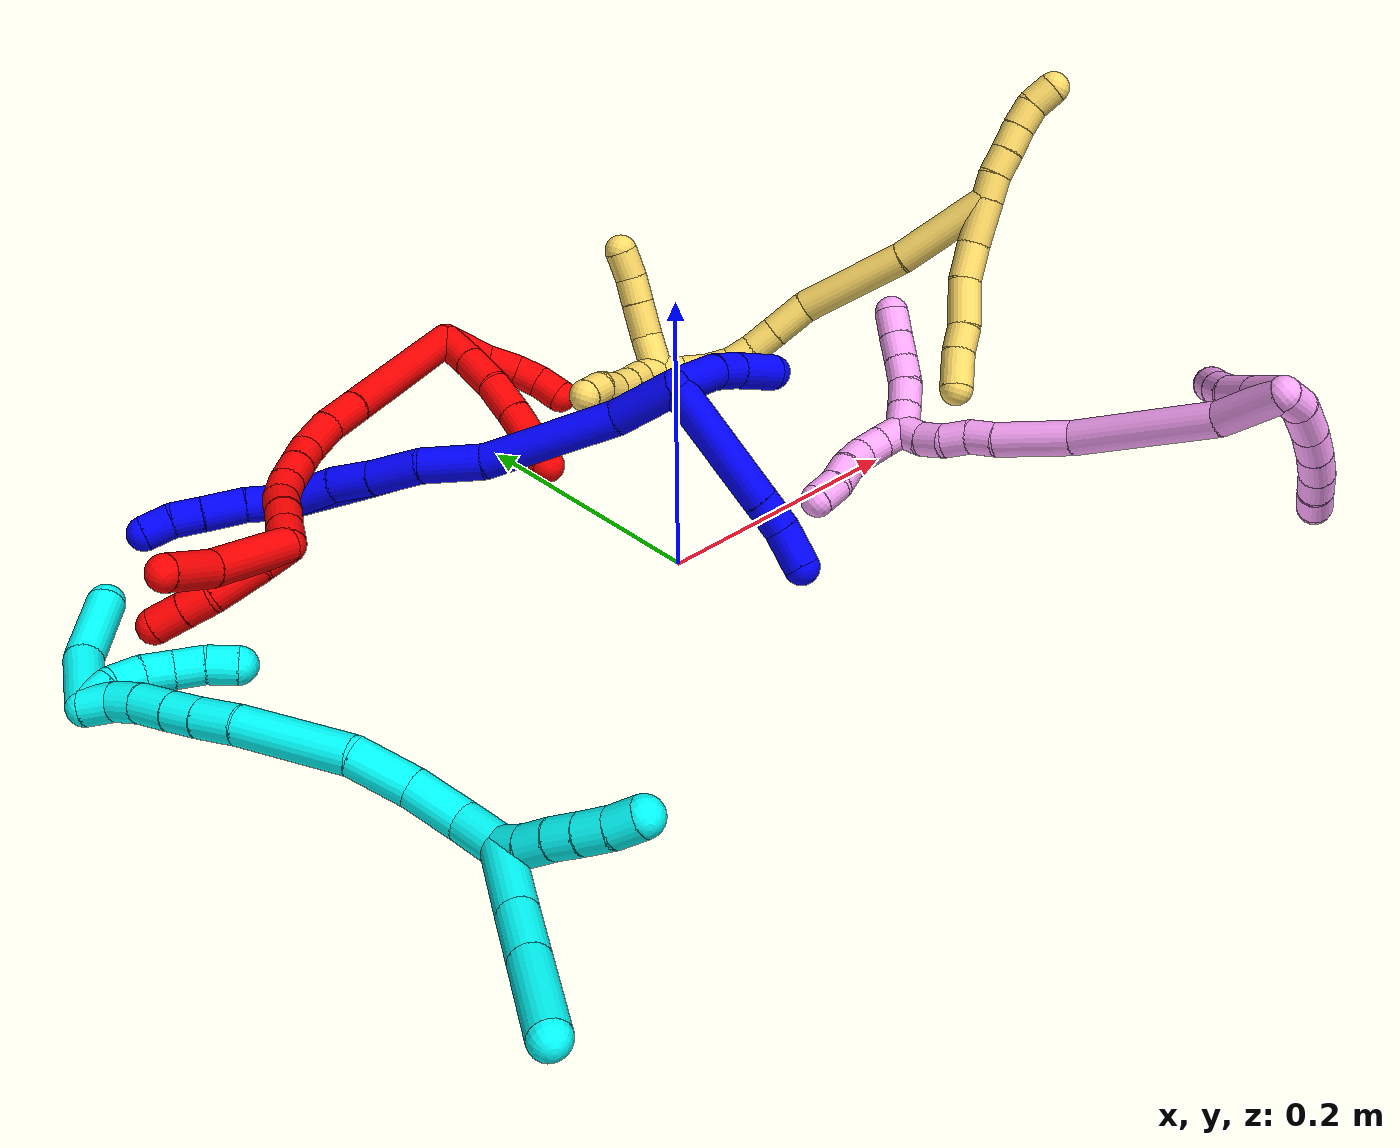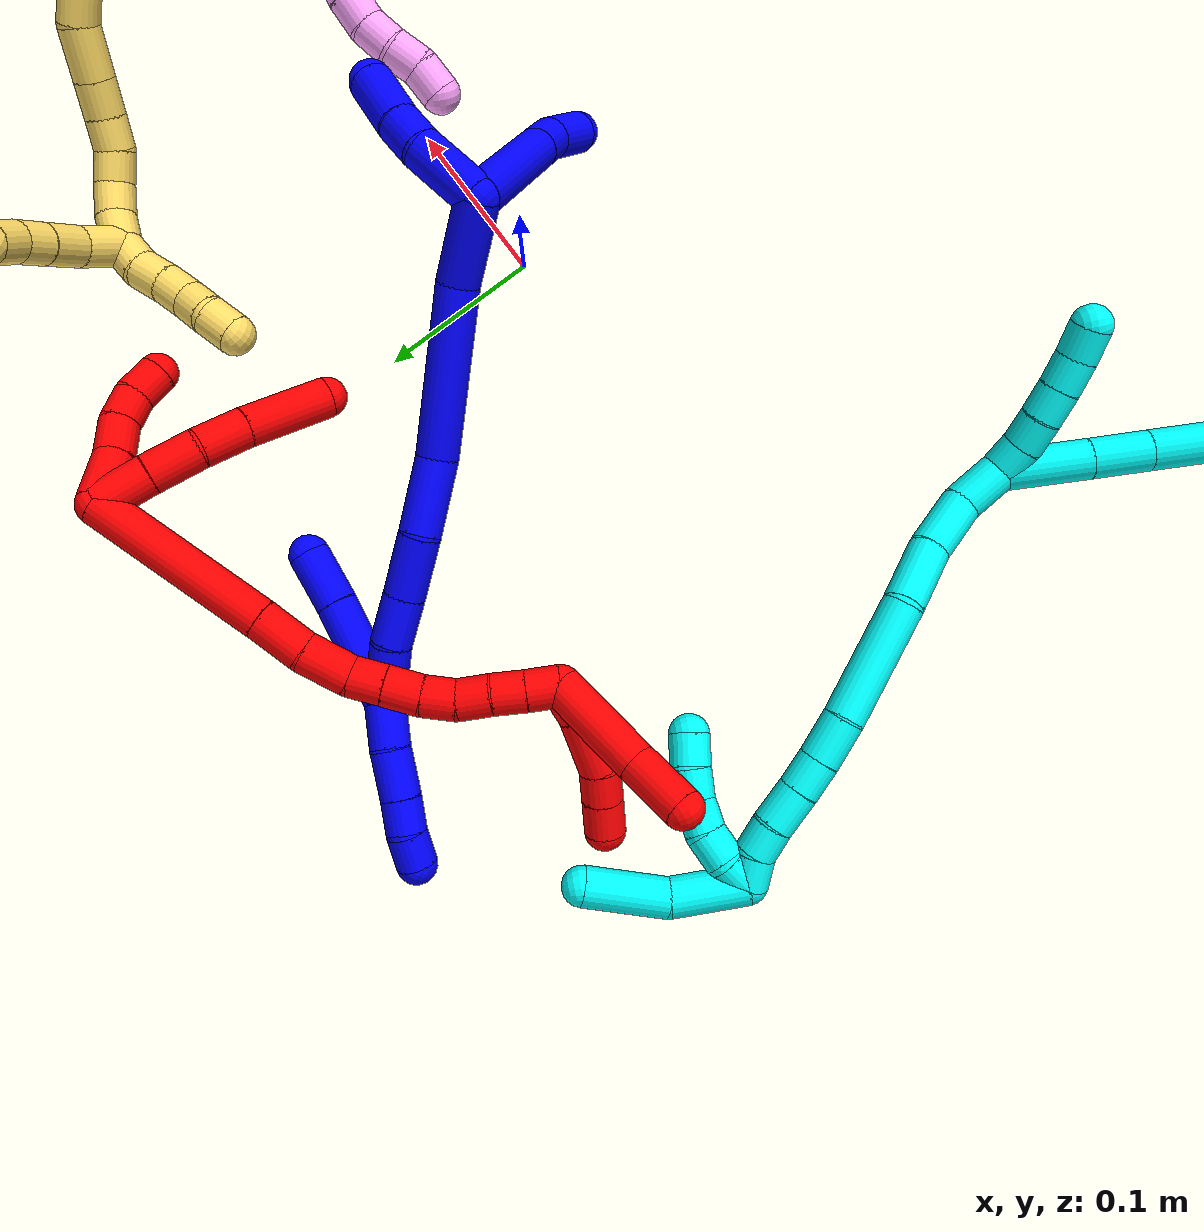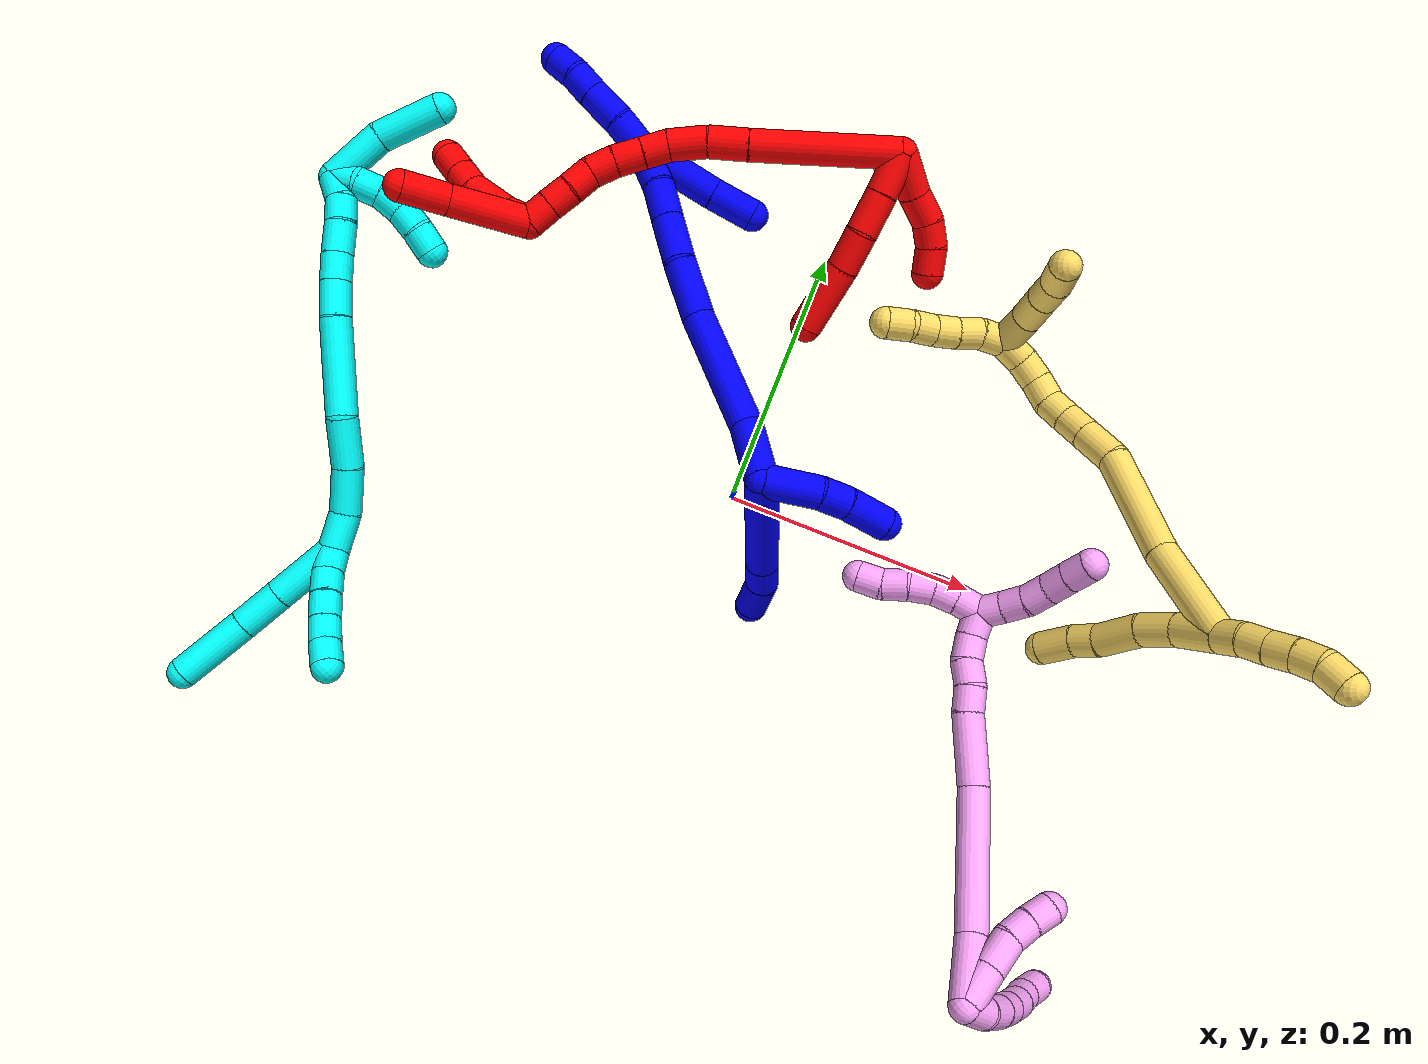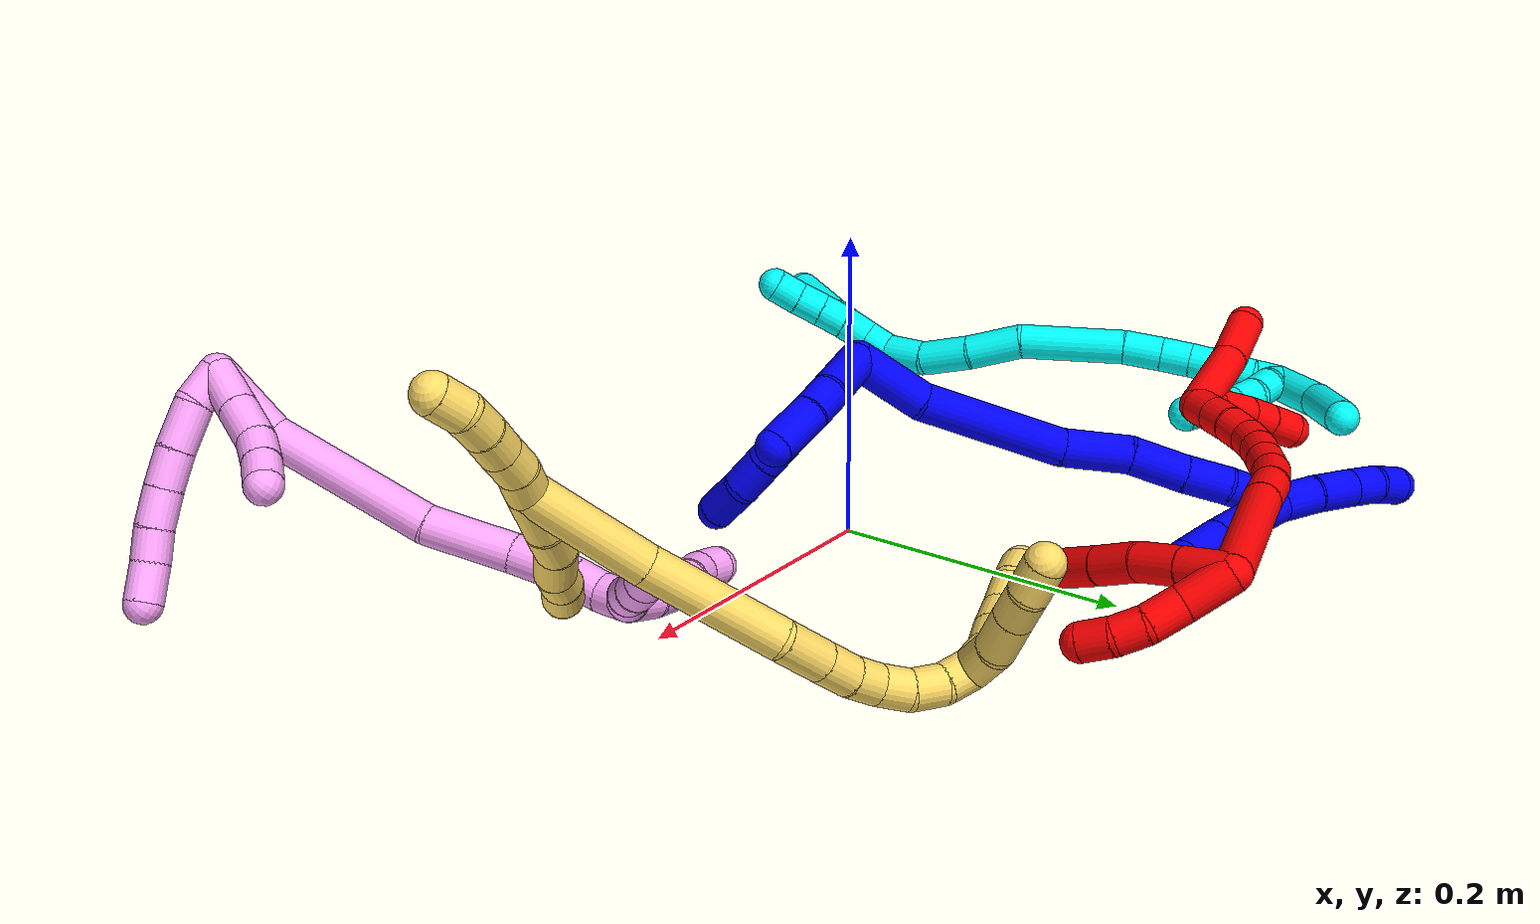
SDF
<sdf version="1.7">
 <world name="default">
  <plugin name="TubeGeneratorPlugin" filename="libtube_generator_plugin.so"/>
  <model name="photoneo_s_sensor">
   <static>1</static>
   <pose>0 0 2 1.57079 1.57079 3.14159</pose>
   <link name="link">
    <inertial><mass>0.1</mass></inertial>
    <sensor name="sensor" type="depth">
     <update_rate>30</update_rate>
     <camera>
      <horizontal_fov>1.22</horizontal_fov>
      <image><width>1920</width><height>1200</height><format>B8G8R8</format></image>
      <clip><near>0.1</near><far>4</far></clip>
      <depth_camera><output>points</output></depth_camera>
     </camera>
     <plugin name="camera_plugin" filename="libgazebo_ros_depth_camera.so">
      <baseline>0.2</baseline>
      <alwaysOn>1</alwaysOn>
      <updateRate>0.0</updateRate>
      <cameraName>camera_ir</cameraName>
      <imageTopicName>/camera/color/image_raw</imageTopicName>
      <cameraInfoTopicName>/camera/color/camera_info</cameraInfoTopicName>
      <depthImageTopicName>/camera/depth/image_raw</depthImageTopicName>
      <depthImageCameraInfoTopicName>/camera/depth/camera_info</depthImageCameraInfoTopicName>
      <pointCloudTopicName>/camera/depth/points</pointCloudTopicName>
      <frameName>fr_optical</frameName>
      <pointCloudCutoff>0.1</pointCloudCutoff>
      <pointCloudCutoffMax>2.0</pointCloudCutoffMax>
      <distortionK1>0</distortionK1>
      <distortionK2>0</distortionK2>
      <distortionK3>0</distortionK3>
      <distortionT1>0</distortionT1>
      <distortionT2>0</distortionT2>
      <CxPrime>0</CxPrime>
      <Cx>0</Cx>
      <Cy>0</Cy>
      <focalLength>0</focalLength>
      <hackBaseline>0</hackBaseline>
     </plugin>
    </sensor>
   </link>
  </model>
  <gravity>0 0 -9.8</gravity>
  <magnetic_field>6e-06 2.3e-05 -4.2e-05</magnetic_field>
  <atmosphere type="adiabatic"/>
  <physics name="default_physics" default="0" type="ode">
   <max_step_size>0.003</max_step_size>
   <real_time_factor>1</real_time_factor>
   <real_time_update_rate>1000</real_time_update_rate>
   <max_contacts>10000</max_contacts>
   <ode>
    <solver>
     <type>quick</type>
     <iters>100</iters>
     <sor>1.3</sor>
     <use_dynamic_moi_rescaling>0</use_dynamic_moi_rescaling>
    </solver>
    <constraints>
     <contact_max_correcting_vel>0</contact_max_correcting_vel>
     <contact_surface_layer>0.001</contact_surface_layer>
     <cfm>0</cfm>
     <erp>0.2</erp>
    </constraints>
   </ode>
  </physics>
  <scene><ambient>0.4 0.4 0.4 1</ambient><background>0.7 0.7 0.7 1</background><shadows>0</shadows></scene>
  <audio><device>default</device></audio>
  <spherical_coordinates>
   <surface_model>EARTH_WGS84</surface_model>
   <latitude_deg>0</latitude_deg>
   <longitude_deg>0</longitude_deg>
   <elevation>0</elevation>
   <heading_deg>0</heading_deg>
  </spherical_coordinates>
  <model name="bin">
   <static>1</static>
   <link name="bottom">
    <collision name="collision-bottom">
     <pose>0 0 -0.01 0 -0 0</pose>
     <geometry><box><size>0.8 0.6 0.02</size></box></geometry>
     <surface>
      <friction><ode><mu>100</mu><mu2>100</mu2></ode></friction>
      <contact><collide_bitmask>65535</collide_bitmask></contact>
     </surface>
    </collision>
   </link>
   <link name="west_wall">
    <collision name="collision-west_wall">
     <pose>-0.41 0 0.1 0 -0 0</pose>
     <geometry><box><size>0.02 0.6 0.2</size></box></geometry>
     <surface>
      <friction><ode><mu>100</mu><mu2>100</mu2></ode></friction>
      <contact><collide_bitmask>65535</collide_bitmask></contact>
     </surface>
    </collision>
   </link>
   <link name="east_wall">
    <collision name="collision-east_wall">
     <pose>0.41 0 0.1 0 -0 0</pose>
     <geometry><box><size>0.02 0.6 0.2</size></box></geometry>
     <surface>
      <friction><ode><mu>100</mu><mu2>100</mu2></ode></friction>
      <contact><collide_bitmask>65535</collide_bitmask></contact>
     </surface>
    </collision>
   </link>
   <link name="south_wall">
    <collision name="collision-south_wall">
     <pose>0 -0.31 0.1 0 -0 0</pose>
     <geometry><box><size>0.8 0.02 0.2</size></box></geometry>
     <surface>
      <friction><ode><mu>100</mu><mu2>100</mu2></ode></friction>
      <contact><collide_bitmask>65535</collide_bitmask></contact>
     </surface>
    </collision>
   </link>
   <link name="north_wall">
    <collision name="collision-north_wall">
     <pose>0 0.31 0.1 0 -0 0</pose>
     <geometry><box><size>0.8 0.02 0.2</size></box></geometry>
     <surface>
      <friction><ode><mu>100</mu><mu2>100</mu2></ode></friction>
      <contact><collide_bitmask>65535</collide_bitmask></contact>
     </surface>
    </collision>
   </link>
  </model>
  <model name="1">
   <static>0</static>
   <link name="1">
    <collision name="collision-cylinder-e_1_2_8">
     <pose>-0.02412 -0.039411 -0.01281 1.88506 -0.527106 -0.711275</pose>
     <geometry><cylinder><radius>0.0125</radius><length>0.095898</length></cylinder></geometry>
     <surface>
      <friction><ode><mu>1.16</mu><mu2>1.16</mu2><slip1>0</slip1><slip2>0</slip2></ode></friction>
      <contact><ode><kp>1e+06</kp><kd>1</kd><max_vel>0</max_vel><min_depth>0.001</min_depth></ode></contact>
     </surface>
    </collision>
    <visual name="visual-cylinder-e_1_2_8">
     <pose>-0.02412 -0.039411 -0.01281 1.88506 -0.527106 -0.711275</pose>
     <geometry><cylinder><radius>0.0125</radius><length>0.095898</length></cylinder></geometry>
     <material><ambient>0 0 1 1</ambient></material>
    </visual>
    <collision name="collision-cylinder-e_2_8_9">
     <pose>-0.054355 -0.089045 -0.028797 1.87207 -0.518979 -0.691976</pose>
     <geometry><cylinder><radius>0.0125</radius><length>0.024657</length></cylinder></geometry>
     <surface>
      <friction><ode><mu>1.16</mu><mu2>1.16</mu2><slip1>0</slip1><slip2>0</slip2></ode></friction>
      <contact><ode><kp>1e+06</kp><kd>1</kd><max_vel>0</max_vel><min_depth>0.001</min_depth></ode></contact>
     </surface>
    </collision>
    <visual name="visual-cylinder-e_2_8_9">
     <pose>-0.054355 -0.089045 -0.028797 1.87207 -0.518979 -0.691976</pose>
     <geometry><cylinder><radius>0.0125</radius><length>0.024657</length></cylinder></geometry>
     <material><ambient>0 0 1 1</ambient></material>
    </visual>
    <collision name="collision-cylinder-e_3_9_6">
     <pose>-0.067671 -0.112101 -0.031497 1.5337 -0.511083 -0.493223</pose>
     <geometry><cylinder><radius>0.0125</radius><length>0.029445</length></cylinder></geometry>
     <surface>
      <friction><ode><mu>1.16</mu><mu2>1.16</mu2><slip1>0</slip1><slip2>0</slip2></ode></friction>
      <contact><ode><kp>1e+06</kp><kd>1</kd><max_vel>0</max_vel><min_depth>0.001</min_depth></ode></contact>
     </surface>
    </collision>
    <visual name="visual-cylinder-e_3_9_6">
     <pose>-0.067671 -0.112101 -0.031497 1.5337 -0.511083 -0.493223</pose>
     <geometry><cylinder><radius>0.0125</radius><length>0.029445</length></cylinder></geometry>
     <material><ambient>0 0 1 1</ambient></material>
    </visual>
    <collision name="collision-cylinder-e_1_2_10">
     <pose>0.000732 -0.001019 -0.021494 3.0942 0.033988 1.24417</pose>
     <geometry><cylinder><radius>0.0125</radius><length>0.043062</length></cylinder></geometry>
     <surface>
      <friction><ode><mu>1.16</mu><mu2>1.16</mu2><slip1>0</slip1><slip2>0</slip2></ode></friction>
      <contact><ode><kp>1e+06</kp><kd>1</kd><max_vel>0</max_vel><min_depth>0.001</min_depth></ode></contact>
     </surface>
    </collision>
    <visual name="visual-cylinder-e_1_2_10">
     <pose>0.000732 -0.001019 -0.021494 3.0942 0.033988 1.24417</pose>
     <geometry><cylinder><radius>0.0125</radius><length>0.043062</length></cylinder></geometry>
     <material><ambient>0 0 1 1</ambient></material>
    </visual>
    <collision name="collision-cylinder-e_2_10_11">
     <pose>0.000727 -0.004545 -0.05379 2.91362 -0.066273 -0.563682</pose>
     <geometry><cylinder><radius>0.0125</radius><length>0.022225</length></cylinder></geometry>
     <surface>
      <friction><ode><mu>1.16</mu><mu2>1.16</mu2><slip1>0</slip1><slip2>0</slip2></ode></friction>
      <contact><ode><kp>1e+06</kp><kd>1</kd><max_vel>0</max_vel><min_depth>0.001</min_depth></ode></contact>
     </surface>
    </collision>
    <visual name="visual-cylinder-e_2_10_11">
     <pose>0.000727 -0.004545 -0.05379 2.91362 -0.066273 -0.563682</pose>
     <geometry><cylinder><radius>0.0125</radius><length>0.022225</length></cylinder></geometry>
     <material><ambient>0 0 1 1</ambient></material>
    </visual>
    <collision name="collision-cylinder-e_3_11_5">
     <pose>-0.001387 -0.01301 -0.080834 2.79 -0.079487 -0.440457</pose>
     <geometry><cylinder><radius>0.0125</radius><length>0.034713</length></cylinder></geometry>
     <surface>
      <friction><ode><mu>1.16</mu><mu2>1.16</mu2><slip1>0</slip1><slip2>0</slip2></ode></friction>
      <contact><ode><kp>1e+06</kp><kd>1</kd><max_vel>0</max_vel><min_depth>0.001</min_depth></ode></contact>
     </surface>
    </collision>
    <visual name="visual-cylinder-e_3_11_5">
     <pose>-0.001387 -0.01301 -0.080834 2.79 -0.079487 -0.440457</pose>
     <geometry><cylinder><radius>0.0125</radius><length>0.034713</length></cylinder></geometry>
     <material><ambient>0 0 1 1</ambient></material>
    </visual>
    <collision name="collision-cylinder-e_1_2_12">
     <pose>-0.0204 0.01297 0.004954 -1.20592 -0.973223 0.698609</pose>
     <geometry><cylinder><radius>0.0125</radius><length>0.049353</length></cylinder></geometry>
     <surface>
      <friction><ode><mu>1.16</mu><mu2>1.16</mu2><slip1>0</slip1><slip2>0</slip2></ode></friction>
      <contact><ode><kp>1e+06</kp><kd>1</kd><max_vel>0</max_vel><min_depth>0.001</min_depth></ode></contact>
     </surface>
    </collision>
    <visual name="visual-cylinder-e_1_2_12">
     <pose>-0.0204 0.01297 0.004954 -1.20592 -0.973223 0.698609</pose>
     <geometry><cylinder><radius>0.0125</radius><length>0.049353</length></cylinder></geometry>
     <material><ambient>0 0 1 1</ambient></material>
    </visual>
    <collision name="collision-cylinder-e_2_12_13">
     <pose>-0.074713 0.055972 0.02976 -0.986725 -0.755555 0.420465</pose>
     <geometry><cylinder><radius>0.0125</radius><length>0.098917</length></cylinder></geometry>
     <surface>
      <friction><ode><mu>1.16</mu><mu2>1.16</mu2><slip1>0</slip1><slip2>0</slip2></ode></friction>
      <contact><ode><kp>1e+06</kp><kd>1</kd><max_vel>0</max_vel><min_depth>0.001</min_depth></ode></contact>
     </surface>
    </collision>
    <visual name="visual-cylinder-e_2_12_13">
     <pose>-0.074713 0.055972 0.02976 -0.986725 -0.755555 0.420465</pose>
     <geometry><cylinder><radius>0.0125</radius><length>0.098917</length></cylinder></geometry>
     <material><ambient>0 0 1 1</ambient></material>
    </visual>
    <collision name="collision-cylinder-e_3_13_14">
     <pose>-0.119788 0.103353 0.058915 -1.07854 -0.515792 0.313117</pose>
     <geometry><cylinder><radius>0.0125</radius><length>0.04526</length></cylinder></geometry>
     <surface>
      <friction><ode><mu>1.16</mu><mu2>1.16</mu2><slip1>0</slip1><slip2>0</slip2></ode></friction>
      <contact><ode><kp>1e+06</kp><kd>1</kd><max_vel>0</max_vel><min_depth>0.001</min_depth></ode></contact>
     </surface>
    </collision>
    <visual name="visual-cylinder-e_3_13_14">
     <pose>-0.119788 0.103353 0.058915 -1.07854 -0.515792 0.313117</pose>
     <geometry><cylinder><radius>0.0125</radius><length>0.04526</length></cylinder></geometry>
     <material><ambient>0 0 1 1</ambient></material>
    </visual>
    <collision name="collision-cylinder-e_4_14_15">
     <pose>-0.143708 0.133702 0.073991 -1.15298 -0.731095 0.487792</pose>
     <geometry><cylinder><radius>0.0125</radius><length>0.038216</length></cylinder></geometry>
     <surface>
      <friction><ode><mu>1.16</mu><mu2>1.16</mu2><slip1>0</slip1><slip2>0</slip2></ode></friction>
      <contact><ode><kp>1e+06</kp><kd>1</kd><max_vel>0</max_vel><min_depth>0.001</min_depth></ode></contact>
     </surface>
    </collision>
    <visual name="visual-cylinder-e_4_14_15">
     <pose>-0.143708 0.133702 0.073991 -1.15298 -0.731095 0.487792</pose>
     <geometry><cylinder><radius>0.0125</radius><length>0.038216</length></cylinder></geometry>
     <material><ambient>0 0 1 1</ambient></material>
    </visual>
    <collision name="collision-cylinder-e_5_15_16">
     <pose>-0.165866 0.157816 0.084558 -1.16345 -0.660376 0.443378</pose>
     <geometry><cylinder><radius>0.0125</radius><length>0.030649</length></cylinder></geometry>
     <surface>
      <friction><ode><mu>1.16</mu><mu2>1.16</mu2><slip1>0</slip1><slip2>0</slip2></ode></friction>
      <contact><ode><kp>1e+06</kp><kd>1</kd><max_vel>0</max_vel><min_depth>0.001</min_depth></ode></contact>
     </surface>
    </collision>
    <visual name="visual-cylinder-e_5_15_16">
     <pose>-0.165866 0.157816 0.084558 -1.16345 -0.660376 0.443378</pose>
     <geometry><cylinder><radius>0.0125</radius><length>0.030649</length></cylinder></geometry>
     <material><ambient>0 0 1 1</ambient></material>
    </visual>
    <collision name="collision-cylinder-e_6_16_1">
     <pose>-0.18854 0.180002 0.096752 -0.981754 -0.783722 0.434777</pose>
     <geometry><cylinder><radius>0.0125</radius><length>0.037606</length></cylinder></geometry>
     <surface>
      <friction><ode><mu>1.16</mu><mu2>1.16</mu2><slip1>0</slip1><slip2>0</slip2></ode></friction>
      <contact><ode><kp>1e+06</kp><kd>1</kd><max_vel>0</max_vel><min_depth>0.001</min_depth></ode></contact>
     </surface>
    </collision>
    <visual name="visual-cylinder-e_6_16_1">
     <pose>-0.18854 0.180002 0.096752 -0.981754 -0.783722 0.434777</pose>
     <geometry><cylinder><radius>0.0125</radius><length>0.037606</length></cylinder></geometry>
     <material><ambient>0 0 1 1</ambient></material>
    </visual>
    <collision name="collision-cylinder-e_1_1_17">
     <pose>-0.205878 0.199904 0.11472 -0.695902 -0.286973 0.104712</pose>
     <geometry><cylinder><radius>0.0125</radius><length>0.028719</length></cylinder></geometry>
     <surface>
      <friction><ode><mu>1.16</mu><mu2>1.16</mu2><slip1>0</slip1><slip2>0</slip2></ode></friction>
      <contact><ode><kp>1e+06</kp><kd>1</kd><max_vel>0</max_vel><min_depth>0.001</min_depth></ode></contact>
     </surface>
    </collision>
    <visual name="visual-cylinder-e_1_1_17">
     <pose>-0.205878 0.199904 0.11472 -0.695902 -0.286973 0.104712</pose>
     <geometry><cylinder><radius>0.0125</radius><length>0.028719</length></cylinder></geometry>
     <material><ambient>0 0 1 1</ambient></material>
    </visual>
    <collision name="collision-cylinder-e_2_17_18">
     <pose>-0.215724 0.216364 0.136603 -0.593409 -0.40077 0.124035</pose>
     <geometry><cylinder><radius>0.0125</radius><length>0.02964</length></cylinder></geometry>
     <surface>
      <friction><ode><mu>1.16</mu><mu2>1.16</mu2><slip1>0</slip1><slip2>0</slip2></ode></friction>
      <contact><ode><kp>1e+06</kp><kd>1</kd><max_vel>0</max_vel><min_depth>0.001</min_depth></ode></contact>
     </surface>
    </collision>
    <visual name="visual-cylinder-e_2_17_18">
     <pose>-0.215724 0.216364 0.136603 -0.593409 -0.40077 0.124035</pose>
     <geometry><cylinder><radius>0.0125</radius><length>0.02964</length></cylinder></geometry>
     <material><ambient>0 0 1 1</ambient></material>
    </visual>
    <collision name="collision-cylinder-e_3_18_19">
     <pose>-0.225688 0.229733 0.155575 -0.64305 -0.411987 0.138976</pose>
     <geometry><cylinder><radius>0.0125</radius><length>0.020888</length></cylinder></geometry>
     <surface>
      <friction><ode><mu>1.16</mu><mu2>1.16</mu2><slip1>0</slip1><slip2>0</slip2></ode></friction>
      <contact><ode><kp>1e+06</kp><kd>1</kd><max_vel>0</max_vel><min_depth>0.001</min_depth></ode></contact>
     </surface>
    </collision>
    <visual name="visual-cylinder-e_3_18_19">
     <pose>-0.225688 0.229733 0.155575 -0.64305 -0.411987 0.138976</pose>
     <geometry><cylinder><radius>0.0125</radius><length>0.020888</length></cylinder></geometry>
     <material><ambient>0 0 1 1</ambient></material>
    </visual>
    <collision name="collision-cylinder-e_4_19_4">
     <pose>-0.235719 0.239314 0.170894 -0.46485 -0.598903 0.145898</pose>
     <geometry><cylinder><radius>0.0125</radius><length>0.020753</length></cylinder></geometry>
     <surface>
      <friction><ode><mu>1.16</mu><mu2>1.16</mu2><slip1>0</slip1><slip2>0</slip2></ode></friction>
      <contact><ode><kp>1e+06</kp><kd>1</kd><max_vel>0</max_vel><min_depth>0.001</min_depth></ode></contact>
     </surface>
    </collision>
    <visual name="visual-cylinder-e_4_19_4">
     <pose>-0.235719 0.239314 0.170894 -0.46485 -0.598903 0.145898</pose>
     <geometry><cylinder><radius>0.0125</radius><length>0.020753</length></cylinder></geometry>
     <material><ambient>0 0 1 1</ambient></material>
    </visual>
    <collision name="collision-cylinder-e_1_1_20">
     <pose>-0.194437 0.180321 0.074359 2.79516 0.228806 1.16217</pose>
     <geometry><cylinder><radius>0.0125</radius><length>0.065041</length></cylinder></geometry>
     <surface>
      <friction><ode><mu>1.16</mu><mu2>1.16</mu2><slip1>0</slip1><slip2>0</slip2></ode></friction>
      <contact><ode><kp>1e+06</kp><kd>1</kd><max_vel>0</max_vel><min_depth>0.001</min_depth></ode></contact>
     </surface>
    </collision>
    <visual name="visual-cylinder-e_1_1_20">
     <pose>-0.194437 0.180321 0.074359 2.79516 0.228806 1.16217</pose>
     <geometry><cylinder><radius>0.0125</radius><length>0.065041</length></cylinder></geometry>
     <material><ambient>0 0 1 1</ambient></material>
    </visual>
    <collision name="collision-cylinder-e_2_20_3">
     <pose>-0.183392 0.164582 0.028221 2.84563 0.211486 1.23748</pose>
     <geometry><cylinder><radius>0.0125</radius><length>0.034959</length></cylinder></geometry>
     <surface>
      <friction><ode><mu>1.16</mu><mu2>1.16</mu2><slip1>0</slip1><slip2>0</slip2></ode></friction>
      <contact><ode><kp>1e+06</kp><kd>1</kd><max_vel>0</max_vel><min_depth>0.001</min_depth></ode></contact>
     </surface>
    </collision>
    <visual name="visual-cylinder-e_2_20_3">
     <pose>-0.183392 0.164582 0.028221 2.84563 0.211486 1.23748</pose>
     <geometry><cylinder><radius>0.0125</radius><length>0.034959</length></cylinder></geometry>
     <material><ambient>0 0 1 1</ambient></material>
    </visual>
    <collision name="collision-sphere-3">
     <pose>-0.179723 0.159598 0.011874 0 -0 0</pose>
     <geometry><sphere><radius>0.0125</radius></sphere></geometry>
     <surface>
      <friction><ode><mu>1.16</mu><mu2>1.16</mu2><slip1>0</slip1><slip2>0</slip2></ode></friction>
      <contact><ode><kp>1e+06</kp><kd>1</kd><max_vel>0</max_vel><min_depth>0.001</min_depth></ode></contact>
     </surface>
    </collision>
    <visual name="visual-sphere-3">
     <pose>-0.179723 0.159598 0.011874 0 -0 0</pose>
     <geometry><sphere><radius>0.0125</radius></sphere></geometry>
     <material><ambient>0 0 1 1</ambient></material>
    </visual>
    <collision name="collision-sphere-20">
     <pose>-0.187061 0.169567 0.044568 0 -0 0</pose>
     <geometry><sphere><radius>0.0125</radius></sphere></geometry>
     <surface>
      <friction><ode><mu>1.16</mu><mu2>1.16</mu2><slip1>0</slip1><slip2>0</slip2></ode></friction>
      <contact><ode><kp>1e+06</kp><kd>1</kd><max_vel>0</max_vel><min_depth>0.001</min_depth></ode></contact>
     </surface>
    </collision>
    <visual name="visual-sphere-20">
     <pose>-0.187061 0.169567 0.044568 0 -0 0</pose>
     <geometry><sphere><radius>0.0125</radius></sphere></geometry>
     <material><ambient>0 0 1 1</ambient></material>
    </visual>
    <collision name="collision-sphere-4">
     <pose>-0.241569 0.243156 0.178555 0 -0 0</pose>
     <geometry><sphere><radius>0.0125</radius></sphere></geometry>
     <surface>
      <friction><ode><mu>1.16</mu><mu2>1.16</mu2><slip1>0</slip1><slip2>0</slip2></ode></friction>
      <contact><ode><kp>1e+06</kp><kd>1</kd><max_vel>0</max_vel><min_depth>0.001</min_depth></ode></contact>
     </surface>
    </collision>
    <visual name="visual-sphere-4">
     <pose>-0.241569 0.243156 0.178555 0 -0 0</pose>
     <geometry><sphere><radius>0.0125</radius></sphere></geometry>
     <material><ambient>0 0 1 1</ambient></material>
    </visual>
    <collision name="collision-sphere-11">
     <pose>-9e-06 -0.007051 -0.064591 0 -0 0</pose>
     <geometry><sphere><radius>0.0125</radius></sphere></geometry>
     <surface>
      <friction><ode><mu>1.16</mu><mu2>1.16</mu2><slip1>0</slip1><slip2>0</slip2></ode></friction>
      <contact><ode><kp>1e+06</kp><kd>1</kd><max_vel>0</max_vel><min_depth>0.001</min_depth></ode></contact>
     </surface>
    </collision>
    <visual name="visual-sphere-11">
     <pose>-9e-06 -0.007051 -0.064591 0 -0 0</pose>
     <geometry><sphere><radius>0.0125</radius></sphere></geometry>
     <material><ambient>0 0 1 1</ambient></material>
    </visual>
    <collision name="collision-sphere-10">
     <pose>0.001463 -0.002039 -0.042989 0 -0 0</pose>
     <geometry><sphere><radius>0.0125</radius></sphere></geometry>
     <surface>
      <friction><ode><mu>1.16</mu><mu2>1.16</mu2><slip1>0</slip1><slip2>0</slip2></ode></friction>
      <contact><ode><kp>1e+06</kp><kd>1</kd><max_vel>0</max_vel><min_depth>0.001</min_depth></ode></contact>
     </surface>
    </collision>
    <visual name="visual-sphere-10">
     <pose>0.001463 -0.002039 -0.042989 0 -0 0</pose>
     <geometry><sphere><radius>0.0125</radius></sphere></geometry>
     <material><ambient>0 0 1 1</ambient></material>
    </visual>
    <collision name="collision-sphere-6">
     <pose>-0.074872 -0.124933 -0.031021 0 -0 0</pose>
     <geometry><sphere><radius>0.0125</radius></sphere></geometry>
     <surface>
      <friction><ode><mu>1.16</mu><mu2>1.16</mu2><slip1>0</slip1><slip2>0</slip2></ode></friction>
      <contact><ode><kp>1e+06</kp><kd>1</kd><max_vel>0</max_vel><min_depth>0.001</min_depth></ode></contact>
     </surface>
    </collision>
    <visual name="visual-sphere-6">
     <pose>-0.074872 -0.124933 -0.031021 0 -0 0</pose>
     <geometry><sphere><radius>0.0125</radius></sphere></geometry>
     <material><ambient>0 0 1 1</ambient></material>
    </visual>
    <collision name="collision-sphere-9">
     <pose>-0.06047 -0.099268 -0.031973 0 -0 0</pose>
     <geometry><sphere><radius>0.0125</radius></sphere></geometry>
     <surface>
      <friction><ode><mu>1.16</mu><mu2>1.16</mu2><slip1>0</slip1><slip2>0</slip2></ode></friction>
      <contact><ode><kp>1e+06</kp><kd>1</kd><max_vel>0</max_vel><min_depth>0.001</min_depth></ode></contact>
     </surface>
    </collision>
    <visual name="visual-sphere-9">
     <pose>-0.06047 -0.099268 -0.031973 0 -0 0</pose>
     <geometry><sphere><radius>0.0125</radius></sphere></geometry>
     <material><ambient>0 0 1 1</ambient></material>
    </visual>
    <collision name="collision-sphere-2">
     <geometry><sphere><radius>0.0125</radius></sphere></geometry>
     <surface>
      <friction><ode><mu>1.16</mu><mu2>1.16</mu2><slip1>0</slip1><slip2>0</slip2></ode></friction>
      <contact><ode><kp>1e+06</kp><kd>1</kd><max_vel>0</max_vel><min_depth>0.001</min_depth></ode></contact>
     </surface>
    </collision>
    <visual name="visual-sphere-2">
     <geometry><sphere><radius>0.0125</radius></sphere></geometry>
     <material><ambient>0 0 1 1</ambient></material>
    </visual>
    <collision name="collision-sphere-19">
     <pose>-0.22987 0.235472 0.163234 0 -0 0</pose>
     <geometry><sphere><radius>0.0125</radius></sphere></geometry>
     <surface>
      <friction><ode><mu>1.16</mu><mu2>1.16</mu2><slip1>0</slip1><slip2>0</slip2></ode></friction>
      <contact><ode><kp>1e+06</kp><kd>1</kd><max_vel>0</max_vel><min_depth>0.001</min_depth></ode></contact>
     </surface>
    </collision>
    <visual name="visual-sphere-19">
     <pose>-0.22987 0.235472 0.163234 0 -0 0</pose>
     <geometry><sphere><radius>0.0125</radius></sphere></geometry>
     <material><ambient>0 0 1 1</ambient></material>
    </visual>
    <collision name="collision-sphere-8">
     <pose>-0.04824 -0.078822 -0.02562 0 -0 0</pose>
     <geometry><sphere><radius>0.0125</radius></sphere></geometry>
     <surface>
      <friction><ode><mu>1.16</mu><mu2>1.16</mu2><slip1>0</slip1><slip2>0</slip2></ode></friction>
      <contact><ode><kp>1e+06</kp><kd>1</kd><max_vel>0</max_vel><min_depth>0.001</min_depth></ode></contact>
     </surface>
    </collision>
    <visual name="visual-sphere-8">
     <pose>-0.04824 -0.078822 -0.02562 0 -0 0</pose>
     <geometry><sphere><radius>0.0125</radius></sphere></geometry>
     <material><ambient>0 0 1 1</ambient></material>
    </visual>
    <collision name="collision-sphere-5">
     <pose>-0.002765 -0.018968 -0.097078 0 -0 0</pose>
     <geometry><sphere><radius>0.0125</radius></sphere></geometry>
     <surface>
      <friction><ode><mu>1.16</mu><mu2>1.16</mu2><slip1>0</slip1><slip2>0</slip2></ode></friction>
      <contact><ode><kp>1e+06</kp><kd>1</kd><max_vel>0</max_vel><min_depth>0.001</min_depth></ode></contact>
     </surface>
    </collision>
    <visual name="visual-sphere-5">
     <pose>-0.002765 -0.018968 -0.097078 0 -0 0</pose>
     <geometry><sphere><radius>0.0125</radius></sphere></geometry>
     <material><ambient>0 0 1 1</ambient></material>
    </visual>
    <collision name="collision-sphere-12">
     <pose>-0.0408 0.02594 0.009909 0 -0 0</pose>
     <geometry><sphere><radius>0.0125</radius></sphere></geometry>
     <surface>
      <friction><ode><mu>1.16</mu><mu2>1.16</mu2><slip1>0</slip1><slip2>0</slip2></ode></friction>
      <contact><ode><kp>1e+06</kp><kd>1</kd><max_vel>0</max_vel><min_depth>0.001</min_depth></ode></contact>
     </surface>
    </collision>
    <visual name="visual-sphere-12">
     <pose>-0.0408 0.02594 0.009909 0 -0 0</pose>
     <geometry><sphere><radius>0.0125</radius></sphere></geometry>
     <material><ambient>0 0 1 1</ambient></material>
    </visual>
    <collision name="collision-sphere-13">
     <pose>-0.108626 0.086004 0.049611 0 -0 0</pose>
     <geometry><sphere><radius>0.0125</radius></sphere></geometry>
     <surface>
      <friction><ode><mu>1.16</mu><mu2>1.16</mu2><slip1>0</slip1><slip2>0</slip2></ode></friction>
      <contact><ode><kp>1e+06</kp><kd>1</kd><max_vel>0</max_vel><min_depth>0.001</min_depth></ode></contact>
     </surface>
    </collision>
    <visual name="visual-sphere-13">
     <pose>-0.108626 0.086004 0.049611 0 -0 0</pose>
     <geometry><sphere><radius>0.0125</radius></sphere></geometry>
     <material><ambient>0 0 1 1</ambient></material>
    </visual>
    <collision name="collision-sphere-14">
     <pose>-0.13095 0.120701 0.068219 0 -0 0</pose>
     <geometry><sphere><radius>0.0125</radius></sphere></geometry>
     <surface>
      <friction><ode><mu>1.16</mu><mu2>1.16</mu2><slip1>0</slip1><slip2>0</slip2></ode></friction>
      <contact><ode><kp>1e+06</kp><kd>1</kd><max_vel>0</max_vel><min_depth>0.001</min_depth></ode></contact>
     </surface>
    </collision>
    <visual name="visual-sphere-14">
     <pose>-0.13095 0.120701 0.068219 0 -0 0</pose>
     <geometry><sphere><radius>0.0125</radius></sphere></geometry>
     <material><ambient>0 0 1 1</ambient></material>
    </visual>
    <collision name="collision-sphere-15">
     <pose>-0.156466 0.146704 0.079763 0 -0 0</pose>
     <geometry><sphere><radius>0.0125</radius></sphere></geometry>
     <surface>
      <friction><ode><mu>1.16</mu><mu2>1.16</mu2><slip1>0</slip1><slip2>0</slip2></ode></friction>
      <contact><ode><kp>1e+06</kp><kd>1</kd><max_vel>0</max_vel><min_depth>0.001</min_depth></ode></contact>
     </surface>
    </collision>
    <visual name="visual-sphere-15">
     <pose>-0.156466 0.146704 0.079763 0 -0 0</pose>
     <geometry><sphere><radius>0.0125</radius></sphere></geometry>
     <material><ambient>0 0 1 1</ambient></material>
    </visual>
    <collision name="collision-sphere-16">
     <pose>-0.175267 0.168928 0.089353 0 -0 0</pose>
     <geometry><sphere><radius>0.0125</radius></sphere></geometry>
     <surface>
      <friction><ode><mu>1.16</mu><mu2>1.16</mu2><slip1>0</slip1><slip2>0</slip2></ode></friction>
      <contact><ode><kp>1e+06</kp><kd>1</kd><max_vel>0</max_vel><min_depth>0.001</min_depth></ode></contact>
     </surface>
    </collision>
    <visual name="visual-sphere-16">
     <pose>-0.175267 0.168928 0.089353 0 -0 0</pose>
     <geometry><sphere><radius>0.0125</radius></sphere></geometry>
     <material><ambient>0 0 1 1</ambient></material>
    </visual>
    <collision name="collision-sphere-1">
     <pose>-0.201813 0.191075 0.104151 0 -0 0</pose>
     <geometry><sphere><radius>0.0125</radius></sphere></geometry>
     <surface>
      <friction><ode><mu>1.16</mu><mu2>1.16</mu2><slip1>0</slip1><slip2>0</slip2></ode></friction>
      <contact><ode><kp>1e+06</kp><kd>1</kd><max_vel>0</max_vel><min_depth>0.001</min_depth></ode></contact>
     </surface>
    </collision>
    <visual name="visual-sphere-1">
     <pose>-0.201813 0.191075 0.104151 0 -0 0</pose>
     <geometry><sphere><radius>0.0125</radius></sphere></geometry>
     <material><ambient>0 0 1 1</ambient></material>
    </visual>
    <collision name="collision-sphere-18">
     <pose>-0.221506 0.223995 0.147916 0 -0 0</pose>
     <geometry><sphere><radius>0.0125</radius></sphere></geometry>
     <surface>
      <friction><ode><mu>1.16</mu><mu2>1.16</mu2><slip1>0</slip1><slip2>0</slip2></ode></friction>
      <contact><ode><kp>1e+06</kp><kd>1</kd><max_vel>0</max_vel><min_depth>0.001</min_depth></ode></contact>
     </surface>
    </collision>
    <visual name="visual-sphere-18">
     <pose>-0.221506 0.223995 0.147916 0 -0 0</pose>
     <geometry><sphere><radius>0.0125</radius></sphere></geometry>
     <material><ambient>0 0 1 1</ambient></material>
    </visual>
    <collision name="collision-sphere-17">
     <pose>-0.209942 0.208734 0.12529 0 -0 0</pose>
     <geometry><sphere><radius>0.0125</radius></sphere></geometry>
     <surface>
      <friction><ode><mu>1.16</mu><mu2>1.16</mu2><slip1>0</slip1><slip2>0</slip2></ode></friction>
      <contact><ode><kp>1e+06</kp><kd>1</kd><max_vel>0</max_vel><min_depth>0.001</min_depth></ode></contact>
     </surface>
    </collision>
    <visual name="visual-sphere-17">
     <pose>-0.209942 0.208734 0.12529 0 -0 0</pose>
     <geometry><sphere><radius>0.0125</radius></sphere></geometry>
     <material><ambient>0 0 1 1</ambient></material>
    </visual>
    <inertial>
     <pose>-0.104135 0.076132 0.03611 0 -0 0</pose>
     <mass>0.75</mass>
     <inertia>
      <ixx>0.000164</ixx>
      <ixy>0</ixy>
      <ixz>0</ixz>
      <iyy>0.000115</iyy>
      <iyz>0</iyz>
      <izz>0.000119</izz>
     </inertia>
    </inertial>
   </link>
   <pose>0.014003 0.016155 0.126826 1.02325 -1.19714 -0.826336</pose>
  </model>
  <model name="2">
   <static>0</static>
   <link name="2">
    <collision name="collision-cylinder-e_1_2_8">
     <pose>0.000444 0.000175 -0.016872 -3.1312 0.026316 -2.38936</pose>
     <geometry><cylinder><radius>0.0125</radius><length>0.033757</length></cylinder></geometry>
     <surface>
      <friction><ode><mu>1.16</mu><mu2>1.16</mu2><slip1>0</slip1><slip2>0</slip2></ode></friction>
      <contact><ode><kp>1e+06</kp><kd>1</kd><max_vel>0</max_vel><min_depth>0.001</min_depth></ode></contact>
     </surface>
    </collision>
    <visual name="visual-cylinder-e_1_2_8">
     <pose>0.000444 0.000175 -0.016872 -3.1312 0.026316 -2.38936</pose>
     <geometry><cylinder><radius>0.0125</radius><length>0.033757</length></cylinder></geometry>
     <material><ambient>1 0 0 1</ambient></material>
    </visual>
    <collision name="collision-cylinder-e_2_8_9">
     <pose>0.000754 0.000999 -0.049736 -3.10111 -0.008399 0.409054</pose>
     <geometry><cylinder><radius>0.0125</radius><length>0.032012</length></cylinder></geometry>
     <surface>
      <friction><ode><mu>1.16</mu><mu2>1.16</mu2><slip1>0</slip1><slip2>0</slip2></ode></friction>
      <contact><ode><kp>1e+06</kp><kd>1</kd><max_vel>0</max_vel><min_depth>0.001</min_depth></ode></contact>
     </surface>
    </collision>
    <visual name="visual-cylinder-e_2_8_9">
     <pose>0.000754 0.000999 -0.049736 -3.10111 -0.008399 0.409054</pose>
     <geometry><cylinder><radius>0.0125</radius><length>0.032012</length></cylinder></geometry>
     <material><ambient>1 0 0 1</ambient></material>
    </visual>
    <collision name="collision-cylinder-e_3_9_10">
     <pose>0.000104 0.005017 -0.080653 -2.9195 -0.033679 0.299794</pose>
     <geometry><cylinder><radius>0.0125</radius><length>0.030619</length></cylinder></geometry>
     <surface>
      <friction><ode><mu>1.16</mu><mu2>1.16</mu2><slip1>0</slip1><slip2>0</slip2></ode></friction>
      <contact><ode><kp>1e+06</kp><kd>1</kd><max_vel>0</max_vel><min_depth>0.001</min_depth></ode></contact>
     </surface>
    </collision>
    <visual name="visual-cylinder-e_3_9_10">
     <pose>0.000104 0.005017 -0.080653 -2.9195 -0.033679 0.299794</pose>
     <geometry><cylinder><radius>0.0125</radius><length>0.030619</length></cylinder></geometry>
     <material><ambient>1 0 0 1</ambient></material>
    </visual>
    <collision name="collision-cylinder-e_4_10_6">
     <pose>-0.003201 0.013985 -0.121644 -2.93006 -0.104241 0.913496</pose>
     <geometry><cylinder><radius>0.0125</radius><length>0.053612</length></cylinder></geometry>
     <surface>
      <friction><ode><mu>1.16</mu><mu2>1.16</mu2><slip1>0</slip1><slip2>0</slip2></ode></friction>
      <contact><ode><kp>1e+06</kp><kd>1</kd><max_vel>0</max_vel><min_depth>0.001</min_depth></ode></contact>
     </surface>
    </collision>
    <visual name="visual-cylinder-e_4_10_6">
     <pose>-0.003201 0.013985 -0.121644 -2.93006 -0.104241 0.913496</pose>
     <geometry><cylinder><radius>0.0125</radius><length>0.053612</length></cylinder></geometry>
     <material><ambient>1 0 0 1</ambient></material>
    </visual>
    <collision name="collision-cylinder-e_1_2_11">
     <pose>0.010848 0.008126 -0.010389 -2.47781 0.68831 -1.60999</pose>
     <geometry><cylinder><radius>0.0125</radius><length>0.034154</length></cylinder></geometry>
     <surface>
      <friction><ode><mu>1.16</mu><mu2>1.16</mu2><slip1>0</slip1><slip2>0</slip2></ode></friction>
      <contact><ode><kp>1e+06</kp><kd>1</kd><max_vel>0</max_vel><min_depth>0.001</min_depth></ode></contact>
     </surface>
    </collision>
    <visual name="visual-cylinder-e_1_2_11">
     <pose>0.010848 0.008126 -0.010389 -2.47781 0.68831 -1.60999</pose>
     <geometry><cylinder><radius>0.0125</radius><length>0.034154</length></cylinder></geometry>
     <material><ambient>1 0 0 1</ambient></material>
    </visual>
    <collision name="collision-cylinder-e_2_11_12">
     <pose>0.030986 0.021192 -0.027236 -2.48862 0.851767 -1.8592</pose>
     <geometry><cylinder><radius>0.0125</radius><length>0.024693</length></cylinder></geometry>
     <surface>
      <friction><ode><mu>1.16</mu><mu2>1.16</mu2><slip1>0</slip1><slip2>0</slip2></ode></friction>
      <contact><ode><kp>1e+06</kp><kd>1</kd><max_vel>0</max_vel><min_depth>0.001</min_depth></ode></contact>
     </surface>
    </collision>
    <visual name="visual-cylinder-e_2_11_12">
     <pose>0.030986 0.021192 -0.027236 -2.48862 0.851767 -1.8592</pose>
     <geometry><cylinder><radius>0.0125</radius><length>0.024693</length></cylinder></geometry>
     <material><ambient>1 0 0 1</ambient></material>
    </visual>
    <collision name="collision-cylinder-e_3_12_13">
     <pose>0.045997 0.02925 -0.041325 -2.75377 0.606815 -2.02113</pose>
     <geometry><cylinder><radius>0.0125</radius><length>0.020065</length></cylinder></geometry>
     <surface>
      <friction><ode><mu>1.16</mu><mu2>1.16</mu2><slip1>0</slip1><slip2>0</slip2></ode></friction>
      <contact><ode><kp>1e+06</kp><kd>1</kd><max_vel>0</max_vel><min_depth>0.001</min_depth></ode></contact>
     </surface>
    </collision>
    <visual name="visual-cylinder-e_3_12_13">
     <pose>0.045997 0.02925 -0.041325 -2.75377 0.606815 -2.02113</pose>
     <geometry><cylinder><radius>0.0125</radius><length>0.020065</length></cylinder></geometry>
     <material><ambient>1 0 0 1</ambient></material>
    </visual>
    <collision name="collision-cylinder-e_4_13_5">
     <pose>0.055138 0.034742 -0.058641 -2.9011 0.330351 -1.88715</pose>
     <geometry><cylinder><radius>0.0125</radius><length>0.021088</length></cylinder></geometry>
     <surface>
      <friction><ode><mu>1.16</mu><mu2>1.16</mu2><slip1>0</slip1><slip2>0</slip2></ode></friction>
      <contact><ode><kp>1e+06</kp><kd>1</kd><max_vel>0</max_vel><min_depth>0.001</min_depth></ode></contact>
     </surface>
    </collision>
    <visual name="visual-cylinder-e_4_13_5">
     <pose>0.055138 0.034742 -0.058641 -2.9011 0.330351 -1.88715</pose>
     <geometry><cylinder><radius>0.0125</radius><length>0.021088</length></cylinder></geometry>
     <material><ambient>1 0 0 1</ambient></material>
    </visual>
    <collision name="collision-cylinder-e_1_2_14">
     <pose>-0.052417 -0.007276 -0.023295 2.83885 -1.13505 -2.67186</pose>
     <geometry><cylinder><radius>0.0125</radius><length>0.11564</length></cylinder></geometry>
     <surface>
      <friction><ode><mu>1.16</mu><mu2>1.16</mu2><slip1>0</slip1><slip2>0</slip2></ode></friction>
      <contact><ode><kp>1e+06</kp><kd>1</kd><max_vel>0</max_vel><min_depth>0.001</min_depth></ode></contact>
     </surface>
    </collision>
    <visual name="visual-cylinder-e_1_2_14">
     <pose>-0.052417 -0.007276 -0.023295 2.83885 -1.13505 -2.67186</pose>
     <geometry><cylinder><radius>0.0125</radius><length>0.11564</length></cylinder></geometry>
     <material><ambient>1 0 0 1</ambient></material>
    </visual>
    <collision name="collision-cylinder-e_2_14_15">
     <pose>-0.119106 -0.015974 -0.052413 2.90218 -1.17322 -2.78353</pose>
     <geometry><cylinder><radius>0.0125</radius><length>0.030959</length></cylinder></geometry>
     <surface>
      <friction><ode><mu>1.16</mu><mu2>1.16</mu2><slip1>0</slip1><slip2>0</slip2></ode></friction>
      <contact><ode><kp>1e+06</kp><kd>1</kd><max_vel>0</max_vel><min_depth>0.001</min_depth></ode></contact>
     </surface>
    </collision>
    <visual name="visual-cylinder-e_2_14_15">
     <pose>-0.119106 -0.015974 -0.052413 2.90218 -1.17322 -2.78353</pose>
     <geometry><cylinder><radius>0.0125</radius><length>0.030959</length></cylinder></geometry>
     <material><ambient>1 0 0 1</ambient></material>
    </visual>
    <collision name="collision-cylinder-e_3_15_16">
     <pose>-0.146161 -0.01807 -0.066109 3.05603 -1.01708 -2.98831</pose>
     <geometry><cylinder><radius>0.0125</radius><length>0.030056</length></cylinder></geometry>
     <surface>
      <friction><ode><mu>1.16</mu><mu2>1.16</mu2><slip1>0</slip1><slip2>0</slip2></ode></friction>
      <contact><ode><kp>1e+06</kp><kd>1</kd><max_vel>0</max_vel><min_depth>0.001</min_depth></ode></contact>
     </surface>
    </collision>
    <visual name="visual-cylinder-e_3_15_16">
     <pose>-0.146161 -0.01807 -0.066109 3.05603 -1.01708 -2.98831</pose>
     <geometry><cylinder><radius>0.0125</radius><length>0.030056</length></cylinder></geometry>
     <material><ambient>1 0 0 1</ambient></material>
    </visual>
    <collision name="collision-cylinder-e_4_16_17">
     <pose>-0.166158 -0.020312 -0.080954 2.92055 -0.790269 -2.62148</pose>
     <geometry><cylinder><radius>0.0125</radius><length>0.02031</length></cylinder></geometry>
     <surface>
      <friction><ode><mu>1.16</mu><mu2>1.16</mu2><slip1>0</slip1><slip2>0</slip2></ode></friction>
      <contact><ode><kp>1e+06</kp><kd>1</kd><max_vel>0</max_vel><min_depth>0.001</min_depth></ode></contact>
     </surface>
    </collision>
    <visual name="visual-cylinder-e_4_16_17">
     <pose>-0.166158 -0.020312 -0.080954 2.92055 -0.790269 -2.62148</pose>
     <geometry><cylinder><radius>0.0125</radius><length>0.02031</length></cylinder></geometry>
     <material><ambient>1 0 0 1</ambient></material>
    </visual>
    <collision name="collision-cylinder-e_5_17_18">
     <pose>-0.18136 -0.023252 -0.095408 2.96005 -0.809701 -2.72299</pose>
     <geometry><cylinder><radius>0.0125</radius><length>0.022061</length></cylinder></geometry>
     <surface>
      <friction><ode><mu>1.16</mu><mu2>1.16</mu2><slip1>0</slip1><slip2>0</slip2></ode></friction>
      <contact><ode><kp>1e+06</kp><kd>1</kd><max_vel>0</max_vel><min_depth>0.001</min_depth></ode></contact>
     </surface>
    </collision>
    <visual name="visual-cylinder-e_5_17_18">
     <pose>-0.18136 -0.023252 -0.095408 2.96005 -0.809701 -2.72299</pose>
     <geometry><cylinder><radius>0.0125</radius><length>0.022061</length></cylinder></geometry>
     <material><ambient>1 0 0 1</ambient></material>
    </visual>
    <collision name="collision-cylinder-e_6_18_19">
     <pose>-0.195664 -0.026201 -0.110942 2.94844 -0.656169 -2.58703</pose>
     <geometry><cylinder><radius>0.0125</radius><length>0.020708</length></cylinder></geometry>
     <surface>
      <friction><ode><mu>1.16</mu><mu2>1.16</mu2><slip1>0</slip1><slip2>0</slip2></ode></friction>
      <contact><ode><kp>1e+06</kp><kd>1</kd><max_vel>0</max_vel><min_depth>0.001</min_depth></ode></contact>
     </surface>
    </collision>
    <visual name="visual-cylinder-e_6_18_19">
     <pose>-0.195664 -0.026201 -0.110942 2.94844 -0.656169 -2.58703</pose>
     <geometry><cylinder><radius>0.0125</radius><length>0.020708</length></cylinder></geometry>
     <material><ambient>1 0 0 1</ambient></material>
    </visual>
    <collision name="collision-cylinder-e_7_19_20">
     <pose>-0.205525 -0.030468 -0.128068 2.85312 -0.358302 -1.78962</pose>
     <geometry><cylinder><radius>0.0125</radius><length>0.020215</length></cylinder></geometry>
     <surface>
      <friction><ode><mu>1.16</mu><mu2>1.16</mu2><slip1>0</slip1><slip2>0</slip2></ode></friction>
      <contact><ode><kp>1e+06</kp><kd>1</kd><max_vel>0</max_vel><min_depth>0.001</min_depth></ode></contact>
     </surface>
    </collision>
    <visual name="visual-cylinder-e_7_19_20">
     <pose>-0.205525 -0.030468 -0.128068 2.85312 -0.358302 -1.78962</pose>
     <geometry><cylinder><radius>0.0125</radius><length>0.020215</length></cylinder></geometry>
     <material><ambient>1 0 0 1</ambient></material>
    </visual>
    <collision name="collision-cylinder-e_8_20_21">
     <pose>-0.213202 -0.034838 -0.146105 2.95658 -0.425533 -2.33039</pose>
     <geometry><cylinder><radius>0.0125</radius><length>0.020022</length></cylinder></geometry>
     <surface>
      <friction><ode><mu>1.16</mu><mu2>1.16</mu2><slip1>0</slip1><slip2>0</slip2></ode></friction>
      <contact><ode><kp>1e+06</kp><kd>1</kd><max_vel>0</max_vel><min_depth>0.001</min_depth></ode></contact>
     </surface>
    </collision>
    <visual name="visual-cylinder-e_8_20_21">
     <pose>-0.213202 -0.034838 -0.146105 2.95658 -0.425533 -2.33039</pose>
     <geometry><cylinder><radius>0.0125</radius><length>0.020022</length></cylinder></geometry>
     <material><ambient>1 0 0 1</ambient></material>
    </visual>
    <collision name="collision-cylinder-e_9_21_1">
     <pose>-0.221043 -0.038165 -0.164224 2.96333 -0.379262 -2.27008</pose>
     <geometry><cylinder><radius>0.0125</radius><length>0.020031</length></cylinder></geometry>
     <surface>
      <friction><ode><mu>1.16</mu><mu2>1.16</mu2><slip1>0</slip1><slip2>0</slip2></ode></friction>
      <contact><ode><kp>1e+06</kp><kd>1</kd><max_vel>0</max_vel><min_depth>0.001</min_depth></ode></contact>
     </surface>
    </collision>
    <visual name="visual-cylinder-e_9_21_1">
     <pose>-0.221043 -0.038165 -0.164224 2.96333 -0.379262 -2.27008</pose>
     <geometry><cylinder><radius>0.0125</radius><length>0.020031</length></cylinder></geometry>
     <material><ambient>1 0 0 1</ambient></material>
    </visual>
    <collision name="collision-cylinder-e_1_1_22">
     <pose>-0.253575 -0.049958 -0.179402 2.10656 -1.18235 -1.73486</pose>
     <geometry><cylinder><radius>0.0125</radius><length>0.062288</length></cylinder></geometry>
     <surface>
      <friction><ode><mu>1.16</mu><mu2>1.16</mu2><slip1>0</slip1><slip2>0</slip2></ode></friction>
      <contact><ode><kp>1e+06</kp><kd>1</kd><max_vel>0</max_vel><min_depth>0.001</min_depth></ode></contact>
     </surface>
    </collision>
    <visual name="visual-cylinder-e_1_1_22">
     <pose>-0.253575 -0.049958 -0.179402 2.10656 -1.18235 -1.73486</pose>
     <geometry><cylinder><radius>0.0125</radius><length>0.062288</length></cylinder></geometry>
     <material><ambient>1 0 0 1</ambient></material>
    </visual>
    <collision name="collision-cylinder-e_2_22_4">
     <pose>-0.298301 -0.069695 -0.188683 1.89829 -1.00348 -1.30697</pose>
     <geometry><cylinder><radius>0.0125</radius><length>0.037712</length></cylinder></geometry>
     <surface>
      <friction><ode><mu>1.16</mu><mu2>1.16</mu2><slip1>0</slip1><slip2>0</slip2></ode></friction>
      <contact><ode><kp>1e+06</kp><kd>1</kd><max_vel>0</max_vel><min_depth>0.001</min_depth></ode></contact>
     </surface>
    </collision>
    <visual name="visual-cylinder-e_2_22_4">
     <pose>-0.298301 -0.069695 -0.188683 1.89829 -1.00348 -1.30697</pose>
     <geometry><cylinder><radius>0.0125</radius><length>0.037712</length></cylinder></geometry>
     <material><ambient>1 0 0 1</ambient></material>
    </visual>
    <collision name="collision-cylinder-e_1_1_23">
     <pose>-0.234906 -0.03768 -0.174001 -1.85378 -1.35523 1.64033</pose>
     <geometry><cylinder><radius>0.0125</radius><length>0.020791</length></cylinder></geometry>
     <surface>
      <friction><ode><mu>1.16</mu><mu2>1.16</mu2><slip1>0</slip1><slip2>0</slip2></ode></friction>
      <contact><ode><kp>1e+06</kp><kd>1</kd><max_vel>0</max_vel><min_depth>0.001</min_depth></ode></contact>
     </surface>
    </collision>
    <visual name="visual-cylinder-e_1_1_23">
     <pose>-0.234906 -0.03768 -0.174001 -1.85378 -1.35523 1.64033</pose>
     <geometry><cylinder><radius>0.0125</radius><length>0.020791</length></cylinder></geometry>
     <material><ambient>1 0 0 1</ambient></material>
    </visual>
    <collision name="collision-cylinder-e_2_23_24">
     <pose>-0.262404 -0.029499 -0.172771 -1.27374 -1.2212 0.955326</pose>
     <geometry><cylinder><radius>0.0125</radius><length>0.03692</length></cylinder></geometry>
     <surface>
      <friction><ode><mu>1.16</mu><mu2>1.16</mu2><slip1>0</slip1><slip2>0</slip2></ode></friction>
      <contact><ode><kp>1e+06</kp><kd>1</kd><max_vel>0</max_vel><min_depth>0.001</min_depth></ode></contact>
     </surface>
    </collision>
    <visual name="visual-cylinder-e_2_23_24">
     <pose>-0.262404 -0.029499 -0.172771 -1.27374 -1.2212 0.955326</pose>
     <geometry><cylinder><radius>0.0125</radius><length>0.03692</length></cylinder></geometry>
     <material><ambient>1 0 0 1</ambient></material>
    </visual>
    <collision name="collision-cylinder-e_3_24_25">
     <pose>-0.288314 -0.019292 -0.167678 -0.908988 -1.01886 0.532903</pose>
     <geometry><cylinder><radius>0.0125</radius><length>0.020121</length></cylinder></geometry>
     <surface>
      <friction><ode><mu>1.16</mu><mu2>1.16</mu2><slip1>0</slip1><slip2>0</slip2></ode></friction>
      <contact><ode><kp>1e+06</kp><kd>1</kd><max_vel>0</max_vel><min_depth>0.001</min_depth></ode></contact>
     </surface>
    </collision>
    <visual name="visual-cylinder-e_3_24_25">
     <pose>-0.288314 -0.019292 -0.167678 -0.908988 -1.01886 0.532903</pose>
     <geometry><cylinder><radius>0.0125</radius><length>0.020121</length></cylinder></geometry>
     <material><ambient>1 0 0 1</ambient></material>
    </visual>
    <collision name="collision-cylinder-e_4_25_3">
     <pose>-0.306255 -0.010412 -0.160872 -0.923785 -1.00799 0.535882</pose>
     <geometry><cylinder><radius>0.0125</radius><length>0.022168</length></cylinder></geometry>
     <surface>
      <friction><ode><mu>1.16</mu><mu2>1.16</mu2><slip1>0</slip1><slip2>0</slip2></ode></friction>
      <contact><ode><kp>1e+06</kp><kd>1</kd><max_vel>0</max_vel><min_depth>0.001</min_depth></ode></contact>
     </surface>
    </collision>
    <visual name="visual-cylinder-e_4_25_3">
     <pose>-0.306255 -0.010412 -0.160872 -0.923785 -1.00799 0.535882</pose>
     <geometry><cylinder><radius>0.0125</radius><length>0.022168</length></cylinder></geometry>
     <material><ambient>1 0 0 1</ambient></material>
    </visual>
    <collision name="collision-sphere-3">
     <pose>-0.31563 -0.005693 -0.157307 0 -0 0</pose>
     <geometry><sphere><radius>0.0125</radius></sphere></geometry>
     <surface>
      <friction><ode><mu>1.16</mu><mu2>1.16</mu2><slip1>0</slip1><slip2>0</slip2></ode></friction>
      <contact><ode><kp>1e+06</kp><kd>1</kd><max_vel>0</max_vel><min_depth>0.001</min_depth></ode></contact>
     </surface>
    </collision>
    <visual name="visual-sphere-3">
     <pose>-0.31563 -0.005693 -0.157307 0 -0 0</pose>
     <geometry><sphere><radius>0.0125</radius></sphere></geometry>
     <material><ambient>1 0 0 1</ambient></material>
    </visual>
    <collision name="collision-sphere-25">
     <pose>-0.296881 -0.01513 -0.164437 0 -0 0</pose>
     <geometry><sphere><radius>0.0125</radius></sphere></geometry>
     <surface>
      <friction><ode><mu>1.16</mu><mu2>1.16</mu2><slip1>0</slip1><slip2>0</slip2></ode></friction>
      <contact><ode><kp>1e+06</kp><kd>1</kd><max_vel>0</max_vel><min_depth>0.001</min_depth></ode></contact>
     </surface>
    </collision>
    <visual name="visual-sphere-25">
     <pose>-0.296881 -0.01513 -0.164437 0 -0 0</pose>
     <geometry><sphere><radius>0.0125</radius></sphere></geometry>
     <material><ambient>1 0 0 1</ambient></material>
    </visual>
    <collision name="collision-sphere-24">
     <pose>-0.279748 -0.023453 -0.17092 0 -0 0</pose>
     <geometry><sphere><radius>0.0125</radius></sphere></geometry>
     <surface>
      <friction><ode><mu>1.16</mu><mu2>1.16</mu2><slip1>0</slip1><slip2>0</slip2></ode></friction>
      <contact><ode><kp>1e+06</kp><kd>1</kd><max_vel>0</max_vel><min_depth>0.001</min_depth></ode></contact>
     </surface>
    </collision>
    <visual name="visual-sphere-24">
     <pose>-0.279748 -0.023453 -0.17092 0 -0 0</pose>
     <geometry><sphere><radius>0.0125</radius></sphere></geometry>
     <material><ambient>1 0 0 1</ambient></material>
    </visual>
    <collision name="collision-sphere-23">
     <pose>-0.245061 -0.035545 -0.174622 0 -0 0</pose>
     <geometry><sphere><radius>0.0125</radius></sphere></geometry>
     <surface>
      <friction><ode><mu>1.16</mu><mu2>1.16</mu2><slip1>0</slip1><slip2>0</slip2></ode></friction>
      <contact><ode><kp>1e+06</kp><kd>1</kd><max_vel>0</max_vel><min_depth>0.001</min_depth></ode></contact>
     </surface>
    </collision>
    <visual name="visual-sphere-23">
     <pose>-0.245061 -0.035545 -0.174622 0 -0 0</pose>
     <geometry><sphere><radius>0.0125</radius></sphere></geometry>
     <material><ambient>1 0 0 1</ambient></material>
    </visual>
    <collision name="collision-sphere-4">
     <pose>-0.314203 -0.079289 -0.191942 0 -0 0</pose>
     <geometry><sphere><radius>0.0125</radius></sphere></geometry>
     <surface>
      <friction><ode><mu>1.16</mu><mu2>1.16</mu2><slip1>0</slip1><slip2>0</slip2></ode></friction>
      <contact><ode><kp>1e+06</kp><kd>1</kd><max_vel>0</max_vel><min_depth>0.001</min_depth></ode></contact>
     </surface>
    </collision>
    <visual name="visual-sphere-4">
     <pose>-0.314203 -0.079289 -0.191942 0 -0 0</pose>
     <geometry><sphere><radius>0.0125</radius></sphere></geometry>
     <material><ambient>1 0 0 1</ambient></material>
    </visual>
    <collision name="collision-sphere-22">
     <pose>-0.282398 -0.060101 -0.185423 0 -0 0</pose>
     <geometry><sphere><radius>0.0125</radius></sphere></geometry>
     <surface>
      <friction><ode><mu>1.16</mu><mu2>1.16</mu2><slip1>0</slip1><slip2>0</slip2></ode></friction>
      <contact><ode><kp>1e+06</kp><kd>1</kd><max_vel>0</max_vel><min_depth>0.001</min_depth></ode></contact>
     </surface>
    </collision>
    <visual name="visual-sphere-22">
     <pose>-0.282398 -0.060101 -0.185423 0 -0 0</pose>
     <geometry><sphere><radius>0.0125</radius></sphere></geometry>
     <material><ambient>1 0 0 1</ambient></material>
    </visual>
    <collision name="collision-sphere-1">
     <pose>-0.224751 -0.039815 -0.17338 0 -0 0</pose>
     <geometry><sphere><radius>0.0125</radius></sphere></geometry>
     <surface>
      <friction><ode><mu>1.16</mu><mu2>1.16</mu2><slip1>0</slip1><slip2>0</slip2></ode></friction>
      <contact><ode><kp>1e+06</kp><kd>1</kd><max_vel>0</max_vel><min_depth>0.001</min_depth></ode></contact>
     </surface>
    </collision>
    <visual name="visual-sphere-1">
     <pose>-0.224751 -0.039815 -0.17338 0 -0 0</pose>
     <geometry><sphere><radius>0.0125</radius></sphere></geometry>
     <material><ambient>1 0 0 1</ambient></material>
    </visual>
    <collision name="collision-sphere-21">
     <pose>-0.217335 -0.036516 -0.155067 0 -0 0</pose>
     <geometry><sphere><radius>0.0125</radius></sphere></geometry>
     <surface>
      <friction><ode><mu>1.16</mu><mu2>1.16</mu2><slip1>0</slip1><slip2>0</slip2></ode></friction>
      <contact><ode><kp>1e+06</kp><kd>1</kd><max_vel>0</max_vel><min_depth>0.001</min_depth></ode></contact>
     </surface>
    </collision>
    <visual name="visual-sphere-21">
     <pose>-0.217335 -0.036516 -0.155067 0 -0 0</pose>
     <geometry><sphere><radius>0.0125</radius></sphere></geometry>
     <material><ambient>1 0 0 1</ambient></material>
    </visual>
    <collision name="collision-sphere-11">
     <pose>0.021696 0.016252 -0.020777 0 -0 0</pose>
     <geometry><sphere><radius>0.0125</radius></sphere></geometry>
     <surface>
      <friction><ode><mu>1.16</mu><mu2>1.16</mu2><slip1>0</slip1><slip2>0</slip2></ode></friction>
      <contact><ode><kp>1e+06</kp><kd>1</kd><max_vel>0</max_vel><min_depth>0.001</min_depth></ode></contact>
     </surface>
    </collision>
    <visual name="visual-sphere-11">
     <pose>0.021696 0.016252 -0.020777 0 -0 0</pose>
     <geometry><sphere><radius>0.0125</radius></sphere></geometry>
     <material><ambient>1 0 0 1</ambient></material>
    </visual>
    <collision name="collision-sphere-6">
     <pose>-0.00599 0.019582 -0.147711 0 -0 0</pose>
     <geometry><sphere><radius>0.0125</radius></sphere></geometry>
     <surface>
      <friction><ode><mu>1.16</mu><mu2>1.16</mu2><slip1>0</slip1><slip2>0</slip2></ode></friction>
      <contact><ode><kp>1e+06</kp><kd>1</kd><max_vel>0</max_vel><min_depth>0.001</min_depth></ode></contact>
     </surface>
    </collision>
    <visual name="visual-sphere-6">
     <pose>-0.00599 0.019582 -0.147711 0 -0 0</pose>
     <geometry><sphere><radius>0.0125</radius></sphere></geometry>
     <material><ambient>1 0 0 1</ambient></material>
    </visual>
    <collision name="collision-sphere-10">
     <pose>-0.000412 0.008387 -0.095578 0 -0 0</pose>
     <geometry><sphere><radius>0.0125</radius></sphere></geometry>
     <surface>
      <friction><ode><mu>1.16</mu><mu2>1.16</mu2><slip1>0</slip1><slip2>0</slip2></ode></friction>
      <contact><ode><kp>1e+06</kp><kd>1</kd><max_vel>0</max_vel><min_depth>0.001</min_depth></ode></contact>
     </surface>
    </collision>
    <visual name="visual-sphere-10">
     <pose>-0.000412 0.008387 -0.095578 0 -0 0</pose>
     <geometry><sphere><radius>0.0125</radius></sphere></geometry>
     <material><ambient>1 0 0 1</ambient></material>
    </visual>
    <collision name="collision-sphere-9">
     <pose>0.000619 0.001646 -0.065728 0 -0 0</pose>
     <geometry><sphere><radius>0.0125</radius></sphere></geometry>
     <surface>
      <friction><ode><mu>1.16</mu><mu2>1.16</mu2><slip1>0</slip1><slip2>0</slip2></ode></friction>
      <contact><ode><kp>1e+06</kp><kd>1</kd><max_vel>0</max_vel><min_depth>0.001</min_depth></ode></contact>
     </surface>
    </collision>
    <visual name="visual-sphere-9">
     <pose>0.000619 0.001646 -0.065728 0 -0 0</pose>
     <geometry><sphere><radius>0.0125</radius></sphere></geometry>
     <material><ambient>1 0 0 1</ambient></material>
    </visual>
    <collision name="collision-sphere-2">
     <geometry><sphere><radius>0.0125</radius></sphere></geometry>
     <surface>
      <friction><ode><mu>1.16</mu><mu2>1.16</mu2><slip1>0</slip1><slip2>0</slip2></ode></friction>
      <contact><ode><kp>1e+06</kp><kd>1</kd><max_vel>0</max_vel><min_depth>0.001</min_depth></ode></contact>
     </surface>
    </collision>
    <visual name="visual-sphere-2">
     <geometry><sphere><radius>0.0125</radius></sphere></geometry>
     <material><ambient>1 0 0 1</ambient></material>
    </visual>
    <collision name="collision-sphere-19">
     <pose>-0.201981 -0.027775 -0.118993 0 -0 0</pose>
     <geometry><sphere><radius>0.0125</radius></sphere></geometry>
     <surface>
      <friction><ode><mu>1.16</mu><mu2>1.16</mu2><slip1>0</slip1><slip2>0</slip2></ode></friction>
      <contact><ode><kp>1e+06</kp><kd>1</kd><max_vel>0</max_vel><min_depth>0.001</min_depth></ode></contact>
     </surface>
    </collision>
    <visual name="visual-sphere-19">
     <pose>-0.201981 -0.027775 -0.118993 0 -0 0</pose>
     <geometry><sphere><radius>0.0125</radius></sphere></geometry>
     <material><ambient>1 0 0 1</ambient></material>
    </visual>
    <collision name="collision-sphere-8">
     <pose>0.000888 0.000351 -0.033743 0 -0 0</pose>
     <geometry><sphere><radius>0.0125</radius></sphere></geometry>
     <surface>
      <friction><ode><mu>1.16</mu><mu2>1.16</mu2><slip1>0</slip1><slip2>0</slip2></ode></friction>
      <contact><ode><kp>1e+06</kp><kd>1</kd><max_vel>0</max_vel><min_depth>0.001</min_depth></ode></contact>
     </surface>
    </collision>
    <visual name="visual-sphere-8">
     <pose>0.000888 0.000351 -0.033743 0 -0 0</pose>
     <geometry><sphere><radius>0.0125</radius></sphere></geometry>
     <material><ambient>1 0 0 1</ambient></material>
    </visual>
    <collision name="collision-sphere-12">
     <pose>0.040276 0.026133 -0.033695 0 -0 0</pose>
     <geometry><sphere><radius>0.0125</radius></sphere></geometry>
     <surface>
      <friction><ode><mu>1.16</mu><mu2>1.16</mu2><slip1>0</slip1><slip2>0</slip2></ode></friction>
      <contact><ode><kp>1e+06</kp><kd>1</kd><max_vel>0</max_vel><min_depth>0.001</min_depth></ode></contact>
     </surface>
    </collision>
    <visual name="visual-sphere-12">
     <pose>0.040276 0.026133 -0.033695 0 -0 0</pose>
     <geometry><sphere><radius>0.0125</radius></sphere></geometry>
     <material><ambient>1 0 0 1</ambient></material>
    </visual>
    <collision name="collision-sphere-13">
     <pose>0.051718 0.032366 -0.048954 0 -0 0</pose>
     <geometry><sphere><radius>0.0125</radius></sphere></geometry>
     <surface>
      <friction><ode><mu>1.16</mu><mu2>1.16</mu2><slip1>0</slip1><slip2>0</slip2></ode></friction>
      <contact><ode><kp>1e+06</kp><kd>1</kd><max_vel>0</max_vel><min_depth>0.001</min_depth></ode></contact>
     </surface>
    </collision>
    <visual name="visual-sphere-13">
     <pose>0.051718 0.032366 -0.048954 0 -0 0</pose>
     <geometry><sphere><radius>0.0125</radius></sphere></geometry>
     <material><ambient>1 0 0 1</ambient></material>
    </visual>
    <collision name="collision-sphere-5">
     <pose>0.058559 0.037118 -0.068327 0 -0 0</pose>
     <geometry><sphere><radius>0.0125</radius></sphere></geometry>
     <surface>
      <friction><ode><mu>1.16</mu><mu2>1.16</mu2><slip1>0</slip1><slip2>0</slip2></ode></friction>
      <contact><ode><kp>1e+06</kp><kd>1</kd><max_vel>0</max_vel><min_depth>0.001</min_depth></ode></contact>
     </surface>
    </collision>
    <visual name="visual-sphere-5">
     <pose>0.058559 0.037118 -0.068327 0 -0 0</pose>
     <geometry><sphere><radius>0.0125</radius></sphere></geometry>
     <material><ambient>1 0 0 1</ambient></material>
    </visual>
    <collision name="collision-sphere-14">
     <pose>-0.104834 -0.014552 -0.04659 0 -0 0</pose>
     <geometry><sphere><radius>0.0125</radius></sphere></geometry>
     <surface>
      <friction><ode><mu>1.16</mu><mu2>1.16</mu2><slip1>0</slip1><slip2>0</slip2></ode></friction>
      <contact><ode><kp>1e+06</kp><kd>1</kd><max_vel>0</max_vel><min_depth>0.001</min_depth></ode></contact>
     </surface>
    </collision>
    <visual name="visual-sphere-14">
     <pose>-0.104834 -0.014552 -0.04659 0 -0 0</pose>
     <geometry><sphere><radius>0.0125</radius></sphere></geometry>
     <material><ambient>1 0 0 1</ambient></material>
    </visual>
    <collision name="collision-sphere-15">
     <pose>-0.133378 -0.017395 -0.058235 0 -0 0</pose>
     <geometry><sphere><radius>0.0125</radius></sphere></geometry>
     <surface>
      <friction><ode><mu>1.16</mu><mu2>1.16</mu2><slip1>0</slip1><slip2>0</slip2></ode></friction>
      <contact><ode><kp>1e+06</kp><kd>1</kd><max_vel>0</max_vel><min_depth>0.001</min_depth></ode></contact>
     </surface>
    </collision>
    <visual name="visual-sphere-15">
     <pose>-0.133378 -0.017395 -0.058235 0 -0 0</pose>
     <geometry><sphere><radius>0.0125</radius></sphere></geometry>
     <material><ambient>1 0 0 1</ambient></material>
    </visual>
    <collision name="collision-sphere-16">
     <pose>-0.158943 -0.018745 -0.073982 0 -0 0</pose>
     <geometry><sphere><radius>0.0125</radius></sphere></geometry>
     <surface>
      <friction><ode><mu>1.16</mu><mu2>1.16</mu2><slip1>0</slip1><slip2>0</slip2></ode></friction>
      <contact><ode><kp>1e+06</kp><kd>1</kd><max_vel>0</max_vel><min_depth>0.001</min_depth></ode></contact>
     </surface>
    </collision>
    <visual name="visual-sphere-16">
     <pose>-0.158943 -0.018745 -0.073982 0 -0 0</pose>
     <geometry><sphere><radius>0.0125</radius></sphere></geometry>
     <material><ambient>1 0 0 1</ambient></material>
    </visual>
    <collision name="collision-sphere-17">
     <pose>-0.173374 -0.021879 -0.087926 0 -0 0</pose>
     <geometry><sphere><radius>0.0125</radius></sphere></geometry>
     <surface>
      <friction><ode><mu>1.16</mu><mu2>1.16</mu2><slip1>0</slip1><slip2>0</slip2></ode></friction>
      <contact><ode><kp>1e+06</kp><kd>1</kd><max_vel>0</max_vel><min_depth>0.001</min_depth></ode></contact>
     </surface>
    </collision>
    <visual name="visual-sphere-17">
     <pose>-0.173374 -0.021879 -0.087926 0 -0 0</pose>
     <geometry><sphere><radius>0.0125</radius></sphere></geometry>
     <material><ambient>1 0 0 1</ambient></material>
    </visual>
    <collision name="collision-sphere-18">
     <pose>-0.189347 -0.024626 -0.102891 0 -0 0</pose>
     <geometry><sphere><radius>0.0125</radius></sphere></geometry>
     <surface>
      <friction><ode><mu>1.16</mu><mu2>1.16</mu2><slip1>0</slip1><slip2>0</slip2></ode></friction>
      <contact><ode><kp>1e+06</kp><kd>1</kd><max_vel>0</max_vel><min_depth>0.001</min_depth></ode></contact>
     </surface>
    </collision>
    <visual name="visual-sphere-18">
     <pose>-0.189347 -0.024626 -0.102891 0 -0 0</pose>
     <geometry><sphere><radius>0.0125</radius></sphere></geometry>
     <material><ambient>1 0 0 1</ambient></material>
    </visual>
    <collision name="collision-sphere-20">
     <pose>-0.20907 -0.033161 -0.137142 0 -0 0</pose>
     <geometry><sphere><radius>0.0125</radius></sphere></geometry>
     <surface>
      <friction><ode><mu>1.16</mu><mu2>1.16</mu2><slip1>0</slip1><slip2>0</slip2></ode></friction>
      <contact><ode><kp>1e+06</kp><kd>1</kd><max_vel>0</max_vel><min_depth>0.001</min_depth></ode></contact>
     </surface>
    </collision>
    <visual name="visual-sphere-20">
     <pose>-0.20907 -0.033161 -0.137142 0 -0 0</pose>
     <geometry><sphere><radius>0.0125</radius></sphere></geometry>
     <material><ambient>1 0 0 1</ambient></material>
    </visual>
    <inertial>
     <pose>-0.119379 -0.014127 -0.094168 0 -0 0</pose>
     <mass>0.75</mass>
     <inertia>
      <ixx>-0.000109</ixx>
      <ixy>0</ixy>
      <ixz>0</ixz>
      <iyy>0.000134</iyy>
      <iyz>0</iyz>
      <izz>0.00015</izz>
     </inertia>
    </inertial>
   </link>
   <pose>0.023015 0.28795 0.05446 -1.41811 -0.07679 -0.111023</pose>
  </model>
  <model name="3">
   <static>0</static>
   <link name="3">
    <collision name="collision-cylinder-e_1_2_8">
     <pose>-0.000572 0.00166 0.027177 -0.060996 -0.02101 0.000641</pose>
     <geometry><cylinder><radius>0.0125</radius><length>0.054467</length></cylinder></geometry>
     <surface>
      <friction><ode><mu>1.16</mu><mu2>1.16</mu2><slip1>0</slip1><slip2>0</slip2></ode></friction>
      <contact><ode><kp>1e+06</kp><kd>1</kd><max_vel>0</max_vel><min_depth>0.001</min_depth></ode></contact>
     </surface>
    </collision>
    <visual name="visual-cylinder-e_1_2_8">
     <pose>-0.000572 0.00166 0.027177 -0.060996 -0.02101 0.000641</pose>
     <geometry><cylinder><radius>0.0125</radius><length>0.054467</length></cylinder></geometry>
     <material><ambient>0.003922 1 0.996078 1</ambient></material>
    </visual>
    <collision name="collision-cylinder-e_2_8_9">
     <pose>-0.001109 0.004204 0.072543 -0.048595 0.001931 -4.7e-05</pose>
     <geometry><cylinder><radius>0.0125</radius><length>0.036422</length></cylinder></geometry>
     <surface>
      <friction><ode><mu>1.16</mu><mu2>1.16</mu2><slip1>0</slip1><slip2>0</slip2></ode></friction>
      <contact><ode><kp>1e+06</kp><kd>1</kd><max_vel>0</max_vel><min_depth>0.001</min_depth></ode></contact>
     </surface>
    </collision>
    <visual name="visual-cylinder-e_2_8_9">
     <pose>-0.001109 0.004204 0.072543 -0.048595 0.001931 -4.7e-05</pose>
     <geometry><cylinder><radius>0.0125</radius><length>0.036422</length></cylinder></geometry>
     <material><ambient>0.003922 1 0.996078 1</ambient></material>
    </visual>
    <collision name="collision-cylinder-e_3_9_6">
     <pose>0.0005 0.006293 0.120221 -0.040812 0.053266 -0.001087</pose>
     <geometry><cylinder><radius>0.0125</radius><length>0.059111</length></cylinder></geometry>
     <surface>
      <friction><ode><mu>1.16</mu><mu2>1.16</mu2><slip1>0</slip1><slip2>0</slip2></ode></friction>
      <contact><ode><kp>1e+06</kp><kd>1</kd><max_vel>0</max_vel><min_depth>0.001</min_depth></ode></contact>
     </surface>
    </collision>
    <visual name="visual-cylinder-e_3_9_6">
     <pose>0.0005 0.006293 0.120221 -0.040812 0.053266 -0.001087</pose>
     <geometry><cylinder><radius>0.0125</radius><length>0.059111</length></cylinder></geometry>
     <material><ambient>0.003922 1 0.996078 1</ambient></material>
    </visual>
    <collision name="collision-cylinder-e_1_2_10">
     <pose>0.002487 -0.006821 0.006877 0.781312 0.251306 0.103948</pose>
     <geometry><cylinder><radius>0.0125</radius><length>0.02</length></cylinder></geometry>
     <surface>
      <friction><ode><mu>1.16</mu><mu2>1.16</mu2><slip1>0</slip1><slip2>0</slip2></ode></friction>
      <contact><ode><kp>1e+06</kp><kd>1</kd><max_vel>0</max_vel><min_depth>0.001</min_depth></ode></contact>
     </surface>
    </collision>
    <visual name="visual-cylinder-e_1_2_10">
     <pose>0.002487 -0.006821 0.006877 0.781312 0.251306 0.103948</pose>
     <geometry><cylinder><radius>0.0125</radius><length>0.02</length></cylinder></geometry>
     <material><ambient>0.003922 1 0.996078 1</ambient></material>
    </visual>
    <collision name="collision-cylinder-e_2_10_11">
     <pose>0.007908 -0.021478 0.01923 0.960831 0.297831 0.156052</pose>
     <geometry><cylinder><radius>0.0125</radius><length>0.02</length></cylinder></geometry>
     <surface>
      <friction><ode><mu>1.16</mu><mu2>1.16</mu2><slip1>0</slip1><slip2>0</slip2></ode></friction>
      <contact><ode><kp>1e+06</kp><kd>1</kd><max_vel>0</max_vel><min_depth>0.001</min_depth></ode></contact>
     </surface>
    </collision>
    <visual name="visual-cylinder-e_2_10_11">
     <pose>0.007908 -0.021478 0.01923 0.960831 0.297831 0.156052</pose>
     <geometry><cylinder><radius>0.0125</radius><length>0.02</length></cylinder></geometry>
     <material><ambient>0.003922 1 0.996078 1</ambient></material>
    </visual>
    <collision name="collision-cylinder-e_3_11_12">
     <pose>0.012913 -0.037335 0.030307 0.9613 0.208593 0.109056</pose>
     <geometry><cylinder><radius>0.0125</radius><length>0.02</length></cylinder></geometry>
     <surface>
      <friction><ode><mu>1.16</mu><mu2>1.16</mu2><slip1>0</slip1><slip2>0</slip2></ode></friction>
      <contact><ode><kp>1e+06</kp><kd>1</kd><max_vel>0</max_vel><min_depth>0.001</min_depth></ode></contact>
     </surface>
    </collision>
    <visual name="visual-cylinder-e_3_11_12">
     <pose>0.012913 -0.037335 0.030307 0.9613 0.208593 0.109056</pose>
     <geometry><cylinder><radius>0.0125</radius><length>0.02</length></cylinder></geometry>
     <material><ambient>0.003922 1 0.996078 1</ambient></material>
    </visual>
    <collision name="collision-cylinder-e_4_12_13">
     <pose>0.016912 -0.05369 0.041088 1.0145 0.194045 0.108076</pose>
     <geometry><cylinder><radius>0.0125</radius><length>0.02</length></cylinder></geometry>
     <surface>
      <friction><ode><mu>1.16</mu><mu2>1.16</mu2><slip1>0</slip1><slip2>0</slip2></ode></friction>
      <contact><ode><kp>1e+06</kp><kd>1</kd><max_vel>0</max_vel><min_depth>0.001</min_depth></ode></contact>
     </surface>
    </collision>
    <visual name="visual-cylinder-e_4_12_13">
     <pose>0.016912 -0.05369 0.041088 1.0145 0.194045 0.108076</pose>
     <geometry><cylinder><radius>0.0125</radius><length>0.02</length></cylinder></geometry>
     <material><ambient>0.003922 1 0.996078 1</ambient></material>
    </visual>
    <collision name="collision-cylinder-e_5_13_5">
     <pose>0.021522 -0.070697 0.05046 1.12081 0.27149 0.170999</pose>
     <geometry><cylinder><radius>0.0125</radius><length>0.02</length></cylinder></geometry>
     <surface>
      <friction><ode><mu>1.16</mu><mu2>1.16</mu2><slip1>0</slip1><slip2>0</slip2></ode></friction>
      <contact><ode><kp>1e+06</kp><kd>1</kd><max_vel>0</max_vel><min_depth>0.001</min_depth></ode></contact>
     </surface>
    </collision>
    <visual name="visual-cylinder-e_5_13_5">
     <pose>0.021522 -0.070697 0.05046 1.12081 0.27149 0.170999</pose>
     <geometry><cylinder><radius>0.0125</radius><length>0.02</length></cylinder></geometry>
     <material><ambient>0.003922 1 0.996078 1</ambient></material>
    </visual>
    <collision name="collision-cylinder-e_1_2_14">
     <pose>0.002861 0.007283 -0.013592 -2.6497 0.183443 -0.702441</pose>
     <geometry><cylinder><radius>0.0125</radius><length>0.031366</length></cylinder></geometry>
     <surface>
      <friction><ode><mu>1.16</mu><mu2>1.16</mu2><slip1>0</slip1><slip2>0</slip2></ode></friction>
      <contact><ode><kp>1e+06</kp><kd>1</kd><max_vel>0</max_vel><min_depth>0.001</min_depth></ode></contact>
     </surface>
    </collision>
    <visual name="visual-cylinder-e_1_2_14">
     <pose>0.002861 0.007283 -0.013592 -2.6497 0.183443 -0.702441</pose>
     <geometry><cylinder><radius>0.0125</radius><length>0.031366</length></cylinder></geometry>
     <material><ambient>0.003922 1 0.996078 1</ambient></material>
    </visual>
    <collision name="collision-cylinder-e_2_14_15">
     <pose>0.014048 0.024333 -0.040356 -2.50355 0.469803 -1.25401</pose>
     <geometry><cylinder><radius>0.0125</radius><length>0.036783</length></cylinder></geometry>
     <surface>
      <friction><ode><mu>1.16</mu><mu2>1.16</mu2><slip1>0</slip1><slip2>0</slip2></ode></friction>
      <contact><ode><kp>1e+06</kp><kd>1</kd><max_vel>0</max_vel><min_depth>0.001</min_depth></ode></contact>
     </surface>
    </collision>
    <visual name="visual-cylinder-e_2_14_15">
     <pose>0.014048 0.024333 -0.040356 -2.50355 0.469803 -1.25401</pose>
     <geometry><cylinder><radius>0.0125</radius><length>0.036783</length></cylinder></geometry>
     <material><ambient>0.003922 1 0.996078 1</ambient></material>
    </visual>
    <collision name="collision-cylinder-e_3_15_16">
     <pose>0.032633 0.046415 -0.06556 -2.34456 0.537413 -1.15837</pose>
     <geometry><cylinder><radius>0.0125</radius><length>0.040081</length></cylinder></geometry>
     <surface>
      <friction><ode><mu>1.16</mu><mu2>1.16</mu2><slip1>0</slip1><slip2>0</slip2></ode></friction>
      <contact><ode><kp>1e+06</kp><kd>1</kd><max_vel>0</max_vel><min_depth>0.001</min_depth></ode></contact>
     </surface>
    </collision>
    <visual name="visual-cylinder-e_3_15_16">
     <pose>0.032633 0.046415 -0.06556 -2.34456 0.537413 -1.15837</pose>
     <geometry><cylinder><radius>0.0125</radius><length>0.040081</length></cylinder></geometry>
     <material><ambient>0.003922 1 0.996078 1</ambient></material>
    </visual>
    <collision name="collision-cylinder-e_4_16_17">
     <pose>0.052526 0.086733 -0.101352 -2.27443 0.256537 -0.543403</pose>
     <geometry><cylinder><radius>0.0125</radius><length>0.075937</length></cylinder></geometry>
     <surface>
      <friction><ode><mu>1.16</mu><mu2>1.16</mu2><slip1>0</slip1><slip2>0</slip2></ode></friction>
      <contact><ode><kp>1e+06</kp><kd>1</kd><max_vel>0</max_vel><min_depth>0.001</min_depth></ode></contact>
     </surface>
    </collision>
    <visual name="visual-cylinder-e_4_16_17">
     <pose>0.052526 0.086733 -0.101352 -2.27443 0.256537 -0.543403</pose>
     <geometry><cylinder><radius>0.0125</radius><length>0.075937</length></cylinder></geometry>
     <material><ambient>0.003922 1 0.996078 1</ambient></material>
    </visual>
    <collision name="collision-cylinder-e_5_17_18">
     <pose>0.063947 0.125219 -0.134287 -2.28964 0.127625 -0.279801</pose>
     <geometry><cylinder><radius>0.0125</radius><length>0.028088</length></cylinder></geometry>
     <surface>
      <friction><ode><mu>1.16</mu><mu2>1.16</mu2><slip1>0</slip1><slip2>0</slip2></ode></friction>
      <contact><ode><kp>1e+06</kp><kd>1</kd><max_vel>0</max_vel><min_depth>0.001</min_depth></ode></contact>
     </surface>
    </collision>
    <visual name="visual-cylinder-e_5_17_18">
     <pose>0.063947 0.125219 -0.134287 -2.28964 0.127625 -0.279801</pose>
     <geometry><cylinder><radius>0.0125</radius><length>0.028088</length></cylinder></geometry>
     <material><ambient>0.003922 1 0.996078 1</ambient></material>
    </visual>
    <collision name="collision-cylinder-e_6_18_19">
     <pose>0.067028 0.143416 -0.150966 -2.34254 0.119551 -0.281603</pose>
     <geometry><cylinder><radius>0.0125</radius><length>0.021682</length></cylinder></geometry>
     <surface>
      <friction><ode><mu>1.16</mu><mu2>1.16</mu2><slip1>0</slip1><slip2>0</slip2></ode></friction>
      <contact><ode><kp>1e+06</kp><kd>1</kd><max_vel>0</max_vel><min_depth>0.001</min_depth></ode></contact>
     </surface>
    </collision>
    <visual name="visual-cylinder-e_6_18_19">
     <pose>0.067028 0.143416 -0.150966 -2.34254 0.119551 -0.281603</pose>
     <geometry><cylinder><radius>0.0125</radius><length>0.021682</length></cylinder></geometry>
     <material><ambient>0.003922 1 0.996078 1</ambient></material>
    </visual>
    <collision name="collision-cylinder-e_7_19_20">
     <pose>0.069571 0.159894 -0.167714 -2.38273 0.097872 -0.244416</pose>
     <geometry><cylinder><radius>0.0125</radius><length>0.025595</length></cylinder></geometry>
     <surface>
      <friction><ode><mu>1.16</mu><mu2>1.16</mu2><slip1>0</slip1><slip2>0</slip2></ode></friction>
      <contact><ode><kp>1e+06</kp><kd>1</kd><max_vel>0</max_vel><min_depth>0.001</min_depth></ode></contact>
     </surface>
    </collision>
    <visual name="visual-cylinder-e_7_19_20">
     <pose>0.069571 0.159894 -0.167714 -2.38273 0.097872 -0.244416</pose>
     <geometry><cylinder><radius>0.0125</radius><length>0.025595</length></cylinder></geometry>
     <material><ambient>0.003922 1 0.996078 1</ambient></material>
    </visual>
    <collision name="collision-cylinder-e_8_20_21">
     <pose>0.071001 0.176354 -0.183399 -2.26781 0.01783 -0.038177</pose>
     <geometry><cylinder><radius>0.0125</radius><length>0.020077</length></cylinder></geometry>
     <surface>
      <friction><ode><mu>1.16</mu><mu2>1.16</mu2><slip1>0</slip1><slip2>0</slip2></ode></friction>
      <contact><ode><kp>1e+06</kp><kd>1</kd><max_vel>0</max_vel><min_depth>0.001</min_depth></ode></contact>
     </surface>
    </collision>
    <visual name="visual-cylinder-e_8_20_21">
     <pose>0.071001 0.176354 -0.183399 -2.26781 0.01783 -0.038177</pose>
     <geometry><cylinder><radius>0.0125</radius><length>0.020077</length></cylinder></geometry>
     <material><ambient>0.003922 1 0.996078 1</ambient></material>
    </visual>
    <collision name="collision-cylinder-e_9_21_1">
     <pose>0.071365 0.193458 -0.193765 -1.9659 0.018126 -0.027198</pose>
     <geometry><cylinder><radius>0.0125</radius><length>0.02039</length></cylinder></geometry>
     <surface>
      <friction><ode><mu>1.16</mu><mu2>1.16</mu2><slip1>0</slip1><slip2>0</slip2></ode></friction>
      <contact><ode><kp>1e+06</kp><kd>1</kd><max_vel>0</max_vel><min_depth>0.001</min_depth></ode></contact>
     </surface>
    </collision>
    <visual name="visual-cylinder-e_9_21_1">
     <pose>0.071365 0.193458 -0.193765 -1.9659 0.018126 -0.027198</pose>
     <geometry><cylinder><radius>0.0125</radius><length>0.02039</length></cylinder></geometry>
     <material><ambient>0.003922 1 0.996078 1</ambient></material>
    </visual>
    <collision name="collision-cylinder-e_1_1_22">
     <pose>0.073012 0.201872 -0.221418 3.09974 0.061498 1.94665</pose>
     <geometry><cylinder><radius>0.0125</radius><length>0.047589</length></cylinder></geometry>
     <surface>
      <friction><ode><mu>1.16</mu><mu2>1.16</mu2><slip1>0</slip1><slip2>0</slip2></ode></friction>
      <contact><ode><kp>1e+06</kp><kd>1</kd><max_vel>0</max_vel><min_depth>0.001</min_depth></ode></contact>
     </surface>
    </collision>
    <visual name="visual-cylinder-e_1_1_22">
     <pose>0.073012 0.201872 -0.221418 3.09974 0.061498 1.94665</pose>
     <geometry><cylinder><radius>0.0125</radius><length>0.047589</length></cylinder></geometry>
     <material><ambient>0.003922 1 0.996078 1</ambient></material>
    </visual>
    <collision name="collision-cylinder-e_2_22_4">
     <pose>0.075907 0.19139 -0.269532 2.77052 0.05469 0.289414</pose>
     <geometry><cylinder><radius>0.0125</radius><length>0.052411</length></cylinder></geometry>
     <surface>
      <friction><ode><mu>1.16</mu><mu2>1.16</mu2><slip1>0</slip1><slip2>0</slip2></ode></friction>
      <contact><ode><kp>1e+06</kp><kd>1</kd><max_vel>0</max_vel><min_depth>0.001</min_depth></ode></contact>
     </surface>
    </collision>
    <visual name="visual-cylinder-e_2_22_4">
     <pose>0.075907 0.19139 -0.269532 2.77052 0.05469 0.289414</pose>
     <geometry><cylinder><radius>0.0125</radius><length>0.052411</length></cylinder></geometry>
     <material><ambient>0.003922 1 0.996078 1</ambient></material>
    </visual>
    <collision name="collision-cylinder-e_1_1_23">
     <pose>0.071465 0.194328 -0.202895 2.11837 -0.008437 -0.015027</pose>
     <geometry><cylinder><radius>0.0125</radius><length>0.02</length></cylinder></geometry>
     <surface>
      <friction><ode><mu>1.16</mu><mu2>1.16</mu2><slip1>0</slip1><slip2>0</slip2></ode></friction>
      <contact><ode><kp>1e+06</kp><kd>1</kd><max_vel>0</max_vel><min_depth>0.001</min_depth></ode></contact>
     </surface>
    </collision>
    <visual name="visual-cylinder-e_1_1_23">
     <pose>0.071465 0.194328 -0.202895 2.11837 -0.008437 -0.015027</pose>
     <geometry><cylinder><radius>0.0125</radius><length>0.02</length></cylinder></geometry>
     <material><ambient>0.003922 1 0.996078 1</ambient></material>
    </visual>
    <collision name="collision-cylinder-e_2_23_24">
     <pose>0.068122 0.177272 -0.212201 2.01939 -0.331952 -0.520972</pose>
     <geometry><cylinder><radius>0.0125</radius><length>0.02</length></cylinder></geometry>
     <surface>
      <friction><ode><mu>1.16</mu><mu2>1.16</mu2><slip1>0</slip1><slip2>0</slip2></ode></friction>
      <contact><ode><kp>1e+06</kp><kd>1</kd><max_vel>0</max_vel><min_depth>0.001</min_depth></ode></contact>
     </surface>
    </collision>
    <visual name="visual-cylinder-e_2_23_24">
     <pose>0.068122 0.177272 -0.212201 2.01939 -0.331952 -0.520972</pose>
     <geometry><cylinder><radius>0.0125</radius><length>0.02</length></cylinder></geometry>
     <material><ambient>0.003922 1 0.996078 1</ambient></material>
    </visual>
    <collision name="collision-cylinder-e_3_24_25">
     <pose>0.06078 0.159729 -0.217671 1.7214 -0.420615 -0.48676</pose>
     <geometry><cylinder><radius>0.0125</radius><length>0.02</length></cylinder></geometry>
     <surface>
      <friction><ode><mu>1.16</mu><mu2>1.16</mu2><slip1>0</slip1><slip2>0</slip2></ode></friction>
      <contact><ode><kp>1e+06</kp><kd>1</kd><max_vel>0</max_vel><min_depth>0.001</min_depth></ode></contact>
     </surface>
    </collision>
    <visual name="visual-cylinder-e_3_24_25">
     <pose>0.06078 0.159729 -0.217671 1.7214 -0.420615 -0.48676</pose>
     <geometry><cylinder><radius>0.0125</radius><length>0.02</length></cylinder></geometry>
     <material><ambient>0.003922 1 0.996078 1</ambient></material>
    </visual>
    <collision name="collision-cylinder-e_4_25_26">
     <pose>0.053966 0.141104 -0.218408 1.505 -0.276563 -0.259143</pose>
     <geometry><cylinder><radius>0.0125</radius><length>0.02</length></cylinder></geometry>
     <surface>
      <friction><ode><mu>1.16</mu><mu2>1.16</mu2><slip1>0</slip1><slip2>0</slip2></ode></friction>
      <contact><ode><kp>1e+06</kp><kd>1</kd><max_vel>0</max_vel><min_depth>0.001</min_depth></ode></contact>
     </surface>
    </collision>
    <visual name="visual-cylinder-e_4_25_26">
     <pose>0.053966 0.141104 -0.218408 1.505 -0.276563 -0.259143</pose>
     <geometry><cylinder><radius>0.0125</radius><length>0.02</length></cylinder></geometry>
     <material><ambient>0.003922 1 0.996078 1</ambient></material>
    </visual>
    <collision name="collision-cylinder-e_5_26_3">
     <pose>0.047016 0.122572 -0.216229 1.39934 -0.435548 -0.3683</pose>
     <geometry><cylinder><radius>0.0125</radius><length>0.02</length></cylinder></geometry>
     <surface>
      <friction><ode><mu>1.16</mu><mu2>1.16</mu2><slip1>0</slip1><slip2>0</slip2></ode></friction>
      <contact><ode><kp>1e+06</kp><kd>1</kd><max_vel>0</max_vel><min_depth>0.001</min_depth></ode></contact>
     </surface>
    </collision>
    <visual name="visual-cylinder-e_5_26_3">
     <pose>0.047016 0.122572 -0.216229 1.39934 -0.435548 -0.3683</pose>
     <geometry><cylinder><radius>0.0125</radius><length>0.02</length></cylinder></geometry>
     <material><ambient>0.003922 1 0.996078 1</ambient></material>
    </visual>
    <collision name="collision-sphere-3">
     <pose>0.042797 0.113638 -0.214682 0 -0 0</pose>
     <geometry><sphere><radius>0.0125</radius></sphere></geometry>
     <surface>
      <friction><ode><mu>1.16</mu><mu2>1.16</mu2><slip1>0</slip1><slip2>0</slip2></ode></friction>
      <contact><ode><kp>1e+06</kp><kd>1</kd><max_vel>0</max_vel><min_depth>0.001</min_depth></ode></contact>
     </surface>
    </collision>
    <visual name="visual-sphere-3">
     <pose>0.042797 0.113638 -0.214682 0 -0 0</pose>
     <geometry><sphere><radius>0.0125</radius></sphere></geometry>
     <material><ambient>0.003922 1 0.996078 1</ambient></material>
    </visual>
    <collision name="collision-sphere-26">
     <pose>0.051235 0.131505 -0.217776 0 -0 0</pose>
     <geometry><sphere><radius>0.0125</radius></sphere></geometry>
     <surface>
      <friction><ode><mu>1.16</mu><mu2>1.16</mu2><slip1>0</slip1><slip2>0</slip2></ode></friction>
      <contact><ode><kp>1e+06</kp><kd>1</kd><max_vel>0</max_vel><min_depth>0.001</min_depth></ode></contact>
     </surface>
    </collision>
    <visual name="visual-sphere-26">
     <pose>0.051235 0.131505 -0.217776 0 -0 0</pose>
     <geometry><sphere><radius>0.0125</radius></sphere></geometry>
     <material><ambient>0.003922 1 0.996078 1</ambient></material>
    </visual>
    <collision name="collision-sphere-25">
     <pose>0.056696 0.150703 -0.21904 0 -0 0</pose>
     <geometry><sphere><radius>0.0125</radius></sphere></geometry>
     <surface>
      <friction><ode><mu>1.16</mu><mu2>1.16</mu2><slip1>0</slip1><slip2>0</slip2></ode></friction>
      <contact><ode><kp>1e+06</kp><kd>1</kd><max_vel>0</max_vel><min_depth>0.001</min_depth></ode></contact>
     </surface>
    </collision>
    <visual name="visual-sphere-25">
     <pose>0.056696 0.150703 -0.21904 0 -0 0</pose>
     <geometry><sphere><radius>0.0125</radius></sphere></geometry>
     <material><ambient>0.003922 1 0.996078 1</ambient></material>
    </visual>
    <collision name="collision-sphere-24">
     <pose>0.064863 0.168754 -0.216301 0 -0 0</pose>
     <geometry><sphere><radius>0.0125</radius></sphere></geometry>
     <surface>
      <friction><ode><mu>1.16</mu><mu2>1.16</mu2><slip1>0</slip1><slip2>0</slip2></ode></friction>
      <contact><ode><kp>1e+06</kp><kd>1</kd><max_vel>0</max_vel><min_depth>0.001</min_depth></ode></contact>
     </surface>
    </collision>
    <visual name="visual-sphere-24">
     <pose>0.064863 0.168754 -0.216301 0 -0 0</pose>
     <geometry><sphere><radius>0.0125</radius></sphere></geometry>
     <material><ambient>0.003922 1 0.996078 1</ambient></material>
    </visual>
    <collision name="collision-sphere-23">
     <pose>0.071381 0.185791 -0.208101 0 -0 0</pose>
     <geometry><sphere><radius>0.0125</radius></sphere></geometry>
     <surface>
      <friction><ode><mu>1.16</mu><mu2>1.16</mu2><slip1>0</slip1><slip2>0</slip2></ode></friction>
      <contact><ode><kp>1e+06</kp><kd>1</kd><max_vel>0</max_vel><min_depth>0.001</min_depth></ode></contact>
     </surface>
    </collision>
    <visual name="visual-sphere-23">
     <pose>0.071381 0.185791 -0.208101 0 -0 0</pose>
     <geometry><sphere><radius>0.0125</radius></sphere></geometry>
     <material><ambient>0.003922 1 0.996078 1</ambient></material>
    </visual>
    <collision name="collision-sphere-4">
     <pose>0.077339 0.181902 -0.293917 0 -0 0</pose>
     <geometry><sphere><radius>0.0125</radius></sphere></geometry>
     <surface>
      <friction><ode><mu>1.16</mu><mu2>1.16</mu2><slip1>0</slip1><slip2>0</slip2></ode></friction>
      <contact><ode><kp>1e+06</kp><kd>1</kd><max_vel>0</max_vel><min_depth>0.001</min_depth></ode></contact>
     </surface>
    </collision>
    <visual name="visual-sphere-4">
     <pose>0.077339 0.181902 -0.293917 0 -0 0</pose>
     <geometry><sphere><radius>0.0125</radius></sphere></geometry>
     <material><ambient>0.003922 1 0.996078 1</ambient></material>
    </visual>
    <collision name="collision-sphere-22">
     <pose>0.074474 0.200879 -0.245146 0 -0 0</pose>
     <geometry><sphere><radius>0.0125</radius></sphere></geometry>
     <surface>
      <friction><ode><mu>1.16</mu><mu2>1.16</mu2><slip1>0</slip1><slip2>0</slip2></ode></friction>
      <contact><ode><kp>1e+06</kp><kd>1</kd><max_vel>0</max_vel><min_depth>0.001</min_depth></ode></contact>
     </surface>
    </collision>
    <visual name="visual-sphere-22">
     <pose>0.074474 0.200879 -0.245146 0 -0 0</pose>
     <geometry><sphere><radius>0.0125</radius></sphere></geometry>
     <material><ambient>0.003922 1 0.996078 1</ambient></material>
    </visual>
    <collision name="collision-sphere-1">
     <pose>0.071549 0.202866 -0.197689 0 -0 0</pose>
     <geometry><sphere><radius>0.0125</radius></sphere></geometry>
     <surface>
      <friction><ode><mu>1.16</mu><mu2>1.16</mu2><slip1>0</slip1><slip2>0</slip2></ode></friction>
      <contact><ode><kp>1e+06</kp><kd>1</kd><max_vel>0</max_vel><min_depth>0.001</min_depth></ode></contact>
     </surface>
    </collision>
    <visual name="visual-sphere-1">
     <pose>0.071549 0.202866 -0.197689 0 -0 0</pose>
     <geometry><sphere><radius>0.0125</radius></sphere></geometry>
     <material><ambient>0.003922 1 0.996078 1</ambient></material>
    </visual>
    <collision name="collision-sphere-21">
     <pose>0.07118 0.18405 -0.189842 0 -0 0</pose>
     <geometry><sphere><radius>0.0125</radius></sphere></geometry>
     <surface>
      <friction><ode><mu>1.16</mu><mu2>1.16</mu2><slip1>0</slip1><slip2>0</slip2></ode></friction>
      <contact><ode><kp>1e+06</kp><kd>1</kd><max_vel>0</max_vel><min_depth>0.001</min_depth></ode></contact>
     </surface>
    </collision>
    <visual name="visual-sphere-21">
     <pose>0.07118 0.18405 -0.189842 0 -0 0</pose>
     <geometry><sphere><radius>0.0125</radius></sphere></geometry>
     <material><ambient>0.003922 1 0.996078 1</ambient></material>
    </visual>
    <collision name="collision-sphere-11">
     <pose>0.010842 -0.029313 0.024706 0 -0 0</pose>
     <geometry><sphere><radius>0.0125</radius></sphere></geometry>
     <surface>
      <friction><ode><mu>1.16</mu><mu2>1.16</mu2><slip1>0</slip1><slip2>0</slip2></ode></friction>
      <contact><ode><kp>1e+06</kp><kd>1</kd><max_vel>0</max_vel><min_depth>0.001</min_depth></ode></contact>
     </surface>
    </collision>
    <visual name="visual-sphere-11">
     <pose>0.010842 -0.029313 0.024706 0 -0 0</pose>
     <geometry><sphere><radius>0.0125</radius></sphere></geometry>
     <material><ambient>0.003922 1 0.996078 1</ambient></material>
    </visual>
    <collision name="collision-sphere-10">
     <pose>0.004973 -0.013642 0.013754 0 -0 0</pose>
     <geometry><sphere><radius>0.0125</radius></sphere></geometry>
     <surface>
      <friction><ode><mu>1.16</mu><mu2>1.16</mu2><slip1>0</slip1><slip2>0</slip2></ode></friction>
      <contact><ode><kp>1e+06</kp><kd>1</kd><max_vel>0</max_vel><min_depth>0.001</min_depth></ode></contact>
     </surface>
    </collision>
    <visual name="visual-sphere-10">
     <pose>0.004973 -0.013642 0.013754 0 -0 0</pose>
     <geometry><sphere><radius>0.0125</radius></sphere></geometry>
     <material><ambient>0.003922 1 0.996078 1</ambient></material>
    </visual>
    <collision name="collision-sphere-6">
     <pose>0.002073 0.007497 0.149711 0 -0 0</pose>
     <geometry><sphere><radius>0.0125</radius></sphere></geometry>
     <surface>
      <friction><ode><mu>1.16</mu><mu2>1.16</mu2><slip1>0</slip1><slip2>0</slip2></ode></friction>
      <contact><ode><kp>1e+06</kp><kd>1</kd><max_vel>0</max_vel><min_depth>0.001</min_depth></ode></contact>
     </surface>
    </collision>
    <visual name="visual-sphere-6">
     <pose>0.002073 0.007497 0.149711 0 -0 0</pose>
     <geometry><sphere><radius>0.0125</radius></sphere></geometry>
     <material><ambient>0.003922 1 0.996078 1</ambient></material>
    </visual>
    <collision name="collision-sphere-9">
     <pose>-0.001074 0.005089 0.090732 0 -0 0</pose>
     <geometry><sphere><radius>0.0125</radius></sphere></geometry>
     <surface>
      <friction><ode><mu>1.16</mu><mu2>1.16</mu2><slip1>0</slip1><slip2>0</slip2></ode></friction>
      <contact><ode><kp>1e+06</kp><kd>1</kd><max_vel>0</max_vel><min_depth>0.001</min_depth></ode></contact>
     </surface>
    </collision>
    <visual name="visual-sphere-9">
     <pose>-0.001074 0.005089 0.090732 0 -0 0</pose>
     <geometry><sphere><radius>0.0125</radius></sphere></geometry>
     <material><ambient>0.003922 1 0.996078 1</ambient></material>
    </visual>
    <collision name="collision-sphere-2">
     <geometry><sphere><radius>0.0125</radius></sphere></geometry>
     <surface>
      <friction><ode><mu>1.16</mu><mu2>1.16</mu2><slip1>0</slip1><slip2>0</slip2></ode></friction>
      <contact><ode><kp>1e+06</kp><kd>1</kd><max_vel>0</max_vel><min_depth>0.001</min_depth></ode></contact>
     </surface>
    </collision>
    <visual name="visual-sphere-2">
     <geometry><sphere><radius>0.0125</radius></sphere></geometry>
     <material><ambient>0.003922 1 0.996078 1</ambient></material>
    </visual>
    <collision name="collision-sphere-19">
     <pose>0.068321 0.151131 -0.158473 0 -0 0</pose>
     <geometry><sphere><radius>0.0125</radius></sphere></geometry>
     <surface>
      <friction><ode><mu>1.16</mu><mu2>1.16</mu2><slip1>0</slip1><slip2>0</slip2></ode></friction>
      <contact><ode><kp>1e+06</kp><kd>1</kd><max_vel>0</max_vel><min_depth>0.001</min_depth></ode></contact>
     </surface>
    </collision>
    <visual name="visual-sphere-19">
     <pose>0.068321 0.151131 -0.158473 0 -0 0</pose>
     <geometry><sphere><radius>0.0125</radius></sphere></geometry>
     <material><ambient>0.003922 1 0.996078 1</ambient></material>
    </visual>
    <collision name="collision-sphere-8">
     <pose>-0.001144 0.003319 0.054354 0 -0 0</pose>
     <geometry><sphere><radius>0.0125</radius></sphere></geometry>
     <surface>
      <friction><ode><mu>1.16</mu><mu2>1.16</mu2><slip1>0</slip1><slip2>0</slip2></ode></friction>
      <contact><ode><kp>1e+06</kp><kd>1</kd><max_vel>0</max_vel><min_depth>0.001</min_depth></ode></contact>
     </surface>
    </collision>
    <visual name="visual-sphere-8">
     <pose>-0.001144 0.003319 0.054354 0 -0 0</pose>
     <geometry><sphere><radius>0.0125</radius></sphere></geometry>
     <material><ambient>0.003922 1 0.996078 1</ambient></material>
    </visual>
    <collision name="collision-sphere-12">
     <pose>0.014984 -0.045357 0.035907 0 -0 0</pose>
     <geometry><sphere><radius>0.0125</radius></sphere></geometry>
     <surface>
      <friction><ode><mu>1.16</mu><mu2>1.16</mu2><slip1>0</slip1><slip2>0</slip2></ode></friction>
      <contact><ode><kp>1e+06</kp><kd>1</kd><max_vel>0</max_vel><min_depth>0.001</min_depth></ode></contact>
     </surface>
    </collision>
    <visual name="visual-sphere-12">
     <pose>0.014984 -0.045357 0.035907 0 -0 0</pose>
     <geometry><sphere><radius>0.0125</radius></sphere></geometry>
     <material><ambient>0.003922 1 0.996078 1</ambient></material>
    </visual>
    <collision name="collision-sphere-13">
     <pose>0.018841 -0.062022 0.04627 0 -0 0</pose>
     <geometry><sphere><radius>0.0125</radius></sphere></geometry>
     <surface>
      <friction><ode><mu>1.16</mu><mu2>1.16</mu2><slip1>0</slip1><slip2>0</slip2></ode></friction>
      <contact><ode><kp>1e+06</kp><kd>1</kd><max_vel>0</max_vel><min_depth>0.001</min_depth></ode></contact>
     </surface>
    </collision>
    <visual name="visual-sphere-13">
     <pose>0.018841 -0.062022 0.04627 0 -0 0</pose>
     <geometry><sphere><radius>0.0125</radius></sphere></geometry>
     <material><ambient>0.003922 1 0.996078 1</ambient></material>
    </visual>
    <collision name="collision-sphere-5">
     <pose>0.024204 -0.079372 0.05465 0 -0 0</pose>
     <geometry><sphere><radius>0.0125</radius></sphere></geometry>
     <surface>
      <friction><ode><mu>1.16</mu><mu2>1.16</mu2><slip1>0</slip1><slip2>0</slip2></ode></friction>
      <contact><ode><kp>1e+06</kp><kd>1</kd><max_vel>0</max_vel><min_depth>0.001</min_depth></ode></contact>
     </surface>
    </collision>
    <visual name="visual-sphere-5">
     <pose>0.024204 -0.079372 0.05465 0 -0 0</pose>
     <geometry><sphere><radius>0.0125</radius></sphere></geometry>
     <material><ambient>0.003922 1 0.996078 1</ambient></material>
    </visual>
    <collision name="collision-sphere-14">
     <pose>0.005722 0.014566 -0.027184 0 -0 0</pose>
     <geometry><sphere><radius>0.0125</radius></sphere></geometry>
     <surface>
      <friction><ode><mu>1.16</mu><mu2>1.16</mu2><slip1>0</slip1><slip2>0</slip2></ode></friction>
      <contact><ode><kp>1e+06</kp><kd>1</kd><max_vel>0</max_vel><min_depth>0.001</min_depth></ode></contact>
     </surface>
    </collision>
    <visual name="visual-sphere-14">
     <pose>0.005722 0.014566 -0.027184 0 -0 0</pose>
     <geometry><sphere><radius>0.0125</radius></sphere></geometry>
     <material><ambient>0.003922 1 0.996078 1</ambient></material>
    </visual>
    <collision name="collision-sphere-15">
     <pose>0.022374 0.034101 -0.053529 0 -0 0</pose>
     <geometry><sphere><radius>0.0125</radius></sphere></geometry>
     <surface>
      <friction><ode><mu>1.16</mu><mu2>1.16</mu2><slip1>0</slip1><slip2>0</slip2></ode></friction>
      <contact><ode><kp>1e+06</kp><kd>1</kd><max_vel>0</max_vel><min_depth>0.001</min_depth></ode></contact>
     </surface>
    </collision>
    <visual name="visual-sphere-15">
     <pose>0.022374 0.034101 -0.053529 0 -0 0</pose>
     <geometry><sphere><radius>0.0125</radius></sphere></geometry>
     <material><ambient>0.003922 1 0.996078 1</ambient></material>
    </visual>
    <collision name="collision-sphere-16">
     <pose>0.042892 0.058729 -0.077591 0 -0 0</pose>
     <geometry><sphere><radius>0.0125</radius></sphere></geometry>
     <surface>
      <friction><ode><mu>1.16</mu><mu2>1.16</mu2><slip1>0</slip1><slip2>0</slip2></ode></friction>
      <contact><ode><kp>1e+06</kp><kd>1</kd><max_vel>0</max_vel><min_depth>0.001</min_depth></ode></contact>
     </surface>
    </collision>
    <visual name="visual-sphere-16">
     <pose>0.042892 0.058729 -0.077591 0 -0 0</pose>
     <geometry><sphere><radius>0.0125</radius></sphere></geometry>
     <material><ambient>0.003922 1 0.996078 1</ambient></material>
    </visual>
    <collision name="collision-sphere-17">
     <pose>0.06216 0.114736 -0.125114 0 -0 0</pose>
     <geometry><sphere><radius>0.0125</radius></sphere></geometry>
     <surface>
      <friction><ode><mu>1.16</mu><mu2>1.16</mu2><slip1>0</slip1><slip2>0</slip2></ode></friction>
      <contact><ode><kp>1e+06</kp><kd>1</kd><max_vel>0</max_vel><min_depth>0.001</min_depth></ode></contact>
     </surface>
    </collision>
    <visual name="visual-sphere-17">
     <pose>0.06216 0.114736 -0.125114 0 -0 0</pose>
     <geometry><sphere><radius>0.0125</radius></sphere></geometry>
     <material><ambient>0.003922 1 0.996078 1</ambient></material>
    </visual>
    <collision name="collision-sphere-18">
     <pose>0.065735 0.135702 -0.14346 0 -0 0</pose>
     <geometry><sphere><radius>0.0125</radius></sphere></geometry>
     <surface>
      <friction><ode><mu>1.16</mu><mu2>1.16</mu2><slip1>0</slip1><slip2>0</slip2></ode></friction>
      <contact><ode><kp>1e+06</kp><kd>1</kd><max_vel>0</max_vel><min_depth>0.001</min_depth></ode></contact>
     </surface>
    </collision>
    <visual name="visual-sphere-18">
     <pose>0.065735 0.135702 -0.14346 0 -0 0</pose>
     <geometry><sphere><radius>0.0125</radius></sphere></geometry>
     <material><ambient>0.003922 1 0.996078 1</ambient></material>
    </visual>
    <collision name="collision-sphere-20">
     <pose>0.070822 0.168658 -0.176956 0 -0 0</pose>
     <geometry><sphere><radius>0.0125</radius></sphere></geometry>
     <surface>
      <friction><ode><mu>1.16</mu><mu2>1.16</mu2><slip1>0</slip1><slip2>0</slip2></ode></friction>
      <contact><ode><kp>1e+06</kp><kd>1</kd><max_vel>0</max_vel><min_depth>0.001</min_depth></ode></contact>
     </surface>
    </collision>
    <visual name="visual-sphere-20">
     <pose>0.070822 0.168658 -0.176956 0 -0 0</pose>
     <geometry><sphere><radius>0.0125</radius></sphere></geometry>
     <material><ambient>0.003922 1 0.996078 1</ambient></material>
    </visual>
    <inertial>
     <pose>0.037982 0.08017 -0.084039 0 -0 0</pose>
     <mass>0.75</mass>
     <inertia><ixx>9.7e-05</ixx><ixy>0</ixy><ixz>0</ixz><iyy>-1e-05</iyy><iyz>0</iyz><izz>-5.8e-05</izz></inertia>
    </inertial>
   </link>
   <pose>-0.275745 -0.153698 0.012584 -1.44935 -1.27129 2.56949</pose>
  </model>
  <model name="4">
   <static>0</static>
   <link name="4">
    <collision name="collision-cylinder-e_1_2_8">
     <pose>0.011641 0.000125 0.001546 -0.080484 1.43837 -0.070483</pose>
     <geometry><cylinder><radius>0.0125</radius><length>0.023488</length></cylinder></geometry>
     <surface>
      <friction><ode><mu>1.16</mu><mu2>1.16</mu2><slip1>0</slip1><slip2>0</slip2></ode></friction>
      <contact><ode><kp>1e+06</kp><kd>1</kd><max_vel>0</max_vel><min_depth>0.001</min_depth></ode></contact>
     </surface>
    </collision>
    <visual name="visual-cylinder-e_1_2_8">
     <pose>0.011641 0.000125 0.001546 -0.080484 1.43837 -0.070483</pose>
     <geometry><cylinder><radius>0.0125</radius><length>0.023488</length></cylinder></geometry>
     <material><ambient>1 0.65098 0.996078 1</ambient></material>
    </visual>
    <collision name="collision-cylinder-e_2_8_9">
     <pose>0.038285 -2.7e-05 0.00044 3.03778 1.39495 3.01776</pose>
     <geometry><cylinder><radius>0.0125</radius><length>0.030475</length></cylinder></geometry>
     <surface>
      <friction><ode><mu>1.16</mu><mu2>1.16</mu2><slip1>0</slip1><slip2>0</slip2></ode></friction>
      <contact><ode><kp>1e+06</kp><kd>1</kd><max_vel>0</max_vel><min_depth>0.001</min_depth></ode></contact>
     </surface>
    </collision>
    <visual name="visual-cylinder-e_2_8_9">
     <pose>0.038285 -2.7e-05 0.00044 3.03778 1.39495 3.01776</pose>
     <geometry><cylinder><radius>0.0125</radius><length>0.030475</length></cylinder></geometry>
     <material><ambient>1 0.65098 0.996078 1</ambient></material>
    </visual>
    <collision name="collision-cylinder-e_3_9_10">
     <pose>0.06521 -0.000435 -0.005404 3.1004 1.3089 3.08791</pose>
     <geometry><cylinder><radius>0.0125</radius><length>0.024686</length></cylinder></geometry>
     <surface>
      <friction><ode><mu>1.16</mu><mu2>1.16</mu2><slip1>0</slip1><slip2>0</slip2></ode></friction>
      <contact><ode><kp>1e+06</kp><kd>1</kd><max_vel>0</max_vel><min_depth>0.001</min_depth></ode></contact>
     </surface>
    </collision>
    <visual name="visual-cylinder-e_3_9_10">
     <pose>0.06521 -0.000435 -0.005404 3.1004 1.3089 3.08791</pose>
     <geometry><cylinder><radius>0.0125</radius><length>0.024686</length></cylinder></geometry>
     <material><ambient>1 0.65098 0.996078 1</ambient></material>
    </visual>
    <collision name="collision-cylinder-e_4_10_11">
     <pose>0.088934 7.8e-05 -0.01229 -2.96885 1.26328 -2.90599</pose>
     <geometry><cylinder><radius>0.0125</radius><length>0.024767</length></cylinder></geometry>
     <surface>
      <friction><ode><mu>1.16</mu><mu2>1.16</mu2><slip1>0</slip1><slip2>0</slip2></ode></friction>
      <contact><ode><kp>1e+06</kp><kd>1</kd><max_vel>0</max_vel><min_depth>0.001</min_depth></ode></contact>
     </surface>
    </collision>
    <visual name="visual-cylinder-e_4_10_11">
     <pose>0.088934 7.8e-05 -0.01229 -2.96885 1.26328 -2.90599</pose>
     <geometry><cylinder><radius>0.0125</radius><length>0.024767</length></cylinder></geometry>
     <material><ambient>1 0.65098 0.996078 1</ambient></material>
    </visual>
    <collision name="collision-cylinder-e_5_11_12">
     <pose>0.1104 0.001677 -0.020248 -2.92128 1.14601 -2.80204</pose>
     <geometry><cylinder><radius>0.0125</radius><length>0.021211</length></cylinder></geometry>
     <surface>
      <friction><ode><mu>1.16</mu><mu2>1.16</mu2><slip1>0</slip1><slip2>0</slip2></ode></friction>
      <contact><ode><kp>1e+06</kp><kd>1</kd><max_vel>0</max_vel><min_depth>0.001</min_depth></ode></contact>
     </surface>
    </collision>
    <visual name="visual-cylinder-e_5_11_12">
     <pose>0.1104 0.001677 -0.020248 -2.92128 1.14601 -2.80204</pose>
     <geometry><cylinder><radius>0.0125</radius><length>0.021211</length></cylinder></geometry>
     <material><ambient>1 0.65098 0.996078 1</ambient></material>
    </visual>
    <collision name="collision-cylinder-e_6_12_6">
     <pose>0.131908 0.005219 -0.028249 -2.53606 1.20447 -2.28857</pose>
     <geometry><cylinder><radius>0.0125</radius><length>0.025373</length></cylinder></geometry>
     <surface>
      <friction><ode><mu>1.16</mu><mu2>1.16</mu2><slip1>0</slip1><slip2>0</slip2></ode></friction>
      <contact><ode><kp>1e+06</kp><kd>1</kd><max_vel>0</max_vel><min_depth>0.001</min_depth></ode></contact>
     </surface>
    </collision>
    <visual name="visual-cylinder-e_6_12_6">
     <pose>0.131908 0.005219 -0.028249 -2.53606 1.20447 -2.28857</pose>
     <geometry><cylinder><radius>0.0125</radius><length>0.025373</length></cylinder></geometry>
     <material><ambient>1 0.65098 0.996078 1</ambient></material>
    </visual>
    <collision name="collision-cylinder-e_1_2_13">
     <pose>0.007421 0.012273 -0.006643 -2.06691 0.488753 -0.792727</pose>
     <geometry><cylinder><radius>0.0125</radius><length>0.031612</length></cylinder></geometry>
     <surface>
      <friction><ode><mu>1.16</mu><mu2>1.16</mu2><slip1>0</slip1><slip2>0</slip2></ode></friction>
      <contact><ode><kp>1e+06</kp><kd>1</kd><max_vel>0</max_vel><min_depth>0.001</min_depth></ode></contact>
     </surface>
    </collision>
    <visual name="visual-cylinder-e_1_2_13">
     <pose>0.007421 0.012273 -0.006643 -2.06691 0.488753 -0.792727</pose>
     <geometry><cylinder><radius>0.0125</radius><length>0.031612</length></cylinder></geometry>
     <material><ambient>1 0.65098 0.996078 1</ambient></material>
    </visual>
    <collision name="collision-cylinder-e_2_13_14">
     <pose>0.021195 0.035799 -0.018882 -2.03228 0.467994 -0.734584</pose>
     <geometry><cylinder><radius>0.0125</radius><length>0.028164</length></cylinder></geometry>
     <surface>
      <friction><ode><mu>1.16</mu><mu2>1.16</mu2><slip1>0</slip1><slip2>0</slip2></ode></friction>
      <contact><ode><kp>1e+06</kp><kd>1</kd><max_vel>0</max_vel><min_depth>0.001</min_depth></ode></contact>
     </surface>
    </collision>
    <visual name="visual-cylinder-e_2_13_14">
     <pose>0.021195 0.035799 -0.018882 -2.03228 0.467994 -0.734584</pose>
     <geometry><cylinder><radius>0.0125</radius><length>0.028164</length></cylinder></geometry>
     <material><ambient>1 0.65098 0.996078 1</ambient></material>
    </visual>
    <collision name="collision-cylinder-e_3_14_15">
     <pose>0.033185 0.055235 -0.026094 -1.76576 0.594412 -0.713461</pose>
     <geometry><cylinder><radius>0.0125</radius><length>0.020135</length></cylinder></geometry>
     <surface>
      <friction><ode><mu>1.16</mu><mu2>1.16</mu2><slip1>0</slip1><slip2>0</slip2></ode></friction>
      <contact><ode><kp>1e+06</kp><kd>1</kd><max_vel>0</max_vel><min_depth>0.001</min_depth></ode></contact>
     </surface>
    </collision>
    <visual name="visual-cylinder-e_3_14_15">
     <pose>0.033185 0.055235 -0.026094 -1.76576 0.594412 -0.713461</pose>
     <geometry><cylinder><radius>0.0125</radius><length>0.020135</length></cylinder></geometry>
     <material><ambient>1 0.65098 0.996078 1</ambient></material>
    </visual>
    <collision name="collision-cylinder-e_4_15_5">
     <pose>0.044917 0.071367 -0.028464 -1.66533 0.6519 -0.711519</pose>
     <geometry><cylinder><radius>0.0125</radius><length>0.020089</length></cylinder></geometry>
     <surface>
      <friction><ode><mu>1.16</mu><mu2>1.16</mu2><slip1>0</slip1><slip2>0</slip2></ode></friction>
      <contact><ode><kp>1e+06</kp><kd>1</kd><max_vel>0</max_vel><min_depth>0.001</min_depth></ode></contact>
     </surface>
    </collision>
    <visual name="visual-cylinder-e_4_15_5">
     <pose>0.044917 0.071367 -0.028464 -1.66533 0.6519 -0.711519</pose>
     <geometry><cylinder><radius>0.0125</radius><length>0.020089</length></cylinder></geometry>
     <material><ambient>1 0.65098 0.996078 1</ambient></material>
    </visual>
    <collision name="collision-cylinder-e_1_2_16">
     <pose>0.00846 0.014428 -0.020304 -2.52377 0.327428 -0.955313</pose>
     <geometry><cylinder><radius>0.0125</radius><length>0.052612</length></cylinder></geometry>
     <surface>
      <friction><ode><mu>1.16</mu><mu2>1.16</mu2><slip1>0</slip1><slip2>0</slip2></ode></friction>
      <contact><ode><kp>1e+06</kp><kd>1</kd><max_vel>0</max_vel><min_depth>0.001</min_depth></ode></contact>
     </surface>
    </collision>
    <visual name="visual-cylinder-e_1_2_16">
     <pose>0.00846 0.014428 -0.020304 -2.52377 0.327428 -0.955313</pose>
     <geometry><cylinder><radius>0.0125</radius><length>0.052612</length></cylinder></geometry>
     <material><ambient>1 0.65098 0.996078 1</ambient></material>
    </visual>
    <collision name="collision-cylinder-e_2_16_17">
     <pose>0.019236 0.064265 -0.082677 -2.44196 0.04209 -0.11526</pose>
     <geometry><cylinder><radius>0.0125</radius><length>0.110073</length></cylinder></geometry>
     <surface>
      <friction><ode><mu>1.16</mu><mu2>1.16</mu2><slip1>0</slip1><slip2>0</slip2></ode></friction>
      <contact><ode><kp>1e+06</kp><kd>1</kd><max_vel>0</max_vel><min_depth>0.001</min_depth></ode></contact>
     </surface>
    </collision>
    <visual name="visual-cylinder-e_2_16_17">
     <pose>0.019236 0.064265 -0.082677 -2.44196 0.04209 -0.11526</pose>
     <geometry><cylinder><radius>0.0125</radius><length>0.110073</length></cylinder></geometry>
     <material><ambient>1 0.65098 0.996078 1</ambient></material>
    </visual>
    <collision name="collision-cylinder-e_3_17_18">
     <pose>0.016887 0.117725 -0.146058 -2.43881 -0.165496 0.444973</pose>
     <geometry><cylinder><radius>0.0125</radius><length>0.05663</length></cylinder></geometry>
     <surface>
      <friction><ode><mu>1.16</mu><mu2>1.16</mu2><slip1>0</slip1><slip2>0</slip2></ode></friction>
      <contact><ode><kp>1e+06</kp><kd>1</kd><max_vel>0</max_vel><min_depth>0.001</min_depth></ode></contact>
     </surface>
    </collision>
    <visual name="visual-cylinder-e_3_17_18">
     <pose>0.016887 0.117725 -0.146058 -2.43881 -0.165496 0.444973</pose>
     <geometry><cylinder><radius>0.0125</radius><length>0.05663</length></cylinder></geometry>
     <material><ambient>1 0.65098 0.996078 1</ambient></material>
    </visual>
    <collision name="collision-cylinder-e_4_18_19">
     <pose>0.011099 0.143629 -0.174 -2.27204 -0.108836 0.233515</pose>
     <geometry><cylinder><radius>0.0125</radius><length>0.020681</length></cylinder></geometry>
     <surface>
      <friction><ode><mu>1.16</mu><mu2>1.16</mu2><slip1>0</slip1><slip2>0</slip2></ode></friction>
      <contact><ode><kp>1e+06</kp><kd>1</kd><max_vel>0</max_vel><min_depth>0.001</min_depth></ode></contact>
     </surface>
    </collision>
    <visual name="visual-cylinder-e_4_18_19">
     <pose>0.011099 0.143629 -0.174 -2.27204 -0.108836 0.233515</pose>
     <geometry><cylinder><radius>0.0125</radius><length>0.020681</length></cylinder></geometry>
     <material><ambient>1 0.65098 0.996078 1</ambient></material>
    </visual>
    <collision name="collision-cylinder-e_5_19_20">
     <pose>0.008837 0.156989 -0.188903 -2.55422 -0.114142 0.373421</pose>
     <geometry><cylinder><radius>0.0125</radius><length>0.020002</length></cylinder></geometry>
     <surface>
      <friction><ode><mu>1.16</mu><mu2>1.16</mu2><slip1>0</slip1><slip2>0</slip2></ode></friction>
      <contact><ode><kp>1e+06</kp><kd>1</kd><max_vel>0</max_vel><min_depth>0.001</min_depth></ode></contact>
     </surface>
    </collision>
    <visual name="visual-cylinder-e_5_19_20">
     <pose>0.008837 0.156989 -0.188903 -2.55422 -0.114142 0.373421</pose>
     <geometry><cylinder><radius>0.0125</radius><length>0.020002</length></cylinder></geometry>
     <material><ambient>1 0.65098 0.996078 1</ambient></material>
    </visual>
    <collision name="collision-cylinder-e_6_20_21">
     <pose>0.008124 0.170275 -0.203443 -2.24912 0.042643 -0.089086</pose>
     <geometry><cylinder><radius>0.0125</radius><length>0.020001</length></cylinder></geometry>
     <surface>
      <friction><ode><mu>1.16</mu><mu2>1.16</mu2><slip1>0</slip1><slip2>0</slip2></ode></friction>
      <contact><ode><kp>1e+06</kp><kd>1</kd><max_vel>0</max_vel><min_depth>0.001</min_depth></ode></contact>
     </surface>
    </collision>
    <visual name="visual-cylinder-e_6_20_21">
     <pose>0.008124 0.170275 -0.203443 -2.24912 0.042643 -0.089086</pose>
     <geometry><cylinder><radius>0.0125</radius><length>0.020001</length></cylinder></geometry>
     <material><ambient>1 0.65098 0.996078 1</ambient></material>
    </visual>
    <collision name="collision-cylinder-e_7_21_1">
     <pose>0.007788 0.187104 -0.213902 -2.00438 -0.076311 0.119339</pose>
     <geometry><cylinder><radius>0.0125</radius><length>0.020002</length></cylinder></geometry>
     <surface>
      <friction><ode><mu>1.16</mu><mu2>1.16</mu2><slip1>0</slip1><slip2>0</slip2></ode></friction>
      <contact><ode><kp>1e+06</kp><kd>1</kd><max_vel>0</max_vel><min_depth>0.001</min_depth></ode></contact>
     </surface>
    </collision>
    <visual name="visual-cylinder-e_7_21_1">
     <pose>0.007788 0.187104 -0.213902 -2.00438 -0.076311 0.119339</pose>
     <geometry><cylinder><radius>0.0125</radius><length>0.020002</length></cylinder></geometry>
     <material><ambient>1 0.65098 0.996078 1</ambient></material>
    </visual>
    <collision name="collision-cylinder-e_1_1_22">
     <pose>0.001761 0.193868 -0.22628 2.86944 -0.554436 -2.24459</pose>
     <geometry><cylinder><radius>0.0125</radius><length>0.02</length></cylinder></geometry>
     <surface>
      <friction><ode><mu>1.16</mu><mu2>1.16</mu2><slip1>0</slip1><slip2>0</slip2></ode></friction>
      <contact><ode><kp>1e+06</kp><kd>1</kd><max_vel>0</max_vel><min_depth>0.001</min_depth></ode></contact>
     </surface>
    </collision>
    <visual name="visual-cylinder-e_1_1_22">
     <pose>0.001761 0.193868 -0.22628 2.86944 -0.554436 -2.24459</pose>
     <geometry><cylinder><radius>0.0125</radius><length>0.02</length></cylinder></geometry>
     <material><ambient>1 0.65098 0.996078 1</ambient></material>
    </visual>
    <collision name="collision-cylinder-e_2_22_23">
     <pose>-0.009519 0.188277 -0.241742 2.71504 -0.645422 -1.99218</pose>
     <geometry><cylinder><radius>0.0125</radius><length>0.02</length></cylinder></geometry>
     <surface>
      <friction><ode><mu>1.16</mu><mu2>1.16</mu2><slip1>0</slip1><slip2>0</slip2></ode></friction>
      <contact><ode><kp>1e+06</kp><kd>1</kd><max_vel>0</max_vel><min_depth>0.001</min_depth></ode></contact>
     </surface>
    </collision>
    <visual name="visual-cylinder-e_2_22_23">
     <pose>-0.009519 0.188277 -0.241742 2.71504 -0.645422 -1.99218</pose>
     <geometry><cylinder><radius>0.0125</radius><length>0.02</length></cylinder></geometry>
     <material><ambient>1 0.65098 0.996078 1</ambient></material>
    </visual>
    <collision name="collision-cylinder-e_3_23_24">
     <pose>-0.021706 0.179633 -0.254794 2.39577 -0.665124 -1.44654</pose>
     <geometry><cylinder><radius>0.0125</radius><length>0.02</length></cylinder></geometry>
     <surface>
      <friction><ode><mu>1.16</mu><mu2>1.16</mu2><slip1>0</slip1><slip2>0</slip2></ode></friction>
      <contact><ode><kp>1e+06</kp><kd>1</kd><max_vel>0</max_vel><min_depth>0.001</min_depth></ode></contact>
     </surface>
    </collision>
    <visual name="visual-cylinder-e_3_23_24">
     <pose>-0.021706 0.179633 -0.254794 2.39577 -0.665124 -1.44654</pose>
     <geometry><cylinder><radius>0.0125</radius><length>0.02</length></cylinder></geometry>
     <material><ambient>1 0.65098 0.996078 1</ambient></material>
    </visual>
    <collision name="collision-cylinder-e_4_24_25">
     <pose>-0.032432 0.167704 -0.26656 2.30819 -0.472858 -0.996967</pose>
     <geometry><cylinder><radius>0.0125</radius><length>0.02</length></cylinder></geometry>
     <surface>
      <friction><ode><mu>1.16</mu><mu2>1.16</mu2><slip1>0</slip1><slip2>0</slip2></ode></friction>
      <contact><ode><kp>1e+06</kp><kd>1</kd><max_vel>0</max_vel><min_depth>0.001</min_depth></ode></contact>
     </surface>
    </collision>
    <visual name="visual-cylinder-e_4_24_25">
     <pose>-0.032432 0.167704 -0.26656 2.30819 -0.472858 -0.996967</pose>
     <geometry><cylinder><radius>0.0125</radius><length>0.02</length></cylinder></geometry>
     <material><ambient>1 0.65098 0.996078 1</ambient></material>
    </visual>
    <collision name="collision-cylinder-e_5_25_4">
     <pose>-0.042171 0.156976 -0.280029 2.6365 -0.545051 -1.65046</pose>
     <geometry><cylinder><radius>0.0125</radius><length>0.02</length></cylinder></geometry>
     <surface>
      <friction><ode><mu>1.16</mu><mu2>1.16</mu2><slip1>0</slip1><slip2>0</slip2></ode></friction>
      <contact><ode><kp>1e+06</kp><kd>1</kd><max_vel>0</max_vel><min_depth>0.001</min_depth></ode></contact>
     </surface>
    </collision>
    <visual name="visual-cylinder-e_5_25_4">
     <pose>-0.042171 0.156976 -0.280029 2.6365 -0.545051 -1.65046</pose>
     <geometry><cylinder><radius>0.0125</radius><length>0.02</length></cylinder></geometry>
     <material><ambient>1 0.65098 0.996078 1</ambient></material>
    </visual>
    <collision name="collision-cylinder-e_1_1_26">
     <pose>0.008192 0.204433 -0.212606 -0.985711 0.116911 -0.06284</pose>
     <geometry><cylinder><radius>0.0125</radius><length>0.02</length></cylinder></geometry>
     <surface>
      <friction><ode><mu>1.16</mu><mu2>1.16</mu2><slip1>0</slip1><slip2>0</slip2></ode></friction>
      <contact><ode><kp>1e+06</kp><kd>1</kd><max_vel>0</max_vel><min_depth>0.001</min_depth></ode></contact>
     </surface>
    </collision>
    <visual name="visual-cylinder-e_1_1_26">
     <pose>0.008192 0.204433 -0.212606 -0.985711 0.116911 -0.06284</pose>
     <geometry><cylinder><radius>0.0125</radius><length>0.02</length></cylinder></geometry>
     <material><ambient>1 0.65098 0.996078 1</ambient></material>
    </visual>
    <collision name="collision-cylinder-e_2_26_27">
     <pose>0.009063 0.22092 -0.201416 -0.963323 -0.029544 0.015444</pose>
     <geometry><cylinder><radius>0.0125</radius><length>0.02</length></cylinder></geometry>
     <surface>
      <friction><ode><mu>1.16</mu><mu2>1.16</mu2><slip1>0</slip1><slip2>0</slip2></ode></friction>
      <contact><ode><kp>1e+06</kp><kd>1</kd><max_vel>0</max_vel><min_depth>0.001</min_depth></ode></contact>
     </surface>
    </collision>
    <visual name="visual-cylinder-e_2_26_27">
     <pose>0.009063 0.22092 -0.201416 -0.963323 -0.029544 0.015444</pose>
     <geometry><cylinder><radius>0.0125</radius><length>0.02</length></cylinder></geometry>
     <material><ambient>1 0.65098 0.996078 1</ambient></material>
    </visual>
    <collision name="collision-cylinder-e_3_27_28">
     <pose>0.00762 0.238239 -0.191752 -1.16095 -0.115037 0.075494</pose>
     <geometry><cylinder><radius>0.0125</radius><length>0.02</length></cylinder></geometry>
     <surface>
      <friction><ode><mu>1.16</mu><mu2>1.16</mu2><slip1>0</slip1><slip2>0</slip2></ode></friction>
      <contact><ode><kp>1e+06</kp><kd>1</kd><max_vel>0</max_vel><min_depth>0.001</min_depth></ode></contact>
     </surface>
    </collision>
    <visual name="visual-cylinder-e_3_27_28">
     <pose>0.00762 0.238239 -0.191752 -1.16095 -0.115037 0.075494</pose>
     <geometry><cylinder><radius>0.0125</radius><length>0.02</length></cylinder></geometry>
     <material><ambient>1 0.65098 0.996078 1</ambient></material>
    </visual>
    <collision name="collision-cylinder-e_4_28_29">
     <pose>0.004065 0.256076 -0.183545 -1.1177 -0.2431 0.152479</pose>
     <geometry><cylinder><radius>0.0125</radius><length>0.02</length></cylinder></geometry>
     <surface>
      <friction><ode><mu>1.16</mu><mu2>1.16</mu2><slip1>0</slip1><slip2>0</slip2></ode></friction>
      <contact><ode><kp>1e+06</kp><kd>1</kd><max_vel>0</max_vel><min_depth>0.001</min_depth></ode></contact>
     </surface>
    </collision>
    <visual name="visual-cylinder-e_4_28_29">
     <pose>0.004065 0.256076 -0.183545 -1.1177 -0.2431 0.152479</pose>
     <geometry><cylinder><radius>0.0125</radius><length>0.02</length></cylinder></geometry>
     <material><ambient>1 0.65098 0.996078 1</ambient></material>
    </visual>
    <collision name="collision-cylinder-e_5_29_3">
     <pose>-0.000754 0.273434 -0.174859 -1.09593 -0.243649 0.149164</pose>
     <geometry><cylinder><radius>0.0125</radius><length>0.02</length></cylinder></geometry>
     <surface>
      <friction><ode><mu>1.16</mu><mu2>1.16</mu2><slip1>0</slip1><slip2>0</slip2></ode></friction>
      <contact><ode><kp>1e+06</kp><kd>1</kd><max_vel>0</max_vel><min_depth>0.001</min_depth></ode></contact>
     </surface>
    </collision>
    <visual name="visual-cylinder-e_5_29_3">
     <pose>-0.000754 0.273434 -0.174859 -1.09593 -0.243649 0.149164</pose>
     <geometry><cylinder><radius>0.0125</radius><length>0.02</length></cylinder></geometry>
     <material><ambient>1 0.65098 0.996078 1</ambient></material>
    </visual>
    <collision name="collision-sphere-3">
     <pose>-0.003167 0.282065 -0.170422 0 -0 0</pose>
     <geometry><sphere><radius>0.0125</radius></sphere></geometry>
     <surface>
      <friction><ode><mu>1.16</mu><mu2>1.16</mu2><slip1>0</slip1><slip2>0</slip2></ode></friction>
      <contact><ode><kp>1e+06</kp><kd>1</kd><max_vel>0</max_vel><min_depth>0.001</min_depth></ode></contact>
     </surface>
    </collision>
    <visual name="visual-sphere-3">
     <pose>-0.003167 0.282065 -0.170422 0 -0 0</pose>
     <geometry><sphere><radius>0.0125</radius></sphere></geometry>
     <material><ambient>1 0.65098 0.996078 1</ambient></material>
    </visual>
    <collision name="collision-sphere-29">
     <pose>0.001658 0.264803 -0.179296 0 -0 0</pose>
     <geometry><sphere><radius>0.0125</radius></sphere></geometry>
     <surface>
      <friction><ode><mu>1.16</mu><mu2>1.16</mu2><slip1>0</slip1><slip2>0</slip2></ode></friction>
      <contact><ode><kp>1e+06</kp><kd>1</kd><max_vel>0</max_vel><min_depth>0.001</min_depth></ode></contact>
     </surface>
    </collision>
    <visual name="visual-sphere-29">
     <pose>0.001658 0.264803 -0.179296 0 -0 0</pose>
     <geometry><sphere><radius>0.0125</radius></sphere></geometry>
     <material><ambient>1 0.65098 0.996078 1</ambient></material>
    </visual>
    <collision name="collision-sphere-28">
     <pose>0.006472 0.24735 -0.187794 0 -0 0</pose>
     <geometry><sphere><radius>0.0125</radius></sphere></geometry>
     <surface>
      <friction><ode><mu>1.16</mu><mu2>1.16</mu2><slip1>0</slip1><slip2>0</slip2></ode></friction>
      <contact><ode><kp>1e+06</kp><kd>1</kd><max_vel>0</max_vel><min_depth>0.001</min_depth></ode></contact>
     </surface>
    </collision>
    <visual name="visual-sphere-28">
     <pose>0.006472 0.24735 -0.187794 0 -0 0</pose>
     <geometry><sphere><radius>0.0125</radius></sphere></geometry>
     <material><ambient>1 0.65098 0.996078 1</ambient></material>
    </visual>
    <collision name="collision-sphere-27">
     <pose>0.008768 0.229127 -0.19571 0 -0 0</pose>
     <geometry><sphere><radius>0.0125</radius></sphere></geometry>
     <surface>
      <friction><ode><mu>1.16</mu><mu2>1.16</mu2><slip1>0</slip1><slip2>0</slip2></ode></friction>
      <contact><ode><kp>1e+06</kp><kd>1</kd><max_vel>0</max_vel><min_depth>0.001</min_depth></ode></contact>
     </surface>
    </collision>
    <visual name="visual-sphere-27">
     <pose>0.008768 0.229127 -0.19571 0 -0 0</pose>
     <geometry><sphere><radius>0.0125</radius></sphere></geometry>
     <material><ambient>1 0.65098 0.996078 1</ambient></material>
    </visual>
    <collision name="collision-sphere-26">
     <pose>0.009359 0.212713 -0.207121 0 -0 0</pose>
     <geometry><sphere><radius>0.0125</radius></sphere></geometry>
     <surface>
      <friction><ode><mu>1.16</mu><mu2>1.16</mu2><slip1>0</slip1><slip2>0</slip2></ode></friction>
      <contact><ode><kp>1e+06</kp><kd>1</kd><max_vel>0</max_vel><min_depth>0.001</min_depth></ode></contact>
     </surface>
    </collision>
    <visual name="visual-sphere-26">
     <pose>0.009359 0.212713 -0.207121 0 -0 0</pose>
     <geometry><sphere><radius>0.0125</radius></sphere></geometry>
     <material><ambient>1 0.65098 0.996078 1</ambient></material>
    </visual>
    <collision name="collision-sphere-4">
     <pose>-0.047355 0.152838 -0.287512 0 -0 0</pose>
     <geometry><sphere><radius>0.0125</radius></sphere></geometry>
     <surface>
      <friction><ode><mu>1.16</mu><mu2>1.16</mu2><slip1>0</slip1><slip2>0</slip2></ode></friction>
      <contact><ode><kp>1e+06</kp><kd>1</kd><max_vel>0</max_vel><min_depth>0.001</min_depth></ode></contact>
     </surface>
    </collision>
    <visual name="visual-sphere-4">
     <pose>-0.047355 0.152838 -0.287512 0 -0 0</pose>
     <geometry><sphere><radius>0.0125</radius></sphere></geometry>
     <material><ambient>1 0.65098 0.996078 1</ambient></material>
    </visual>
    <collision name="collision-sphere-25">
     <pose>-0.036986 0.161114 -0.272545 0 -0 0</pose>
     <geometry><sphere><radius>0.0125</radius></sphere></geometry>
     <surface>
      <friction><ode><mu>1.16</mu><mu2>1.16</mu2><slip1>0</slip1><slip2>0</slip2></ode></friction>
      <contact><ode><kp>1e+06</kp><kd>1</kd><max_vel>0</max_vel><min_depth>0.001</min_depth></ode></contact>
     </surface>
    </collision>
    <visual name="visual-sphere-25">
     <pose>-0.036986 0.161114 -0.272545 0 -0 0</pose>
     <geometry><sphere><radius>0.0125</radius></sphere></geometry>
     <material><ambient>1 0.65098 0.996078 1</ambient></material>
    </visual>
    <collision name="collision-sphere-24">
     <pose>-0.027877 0.174294 -0.260574 0 -0 0</pose>
     <geometry><sphere><radius>0.0125</radius></sphere></geometry>
     <surface>
      <friction><ode><mu>1.16</mu><mu2>1.16</mu2><slip1>0</slip1><slip2>0</slip2></ode></friction>
      <contact><ode><kp>1e+06</kp><kd>1</kd><max_vel>0</max_vel><min_depth>0.001</min_depth></ode></contact>
     </surface>
    </collision>
    <visual name="visual-sphere-24">
     <pose>-0.027877 0.174294 -0.260574 0 -0 0</pose>
     <geometry><sphere><radius>0.0125</radius></sphere></geometry>
     <material><ambient>1 0.65098 0.996078 1</ambient></material>
    </visual>
    <collision name="collision-sphere-23">
     <pose>-0.015534 0.184972 -0.249015 0 -0 0</pose>
     <geometry><sphere><radius>0.0125</radius></sphere></geometry>
     <surface>
      <friction><ode><mu>1.16</mu><mu2>1.16</mu2><slip1>0</slip1><slip2>0</slip2></ode></friction>
      <contact><ode><kp>1e+06</kp><kd>1</kd><max_vel>0</max_vel><min_depth>0.001</min_depth></ode></contact>
     </surface>
    </collision>
    <visual name="visual-sphere-23">
     <pose>-0.015534 0.184972 -0.249015 0 -0 0</pose>
     <geometry><sphere><radius>0.0125</radius></sphere></geometry>
     <material><ambient>1 0.65098 0.996078 1</ambient></material>
    </visual>
    <collision name="collision-sphere-22">
     <pose>-0.003503 0.191582 -0.234469 0 -0 0</pose>
     <geometry><sphere><radius>0.0125</radius></sphere></geometry>
     <surface>
      <friction><ode><mu>1.16</mu><mu2>1.16</mu2><slip1>0</slip1><slip2>0</slip2></ode></friction>
      <contact><ode><kp>1e+06</kp><kd>1</kd><max_vel>0</max_vel><min_depth>0.001</min_depth></ode></contact>
     </surface>
    </collision>
    <visual name="visual-sphere-22">
     <pose>-0.003503 0.191582 -0.234469 0 -0 0</pose>
     <geometry><sphere><radius>0.0125</radius></sphere></geometry>
     <material><ambient>1 0.65098 0.996078 1</ambient></material>
    </visual>
    <collision name="collision-sphere-1">
     <pose>0.007026 0.196153 -0.218091 0 -0 0</pose>
     <geometry><sphere><radius>0.0125</radius></sphere></geometry>
     <surface>
      <friction><ode><mu>1.16</mu><mu2>1.16</mu2><slip1>0</slip1><slip2>0</slip2></ode></friction>
      <contact><ode><kp>1e+06</kp><kd>1</kd><max_vel>0</max_vel><min_depth>0.001</min_depth></ode></contact>
     </surface>
    </collision>
    <visual name="visual-sphere-1">
     <pose>0.007026 0.196153 -0.218091 0 -0 0</pose>
     <geometry><sphere><radius>0.0125</radius></sphere></geometry>
     <material><ambient>1 0.65098 0.996078 1</ambient></material>
    </visual>
    <collision name="collision-sphere-21">
     <pose>0.008551 0.178055 -0.209712 0 -0 0</pose>
     <geometry><sphere><radius>0.0125</radius></sphere></geometry>
     <surface>
      <friction><ode><mu>1.16</mu><mu2>1.16</mu2><slip1>0</slip1><slip2>0</slip2></ode></friction>
      <contact><ode><kp>1e+06</kp><kd>1</kd><max_vel>0</max_vel><min_depth>0.001</min_depth></ode></contact>
     </surface>
    </collision>
    <visual name="visual-sphere-21">
     <pose>0.008551 0.178055 -0.209712 0 -0 0</pose>
     <geometry><sphere><radius>0.0125</radius></sphere></geometry>
     <material><ambient>1 0.65098 0.996078 1</ambient></material>
    </visual>
    <collision name="collision-sphere-12">
     <pose>0.120063 0.002633 -0.024513 0 -0 0</pose>
     <geometry><sphere><radius>0.0125</radius></sphere></geometry>
     <surface>
      <friction><ode><mu>1.16</mu><mu2>1.16</mu2><slip1>0</slip1><slip2>0</slip2></ode></friction>
      <contact><ode><kp>1e+06</kp><kd>1</kd><max_vel>0</max_vel><min_depth>0.001</min_depth></ode></contact>
     </surface>
    </collision>
    <visual name="visual-sphere-12">
     <pose>0.120063 0.002633 -0.024513 0 -0 0</pose>
     <geometry><sphere><radius>0.0125</radius></sphere></geometry>
     <material><ambient>1 0.65098 0.996078 1</ambient></material>
    </visual>
    <collision name="collision-sphere-11">
     <pose>0.100737 0.000722 -0.015983 0 -0 0</pose>
     <geometry><sphere><radius>0.0125</radius></sphere></geometry>
     <surface>
      <friction><ode><mu>1.16</mu><mu2>1.16</mu2><slip1>0</slip1><slip2>0</slip2></ode></friction>
      <contact><ode><kp>1e+06</kp><kd>1</kd><max_vel>0</max_vel><min_depth>0.001</min_depth></ode></contact>
     </surface>
    </collision>
    <visual name="visual-sphere-11">
     <pose>0.100737 0.000722 -0.015983 0 -0 0</pose>
     <geometry><sphere><radius>0.0125</radius></sphere></geometry>
     <material><ambient>1 0.65098 0.996078 1</ambient></material>
    </visual>
    <collision name="collision-sphere-10">
     <pose>0.077132 -0.000566 -0.008598 0 -0 0</pose>
     <geometry><sphere><radius>0.0125</radius></sphere></geometry>
     <surface>
      <friction><ode><mu>1.16</mu><mu2>1.16</mu2><slip1>0</slip1><slip2>0</slip2></ode></friction>
      <contact><ode><kp>1e+06</kp><kd>1</kd><max_vel>0</max_vel><min_depth>0.001</min_depth></ode></contact>
     </surface>
    </collision>
    <visual name="visual-sphere-10">
     <pose>0.077132 -0.000566 -0.008598 0 -0 0</pose>
     <geometry><sphere><radius>0.0125</radius></sphere></geometry>
     <material><ambient>1 0.65098 0.996078 1</ambient></material>
    </visual>
    <collision name="collision-sphere-9">
     <pose>0.053288 -0.000303 -0.002211 0 -0 0</pose>
     <geometry><sphere><radius>0.0125</radius></sphere></geometry>
     <surface>
      <friction><ode><mu>1.16</mu><mu2>1.16</mu2><slip1>0</slip1><slip2>0</slip2></ode></friction>
      <contact><ode><kp>1e+06</kp><kd>1</kd><max_vel>0</max_vel><min_depth>0.001</min_depth></ode></contact>
     </surface>
    </collision>
    <visual name="visual-sphere-9">
     <pose>0.053288 -0.000303 -0.002211 0 -0 0</pose>
     <geometry><sphere><radius>0.0125</radius></sphere></geometry>
     <material><ambient>1 0.65098 0.996078 1</ambient></material>
    </visual>
    <collision name="collision-sphere-2">
     <geometry><sphere><radius>0.0125</radius></sphere></geometry>
     <surface>
      <friction><ode><mu>1.16</mu><mu2>1.16</mu2><slip1>0</slip1><slip2>0</slip2></ode></friction>
      <contact><ode><kp>1e+06</kp><kd>1</kd><max_vel>0</max_vel><min_depth>0.001</min_depth></ode></contact>
     </surface>
    </collision>
    <visual name="visual-sphere-2">
     <geometry><sphere><radius>0.0125</radius></sphere></geometry>
     <material><ambient>1 0.65098 0.996078 1</ambient></material>
    </visual>
    <collision name="collision-sphere-19">
     <pose>0.009976 0.151483 -0.180632 0 -0 0</pose>
     <geometry><sphere><radius>0.0125</radius></sphere></geometry>
     <surface>
      <friction><ode><mu>1.16</mu><mu2>1.16</mu2><slip1>0</slip1><slip2>0</slip2></ode></friction>
      <contact><ode><kp>1e+06</kp><kd>1</kd><max_vel>0</max_vel><min_depth>0.001</min_depth></ode></contact>
     </surface>
    </collision>
    <visual name="visual-sphere-19">
     <pose>0.009976 0.151483 -0.180632 0 -0 0</pose>
     <geometry><sphere><radius>0.0125</radius></sphere></geometry>
     <material><ambient>1 0.65098 0.996078 1</ambient></material>
    </visual>
    <collision name="collision-sphere-8">
     <pose>0.023283 0.000249 0.003091 0 -0 0</pose>
     <geometry><sphere><radius>0.0125</radius></sphere></geometry>
     <surface>
      <friction><ode><mu>1.16</mu><mu2>1.16</mu2><slip1>0</slip1><slip2>0</slip2></ode></friction>
      <contact><ode><kp>1e+06</kp><kd>1</kd><max_vel>0</max_vel><min_depth>0.001</min_depth></ode></contact>
     </surface>
    </collision>
    <visual name="visual-sphere-8">
     <pose>0.023283 0.000249 0.003091 0 -0 0</pose>
     <geometry><sphere><radius>0.0125</radius></sphere></geometry>
     <material><ambient>1 0.65098 0.996078 1</ambient></material>
    </visual>
    <collision name="collision-sphere-6">
     <pose>0.143752 0.007806 -0.031985 0 -0 0</pose>
     <geometry><sphere><radius>0.0125</radius></sphere></geometry>
     <surface>
      <friction><ode><mu>1.16</mu><mu2>1.16</mu2><slip1>0</slip1><slip2>0</slip2></ode></friction>
      <contact><ode><kp>1e+06</kp><kd>1</kd><max_vel>0</max_vel><min_depth>0.001</min_depth></ode></contact>
     </surface>
    </collision>
    <visual name="visual-sphere-6">
     <pose>0.143752 0.007806 -0.031985 0 -0 0</pose>
     <geometry><sphere><radius>0.0125</radius></sphere></geometry>
     <material><ambient>1 0.65098 0.996078 1</ambient></material>
    </visual>
    <collision name="collision-sphere-13">
     <pose>0.014842 0.024546 -0.013286 0 -0 0</pose>
     <geometry><sphere><radius>0.0125</radius></sphere></geometry>
     <surface>
      <friction><ode><mu>1.16</mu><mu2>1.16</mu2><slip1>0</slip1><slip2>0</slip2></ode></friction>
      <contact><ode><kp>1e+06</kp><kd>1</kd><max_vel>0</max_vel><min_depth>0.001</min_depth></ode></contact>
     </surface>
    </collision>
    <visual name="visual-sphere-13">
     <pose>0.014842 0.024546 -0.013286 0 -0 0</pose>
     <geometry><sphere><radius>0.0125</radius></sphere></geometry>
     <material><ambient>1 0.65098 0.996078 1</ambient></material>
    </visual>
    <collision name="collision-sphere-14">
     <pose>0.027547 0.047052 -0.024478 0 -0 0</pose>
     <geometry><sphere><radius>0.0125</radius></sphere></geometry>
     <surface>
      <friction><ode><mu>1.16</mu><mu2>1.16</mu2><slip1>0</slip1><slip2>0</slip2></ode></friction>
      <contact><ode><kp>1e+06</kp><kd>1</kd><max_vel>0</max_vel><min_depth>0.001</min_depth></ode></contact>
     </surface>
    </collision>
    <visual name="visual-sphere-14">
     <pose>0.027547 0.047052 -0.024478 0 -0 0</pose>
     <geometry><sphere><radius>0.0125</radius></sphere></geometry>
     <material><ambient>1 0.65098 0.996078 1</ambient></material>
    </visual>
    <collision name="collision-sphere-15">
     <pose>0.038823 0.063418 -0.02771 0 -0 0</pose>
     <geometry><sphere><radius>0.0125</radius></sphere></geometry>
     <surface>
      <friction><ode><mu>1.16</mu><mu2>1.16</mu2><slip1>0</slip1><slip2>0</slip2></ode></friction>
      <contact><ode><kp>1e+06</kp><kd>1</kd><max_vel>0</max_vel><min_depth>0.001</min_depth></ode></contact>
     </surface>
    </collision>
    <visual name="visual-sphere-15">
     <pose>0.038823 0.063418 -0.02771 0 -0 0</pose>
     <geometry><sphere><radius>0.0125</radius></sphere></geometry>
     <material><ambient>1 0.65098 0.996078 1</ambient></material>
    </visual>
    <collision name="collision-sphere-5">
     <pose>0.051011 0.079316 -0.029217 0 -0 0</pose>
     <geometry><sphere><radius>0.0125</radius></sphere></geometry>
     <surface>
      <friction><ode><mu>1.16</mu><mu2>1.16</mu2><slip1>0</slip1><slip2>0</slip2></ode></friction>
      <contact><ode><kp>1e+06</kp><kd>1</kd><max_vel>0</max_vel><min_depth>0.001</min_depth></ode></contact>
     </surface>
    </collision>
    <visual name="visual-sphere-5">
     <pose>0.051011 0.079316 -0.029217 0 -0 0</pose>
     <geometry><sphere><radius>0.0125</radius></sphere></geometry>
     <material><ambient>1 0.65098 0.996078 1</ambient></material>
    </visual>
    <collision name="collision-sphere-16">
     <pose>0.01692 0.028857 -0.040607 0 -0 0</pose>
     <geometry><sphere><radius>0.0125</radius></sphere></geometry>
     <surface>
      <friction><ode><mu>1.16</mu><mu2>1.16</mu2><slip1>0</slip1><slip2>0</slip2></ode></friction>
      <contact><ode><kp>1e+06</kp><kd>1</kd><max_vel>0</max_vel><min_depth>0.001</min_depth></ode></contact>
     </surface>
    </collision>
    <visual name="visual-sphere-16">
     <pose>0.01692 0.028857 -0.040607 0 -0 0</pose>
     <geometry><sphere><radius>0.0125</radius></sphere></geometry>
     <material><ambient>1 0.65098 0.996078 1</ambient></material>
    </visual>
    <collision name="collision-sphere-17">
     <pose>0.021552 0.099674 -0.124747 0 -0 0</pose>
     <geometry><sphere><radius>0.0125</radius></sphere></geometry>
     <surface>
      <friction><ode><mu>1.16</mu><mu2>1.16</mu2><slip1>0</slip1><slip2>0</slip2></ode></friction>
      <contact><ode><kp>1e+06</kp><kd>1</kd><max_vel>0</max_vel><min_depth>0.001</min_depth></ode></contact>
     </surface>
    </collision>
    <visual name="visual-sphere-17">
     <pose>0.021552 0.099674 -0.124747 0 -0 0</pose>
     <geometry><sphere><radius>0.0125</radius></sphere></geometry>
     <material><ambient>1 0.65098 0.996078 1</ambient></material>
    </visual>
    <collision name="collision-sphere-18">
     <pose>0.012223 0.135776 -0.167368 0 -0 0</pose>
     <geometry><sphere><radius>0.0125</radius></sphere></geometry>
     <surface>
      <friction><ode><mu>1.16</mu><mu2>1.16</mu2><slip1>0</slip1><slip2>0</slip2></ode></friction>
      <contact><ode><kp>1e+06</kp><kd>1</kd><max_vel>0</max_vel><min_depth>0.001</min_depth></ode></contact>
     </surface>
    </collision>
    <visual name="visual-sphere-18">
     <pose>0.012223 0.135776 -0.167368 0 -0 0</pose>
     <geometry><sphere><radius>0.0125</radius></sphere></geometry>
     <material><ambient>1 0.65098 0.996078 1</ambient></material>
    </visual>
    <collision name="collision-sphere-20">
     <pose>0.007698 0.162496 -0.197173 0 -0 0</pose>
     <geometry><sphere><radius>0.0125</radius></sphere></geometry>
     <surface>
      <friction><ode><mu>1.16</mu><mu2>1.16</mu2><slip1>0</slip1><slip2>0</slip2></ode></friction>
      <contact><ode><kp>1e+06</kp><kd>1</kd><max_vel>0</max_vel><min_depth>0.001</min_depth></ode></contact>
     </surface>
    </collision>
    <visual name="visual-sphere-20">
     <pose>0.007698 0.162496 -0.197173 0 -0 0</pose>
     <geometry><sphere><radius>0.0125</radius></sphere></geometry>
     <material><ambient>1 0.65098 0.996078 1</ambient></material>
    </visual>
    <inertial>
     <pose>0.021425 0.097937 -0.109612 0 -0 0</pose>
     <mass>0.75</mass>
     <inertia>
      <ixx>0.000137</ixx>
      <ixy>0</ixy>
      <ixz>0</ixz>
      <iyy>-8.8e-05</iyy>
      <iyz>0</iyz>
      <izz>-0.000152</izz>
     </inertia>
    </inertial>
   </link>
   <pose>0.282585 -0.275372 0.13581 0.288514 0.817534 -0.139019</pose>
  </model>
  <model name="5">
   <static>0</static>
   <link name="5">
    <collision name="collision-cylinder-e_1_2_8">
     <pose>0.000114 -0.000291 -0.017579 3.12503 0.006497 0.747533</pose>
     <geometry><cylinder><radius>0.0125</radius><length>0.035163</length></cylinder></geometry>
     <surface>
      <friction><ode><mu>1.16</mu><mu2>1.16</mu2><slip1>0</slip1><slip2>0</slip2></ode></friction>
      <contact><ode><kp>1e+06</kp><kd>1</kd><max_vel>0</max_vel><min_depth>0.001</min_depth></ode></contact>
     </surface>
    </collision>
    <visual name="visual-cylinder-e_1_2_8">
     <pose>0.000114 -0.000291 -0.017579 3.12503 0.006497 0.747533</pose>
     <geometry><cylinder><radius>0.0125</radius><length>0.035163</length></cylinder></geometry>
     <material><ambient>1 0.858824 0.4 1</ambient></material>
    </visual>
    <collision name="collision-cylinder-e_2_8_9">
     <pose>-0.001704 -0.002597 -0.049459 3.00166 -0.133036 -1.52009</pose>
     <geometry><cylinder><radius>0.0125</radius><length>0.029145</length></cylinder></geometry>
     <surface>
      <friction><ode><mu>1.16</mu><mu2>1.16</mu2><slip1>0</slip1><slip2>0</slip2></ode></friction>
      <contact><ode><kp>1e+06</kp><kd>1</kd><max_vel>0</max_vel><min_depth>0.001</min_depth></ode></contact>
     </surface>
    </collision>
    <visual name="visual-cylinder-e_2_8_9">
     <pose>-0.001704 -0.002597 -0.049459 3.00166 -0.133036 -1.52009</pose>
     <geometry><cylinder><radius>0.0125</radius><length>0.029145</length></cylinder></geometry>
     <material><ambient>1 0.858824 0.4 1</ambient></material>
    </visual>
    <collision name="collision-cylinder-e_3_9_10">
     <pose>-0.005402 -0.01108 -0.08067 2.77621 -0.097187 -0.514773</pose>
     <geometry><cylinder><radius>0.0125</radius><length>0.036378</length></cylinder></geometry>
     <surface>
      <friction><ode><mu>1.16</mu><mu2>1.16</mu2><slip1>0</slip1><slip2>0</slip2></ode></friction>
      <contact><ode><kp>1e+06</kp><kd>1</kd><max_vel>0</max_vel><min_depth>0.001</min_depth></ode></contact>
     </surface>
    </collision>
    <visual name="visual-cylinder-e_3_9_10">
     <pose>-0.005402 -0.01108 -0.08067 2.77621 -0.097187 -0.514773</pose>
     <geometry><cylinder><radius>0.0125</radius><length>0.036378</length></cylinder></geometry>
     <material><ambient>1 0.858824 0.4 1</ambient></material>
    </visual>
    <collision name="collision-cylinder-e_4_10_11">
     <pose>-0.00909 -0.019291 -0.107341 2.96501 -0.191531 -1.65245</pose>
     <geometry><cylinder><radius>0.0125</radius><length>0.020204</length></cylinder></geometry>
     <surface>
      <friction><ode><mu>1.16</mu><mu2>1.16</mu2><slip1>0</slip1><slip2>0</slip2></ode></friction>
      <contact><ode><kp>1e+06</kp><kd>1</kd><max_vel>0</max_vel><min_depth>0.001</min_depth></ode></contact>
     </surface>
    </collision>
    <visual name="visual-cylinder-e_4_10_11">
     <pose>-0.00909 -0.019291 -0.107341 2.96501 -0.191531 -1.65245</pose>
     <geometry><cylinder><radius>0.0125</radius><length>0.020204</length></cylinder></geometry>
     <material><ambient>1 0.858824 0.4 1</ambient></material>
    </visual>
    <collision name="collision-cylinder-e_5_11_6">
     <pose>-0.013747 -0.025998 -0.130511 2.78689 -0.188919 -0.972511</pose>
     <geometry><cylinder><radius>0.0125</radius><length>0.029111</length></cylinder></geometry>
     <surface>
      <friction><ode><mu>1.16</mu><mu2>1.16</mu2><slip1>0</slip1><slip2>0</slip2></ode></friction>
      <contact><ode><kp>1e+06</kp><kd>1</kd><max_vel>0</max_vel><min_depth>0.001</min_depth></ode></contact>
     </surface>
    </collision>
    <visual name="visual-cylinder-e_5_11_6">
     <pose>-0.013747 -0.025998 -0.130511 2.78689 -0.188919 -0.972511</pose>
     <geometry><cylinder><radius>0.0125</radius><length>0.029111</length></cylinder></geometry>
     <material><ambient>1 0.858824 0.4 1</ambient></material>
    </visual>
    <collision name="collision-cylinder-e_1_2_12">
     <pose>-0.000108 0.000196 0.009997 -0.019618 -0.01075 0.000105</pose>
     <geometry><cylinder><radius>0.0125</radius><length>0.02</length></cylinder></geometry>
     <surface>
      <friction><ode><mu>1.16</mu><mu2>1.16</mu2><slip1>0</slip1><slip2>0</slip2></ode></friction>
      <contact><ode><kp>1e+06</kp><kd>1</kd><max_vel>0</max_vel><min_depth>0.001</min_depth></ode></contact>
     </surface>
    </collision>
    <visual name="visual-cylinder-e_1_2_12">
     <pose>-0.000108 0.000196 0.009997 -0.019618 -0.01075 0.000105</pose>
     <geometry><cylinder><radius>0.0125</radius><length>0.02</length></cylinder></geometry>
     <material><ambient>1 0.858824 0.4 1</ambient></material>
    </visual>
    <collision name="collision-cylinder-e_2_12_13">
     <pose>0.000728 -0.001109 0.029837 0.151348 0.094464 0.007167</pose>
     <geometry><cylinder><radius>0.0125</radius><length>0.02</length></cylinder></geometry>
     <surface>
      <friction><ode><mu>1.16</mu><mu2>1.16</mu2><slip1>0</slip1><slip2>0</slip2></ode></friction>
      <contact><ode><kp>1e+06</kp><kd>1</kd><max_vel>0</max_vel><min_depth>0.001</min_depth></ode></contact>
     </surface>
    </collision>
    <visual name="visual-cylinder-e_2_12_13">
     <pose>0.000728 -0.001109 0.029837 0.151348 0.094464 0.007167</pose>
     <geometry><cylinder><radius>0.0125</radius><length>0.02</length></cylinder></geometry>
     <material><ambient>1 0.858824 0.4 1</ambient></material>
    </visual>
    <collision name="collision-cylinder-e_3_13_14">
     <pose>0.002674 -0.00352 0.049586 0.091585 0.100443 0.004607</pose>
     <geometry><cylinder><radius>0.0125</radius><length>0.02</length></cylinder></geometry>
     <surface>
      <friction><ode><mu>1.16</mu><mu2>1.16</mu2><slip1>0</slip1><slip2>0</slip2></ode></friction>
      <contact><ode><kp>1e+06</kp><kd>1</kd><max_vel>0</max_vel><min_depth>0.001</min_depth></ode></contact>
     </surface>
    </collision>
    <visual name="visual-cylinder-e_3_13_14">
     <pose>0.002674 -0.00352 0.049586 0.091585 0.100443 0.004607</pose>
     <geometry><cylinder><radius>0.0125</radius><length>0.02</length></cylinder></geometry>
     <material><ambient>1 0.858824 0.4 1</ambient></material>
    </visual>
    <collision name="collision-cylinder-e_4_14_15">
     <pose>0.004746 -0.006483 0.069222 0.208001 0.107152 0.011195</pose>
     <geometry><cylinder><radius>0.0125</radius><length>0.02</length></cylinder></geometry>
     <surface>
      <friction><ode><mu>1.16</mu><mu2>1.16</mu2><slip1>0</slip1><slip2>0</slip2></ode></friction>
      <contact><ode><kp>1e+06</kp><kd>1</kd><max_vel>0</max_vel><min_depth>0.001</min_depth></ode></contact>
     </surface>
    </collision>
    <visual name="visual-cylinder-e_4_14_15">
     <pose>0.004746 -0.006483 0.069222 0.208001 0.107152 0.011195</pose>
     <geometry><cylinder><radius>0.0125</radius><length>0.02</length></cylinder></geometry>
     <material><ambient>1 0.858824 0.4 1</ambient></material>
    </visual>
    <collision name="collision-cylinder-e_5_15_5">
     <pose>0.007318 -0.013755 0.087347 0.556172 0.150799 0.043126</pose>
     <geometry><cylinder><radius>0.0125</radius><length>0.02</length></cylinder></geometry>
     <surface>
      <friction><ode><mu>1.16</mu><mu2>1.16</mu2><slip1>0</slip1><slip2>0</slip2></ode></friction>
      <contact><ode><kp>1e+06</kp><kd>1</kd><max_vel>0</max_vel><min_depth>0.001</min_depth></ode></contact>
     </surface>
    </collision>
    <visual name="visual-cylinder-e_5_15_5">
     <pose>0.007318 -0.013755 0.087347 0.556172 0.150799 0.043126</pose>
     <geometry><cylinder><radius>0.0125</radius><length>0.02</length></cylinder></geometry>
     <material><ambient>1 0.858824 0.4 1</ambient></material>
    </visual>
    <collision name="collision-cylinder-e_1_2_16">
     <pose>-0.000765 0.026212 -0.029201 -2.41007 -0.019502 0.05091</pose>
     <geometry><cylinder><radius>0.0125</radius><length>0.078494</length></cylinder></geometry>
     <surface>
      <friction><ode><mu>1.16</mu><mu2>1.16</mu2><slip1>0</slip1><slip2>0</slip2></ode></friction>
      <contact><ode><kp>1e+06</kp><kd>1</kd><max_vel>0</max_vel><min_depth>0.001</min_depth></ode></contact>
     </surface>
    </collision>
    <visual name="visual-cylinder-e_1_2_16">
     <pose>-0.000765 0.026212 -0.029201 -2.41007 -0.019502 0.05091</pose>
     <geometry><cylinder><radius>0.0125</radius><length>0.078494</length></cylinder></geometry>
     <material><ambient>1 0.858824 0.4 1</ambient></material>
    </visual>
    <collision name="collision-cylinder-e_2_16_17">
     <pose>-0.00197 0.085616 -0.086538 -2.27395 -0.010094 0.021788</pose>
     <geometry><cylinder><radius>0.0125</radius><length>0.08703</length></cylinder></geometry>
     <surface>
      <friction><ode><mu>1.16</mu><mu2>1.16</mu2><slip1>0</slip1><slip2>0</slip2></ode></friction>
      <contact><ode><kp>1e+06</kp><kd>1</kd><max_vel>0</max_vel><min_depth>0.001</min_depth></ode></contact>
     </surface>
    </collision>
    <visual name="visual-cylinder-e_2_16_17">
     <pose>-0.00197 0.085616 -0.086538 -2.27395 -0.010094 0.021788</pose>
     <geometry><cylinder><radius>0.0125</radius><length>0.08703</length></cylinder></geometry>
     <material><ambient>1 0.858824 0.4 1</ambient></material>
    </visual>
    <collision name="collision-cylinder-e_3_17_18">
     <pose>-0.004953 0.127097 -0.127643 -2.57289 -0.163796 0.547577</pose>
     <geometry><cylinder><radius>0.0125</radius><length>0.031199</length></cylinder></geometry>
     <surface>
      <friction><ode><mu>1.16</mu><mu2>1.16</mu2><slip1>0</slip1><slip2>0</slip2></ode></friction>
      <contact><ode><kp>1e+06</kp><kd>1</kd><max_vel>0</max_vel><min_depth>0.001</min_depth></ode></contact>
     </surface>
    </collision>
    <visual name="visual-cylinder-e_3_17_18">
     <pose>-0.004953 0.127097 -0.127643 -2.57289 -0.163796 0.547577</pose>
     <geometry><cylinder><radius>0.0125</radius><length>0.031199</length></cylinder></geometry>
     <material><ambient>1 0.858824 0.4 1</ambient></material>
    </visual>
    <collision name="collision-cylinder-e_4_18_19">
     <pose>-0.009394 0.141334 -0.149868 -2.57041 -0.170764 0.56728</pose>
     <geometry><cylinder><radius>0.0125</radius><length>0.022332</length></cylinder></geometry>
     <surface>
      <friction><ode><mu>1.16</mu><mu2>1.16</mu2><slip1>0</slip1><slip2>0</slip2></ode></friction>
      <contact><ode><kp>1e+06</kp><kd>1</kd><max_vel>0</max_vel><min_depth>0.001</min_depth></ode></contact>
     </surface>
    </collision>
    <visual name="visual-cylinder-e_4_18_19">
     <pose>-0.009394 0.141334 -0.149868 -2.57041 -0.170764 0.56728</pose>
     <geometry><cylinder><radius>0.0125</radius><length>0.022332</length></cylinder></geometry>
     <material><ambient>1 0.858824 0.4 1</ambient></material>
    </visual>
    <collision name="collision-cylinder-e_5_19_20">
     <pose>-0.0143 0.152903 -0.166833 -2.51164 -0.305473 0.882739</pose>
     <geometry><cylinder><radius>0.0125</radius><length>0.020005</length></cylinder></geometry>
     <surface>
      <friction><ode><mu>1.16</mu><mu2>1.16</mu2><slip1>0</slip1><slip2>0</slip2></ode></friction>
      <contact><ode><kp>1e+06</kp><kd>1</kd><max_vel>0</max_vel><min_depth>0.001</min_depth></ode></contact>
     </surface>
    </collision>
    <visual name="visual-cylinder-e_5_19_20">
     <pose>-0.0143 0.152903 -0.166833 -2.51164 -0.305473 0.882739</pose>
     <geometry><cylinder><radius>0.0125</radius><length>0.020005</length></cylinder></geometry>
     <material><ambient>1 0.858824 0.4 1</ambient></material>
    </visual>
    <collision name="collision-cylinder-e_6_20_21">
     <pose>-0.020323 0.166425 -0.179951 -2.17102 -0.305038 0.567249</pose>
     <geometry><cylinder><radius>0.0125</radius><length>0.020081</length></cylinder></geometry>
     <surface>
      <friction><ode><mu>1.16</mu><mu2>1.16</mu2><slip1>0</slip1><slip2>0</slip2></ode></friction>
      <contact><ode><kp>1e+06</kp><kd>1</kd><max_vel>0</max_vel><min_depth>0.001</min_depth></ode></contact>
     </surface>
    </collision>
    <visual name="visual-cylinder-e_6_20_21">
     <pose>-0.020323 0.166425 -0.179951 -2.17102 -0.305038 0.567249</pose>
     <geometry><cylinder><radius>0.0125</radius><length>0.020081</length></cylinder></geometry>
     <material><ambient>1 0.858824 0.4 1</ambient></material>
    </visual>
    <collision name="collision-cylinder-e_7_21_22">
     <pose>-0.029283 0.181652 -0.189304 -2.06473 -0.620448 0.985161</pose>
     <geometry><cylinder><radius>0.0125</radius><length>0.020448</length></cylinder></geometry>
     <surface>
      <friction><ode><mu>1.16</mu><mu2>1.16</mu2><slip1>0</slip1><slip2>0</slip2></ode></friction>
      <contact><ode><kp>1e+06</kp><kd>1</kd><max_vel>0</max_vel><min_depth>0.001</min_depth></ode></contact>
     </surface>
    </collision>
    <visual name="visual-cylinder-e_7_21_22">
     <pose>-0.029283 0.181652 -0.189304 -2.06473 -0.620448 0.985161</pose>
     <geometry><cylinder><radius>0.0125</radius><length>0.020448</length></cylinder></geometry>
     <material><ambient>1 0.858824 0.4 1</ambient></material>
    </visual>
    <collision name="collision-cylinder-e_8_22_1">
     <pose>-0.043356 0.194431 -0.196132 -2.0572 -0.921514 1.37841</pose>
     <geometry><cylinder><radius>0.0125</radius><length>0.020411</length></cylinder></geometry>
     <surface>
      <friction><ode><mu>1.16</mu><mu2>1.16</mu2><slip1>0</slip1><slip2>0</slip2></ode></friction>
      <contact><ode><kp>1e+06</kp><kd>1</kd><max_vel>0</max_vel><min_depth>0.001</min_depth></ode></contact>
     </surface>
    </collision>
    <visual name="visual-cylinder-e_8_22_1">
     <pose>-0.043356 0.194431 -0.196132 -2.0572 -0.921514 1.37841</pose>
     <geometry><cylinder><radius>0.0125</radius><length>0.020411</length></cylinder></geometry>
     <material><ambient>1 0.858824 0.4 1</ambient></material>
    </visual>
    <collision name="collision-cylinder-e_1_1_23">
     <pose>-0.060529 0.201283 -0.203047 -2.80792 -1.13008 2.62235</pose>
     <geometry><cylinder><radius>0.0125</radius><length>0.02</length></cylinder></geometry>
     <surface>
      <friction><ode><mu>1.16</mu><mu2>1.16</mu2><slip1>0</slip1><slip2>0</slip2></ode></friction>
      <contact><ode><kp>1e+06</kp><kd>1</kd><max_vel>0</max_vel><min_depth>0.001</min_depth></ode></contact>
     </surface>
    </collision>
    <visual name="visual-cylinder-e_1_1_23">
     <pose>-0.060529 0.201283 -0.203047 -2.80792 -1.13008 2.62235</pose>
     <geometry><cylinder><radius>0.0125</radius><length>0.02</length></cylinder></geometry>
     <material><ambient>1 0.858824 0.4 1</ambient></material>
    </visual>
    <collision name="collision-cylinder-e_2_23_24">
     <pose>-0.078603 0.201124 -0.211083 2.7711 -1.12667 -2.56474</pose>
     <geometry><cylinder><radius>0.0125</radius><length>0.02</length></cylinder></geometry>
     <surface>
      <friction><ode><mu>1.16</mu><mu2>1.16</mu2><slip1>0</slip1><slip2>0</slip2></ode></friction>
      <contact><ode><kp>1e+06</kp><kd>1</kd><max_vel>0</max_vel><min_depth>0.001</min_depth></ode></contact>
     </surface>
    </collision>
    <visual name="visual-cylinder-e_2_23_24">
     <pose>-0.078603 0.201124 -0.211083 2.7711 -1.12667 -2.56474</pose>
     <geometry><cylinder><radius>0.0125</radius><length>0.02</length></cylinder></geometry>
     <material><ambient>1 0.858824 0.4 1</ambient></material>
    </visual>
    <collision name="collision-cylinder-e_3_24_25">
     <pose>-0.096983 0.198841 -0.21856 2.93492 -1.20815 -2.84329</pose>
     <geometry><cylinder><radius>0.0125</radius><length>0.02</length></cylinder></geometry>
     <surface>
      <friction><ode><mu>1.16</mu><mu2>1.16</mu2><slip1>0</slip1><slip2>0</slip2></ode></friction>
      <contact><ode><kp>1e+06</kp><kd>1</kd><max_vel>0</max_vel><min_depth>0.001</min_depth></ode></contact>
     </surface>
    </collision>
    <visual name="visual-cylinder-e_3_24_25">
     <pose>-0.096983 0.198841 -0.21856 2.93492 -1.20815 -2.84329</pose>
     <geometry><cylinder><radius>0.0125</radius><length>0.02</length></cylinder></geometry>
     <material><ambient>1 0.858824 0.4 1</ambient></material>
    </visual>
    <collision name="collision-cylinder-e_4_25_26">
     <pose>-0.116237 0.197835 -0.223379 2.93861 -1.43281 -2.90873</pose>
     <geometry><cylinder><radius>0.0125</radius><length>0.02</length></cylinder></geometry>
     <surface>
      <friction><ode><mu>1.16</mu><mu2>1.16</mu2><slip1>0</slip1><slip2>0</slip2></ode></friction>
      <contact><ode><kp>1e+06</kp><kd>1</kd><max_vel>0</max_vel><min_depth>0.001</min_depth></ode></contact>
     </surface>
    </collision>
    <visual name="visual-cylinder-e_4_25_26">
     <pose>-0.116237 0.197835 -0.223379 2.93861 -1.43281 -2.90873</pose>
     <geometry><cylinder><radius>0.0125</radius><length>0.02</length></cylinder></geometry>
     <material><ambient>1 0.858824 0.4 1</ambient></material>
    </visual>
    <collision name="collision-cylinder-e_5_26_4">
     <pose>-0.135097 0.19688 -0.229125 2.98875 -1.10955 -2.89571</pose>
     <geometry><cylinder><radius>0.0125</radius><length>0.02</length></cylinder></geometry>
     <surface>
      <friction><ode><mu>1.16</mu><mu2>1.16</mu2><slip1>0</slip1><slip2>0</slip2></ode></friction>
      <contact><ode><kp>1e+06</kp><kd>1</kd><max_vel>0</max_vel><min_depth>0.001</min_depth></ode></contact>
     </surface>
    </collision>
    <visual name="visual-cylinder-e_5_26_4">
     <pose>-0.135097 0.19688 -0.229125 2.98875 -1.10955 -2.89571</pose>
     <geometry><cylinder><radius>0.0125</radius><length>0.02</length></cylinder></geometry>
     <material><ambient>1 0.858824 0.4 1</ambient></material>
    </visual>
    <collision name="collision-cylinder-e_1_1_27">
     <pose>-0.052996 0.208595 -0.187246 -0.637026 -0.102856 0.033942</pose>
     <geometry><cylinder><radius>0.0125</radius><length>0.029439</length></cylinder></geometry>
     <surface>
      <friction><ode><mu>1.16</mu><mu2>1.16</mu2><slip1>0</slip1><slip2>0</slip2></ode></friction>
      <contact><ode><kp>1e+06</kp><kd>1</kd><max_vel>0</max_vel><min_depth>0.001</min_depth></ode></contact>
     </surface>
    </collision>
    <visual name="visual-cylinder-e_1_1_27">
     <pose>-0.052996 0.208595 -0.187246 -0.637026 -0.102856 0.033942</pose>
     <geometry><cylinder><radius>0.0125</radius><length>0.029439</length></cylinder></geometry>
     <material><ambient>1 0.858824 0.4 1</ambient></material>
    </visual>
    <collision name="collision-cylinder-e_2_27_28">
     <pose>-0.059237 0.223151 -0.163962 -0.469907 -0.351091 0.084865</pose>
     <geometry><cylinder><radius>0.0125</radius><length>0.027505</length></cylinder></geometry>
     <surface>
      <friction><ode><mu>1.16</mu><mu2>1.16</mu2><slip1>0</slip1><slip2>0</slip2></ode></friction>
      <contact><ode><kp>1e+06</kp><kd>1</kd><max_vel>0</max_vel><min_depth>0.001</min_depth></ode></contact>
     </surface>
    </collision>
    <visual name="visual-cylinder-e_2_27_28">
     <pose>-0.059237 0.223151 -0.163962 -0.469907 -0.351091 0.084865</pose>
     <geometry><cylinder><radius>0.0125</radius><length>0.027505</length></cylinder></geometry>
     <material><ambient>1 0.858824 0.4 1</ambient></material>
    </visual>
    <collision name="collision-cylinder-e_3_28_29">
     <pose>-0.067225 0.233488 -0.143751 -0.476539 -0.321293 0.078674</pose>
     <geometry><cylinder><radius>0.0125</radius><length>0.02063</length></cylinder></geometry>
     <surface>
      <friction><ode><mu>1.16</mu><mu2>1.16</mu2><slip1>0</slip1><slip2>0</slip2></ode></friction>
      <contact><ode><kp>1e+06</kp><kd>1</kd><max_vel>0</max_vel><min_depth>0.001</min_depth></ode></contact>
     </surface>
    </collision>
    <visual name="visual-cylinder-e_3_28_29">
     <pose>-0.067225 0.233488 -0.143751 -0.476539 -0.321293 0.078674</pose>
     <geometry><cylinder><radius>0.0125</radius><length>0.02063</length></cylinder></geometry>
     <material><ambient>1 0.858824 0.4 1</ambient></material>
    </visual>
    <collision name="collision-cylinder-e_4_29_3">
     <pose>-0.076099 0.242556 -0.126498 -0.491296 -0.52468 0.134443</pose>
     <geometry><cylinder><radius>0.0125</radius><length>0.022425</length></cylinder></geometry>
     <surface>
      <friction><ode><mu>1.16</mu><mu2>1.16</mu2><slip1>0</slip1><slip2>0</slip2></ode></friction>
      <contact><ode><kp>1e+06</kp><kd>1</kd><max_vel>0</max_vel><min_depth>0.001</min_depth></ode></contact>
     </surface>
    </collision>
    <visual name="visual-cylinder-e_4_29_3">
     <pose>-0.076099 0.242556 -0.126498 -0.491296 -0.52468 0.134443</pose>
     <geometry><cylinder><radius>0.0125</radius><length>0.022425</length></cylinder></geometry>
     <material><ambient>1 0.858824 0.4 1</ambient></material>
    </visual>
    <collision name="collision-sphere-3">
     <pose>-0.081715 0.247134 -0.117941 0 -0 0</pose>
     <geometry><sphere><radius>0.0125</radius></sphere></geometry>
     <surface>
      <friction><ode><mu>1.16</mu><mu2>1.16</mu2><slip1>0</slip1><slip2>0</slip2></ode></friction>
      <contact><ode><kp>1e+06</kp><kd>1</kd><max_vel>0</max_vel><min_depth>0.001</min_depth></ode></contact>
     </surface>
    </collision>
    <visual name="visual-sphere-3">
     <pose>-0.081715 0.247134 -0.117941 0 -0 0</pose>
     <geometry><sphere><radius>0.0125</radius></sphere></geometry>
     <material><ambient>1 0.858824 0.4 1</ambient></material>
    </visual>
    <collision name="collision-sphere-29">
     <pose>-0.070482 0.237978 -0.135054 0 -0 0</pose>
     <geometry><sphere><radius>0.0125</radius></sphere></geometry>
     <surface>
      <friction><ode><mu>1.16</mu><mu2>1.16</mu2><slip1>0</slip1><slip2>0</slip2></ode></friction>
      <contact><ode><kp>1e+06</kp><kd>1</kd><max_vel>0</max_vel><min_depth>0.001</min_depth></ode></contact>
     </surface>
    </collision>
    <visual name="visual-sphere-29">
     <pose>-0.070482 0.237978 -0.135054 0 -0 0</pose>
     <geometry><sphere><radius>0.0125</radius></sphere></geometry>
     <material><ambient>1 0.858824 0.4 1</ambient></material>
    </visual>
    <collision name="collision-sphere-28">
     <pose>-0.063967 0.228999 -0.152448 0 -0 0</pose>
     <geometry><sphere><radius>0.0125</radius></sphere></geometry>
     <surface>
      <friction><ode><mu>1.16</mu><mu2>1.16</mu2><slip1>0</slip1><slip2>0</slip2></ode></friction>
      <contact><ode><kp>1e+06</kp><kd>1</kd><max_vel>0</max_vel><min_depth>0.001</min_depth></ode></contact>
     </surface>
    </collision>
    <visual name="visual-sphere-28">
     <pose>-0.063967 0.228999 -0.152448 0 -0 0</pose>
     <geometry><sphere><radius>0.0125</radius></sphere></geometry>
     <material><ambient>1 0.858824 0.4 1</ambient></material>
    </visual>
    <collision name="collision-sphere-27">
     <pose>-0.054507 0.217304 -0.175476 0 -0 0</pose>
     <geometry><sphere><radius>0.0125</radius></sphere></geometry>
     <surface>
      <friction><ode><mu>1.16</mu><mu2>1.16</mu2><slip1>0</slip1><slip2>0</slip2></ode></friction>
      <contact><ode><kp>1e+06</kp><kd>1</kd><max_vel>0</max_vel><min_depth>0.001</min_depth></ode></contact>
     </surface>
    </collision>
    <visual name="visual-sphere-27">
     <pose>-0.054507 0.217304 -0.175476 0 -0 0</pose>
     <geometry><sphere><radius>0.0125</radius></sphere></geometry>
     <material><ambient>1 0.858824 0.4 1</ambient></material>
    </visual>
    <collision name="collision-sphere-4">
     <pose>-0.144052 0.196203 -0.233524 0 -0 0</pose>
     <geometry><sphere><radius>0.0125</radius></sphere></geometry>
     <surface>
      <friction><ode><mu>1.16</mu><mu2>1.16</mu2><slip1>0</slip1><slip2>0</slip2></ode></friction>
      <contact><ode><kp>1e+06</kp><kd>1</kd><max_vel>0</max_vel><min_depth>0.001</min_depth></ode></contact>
     </surface>
    </collision>
    <visual name="visual-sphere-4">
     <pose>-0.144052 0.196203 -0.233524 0 -0 0</pose>
     <geometry><sphere><radius>0.0125</radius></sphere></geometry>
     <material><ambient>1 0.858824 0.4 1</ambient></material>
    </visual>
    <collision name="collision-sphere-26">
     <pose>-0.126142 0.197558 -0.224726 0 -0 0</pose>
     <geometry><sphere><radius>0.0125</radius></sphere></geometry>
     <surface>
      <friction><ode><mu>1.16</mu><mu2>1.16</mu2><slip1>0</slip1><slip2>0</slip2></ode></friction>
      <contact><ode><kp>1e+06</kp><kd>1</kd><max_vel>0</max_vel><min_depth>0.001</min_depth></ode></contact>
     </surface>
    </collision>
    <visual name="visual-sphere-26">
     <pose>-0.126142 0.197558 -0.224726 0 -0 0</pose>
     <geometry><sphere><radius>0.0125</radius></sphere></geometry>
     <material><ambient>1 0.858824 0.4 1</ambient></material>
    </visual>
    <collision name="collision-sphere-25">
     <pose>-0.106333 0.198113 -0.222032 0 -0 0</pose>
     <geometry><sphere><radius>0.0125</radius></sphere></geometry>
     <surface>
      <friction><ode><mu>1.16</mu><mu2>1.16</mu2><slip1>0</slip1><slip2>0</slip2></ode></friction>
      <contact><ode><kp>1e+06</kp><kd>1</kd><max_vel>0</max_vel><min_depth>0.001</min_depth></ode></contact>
     </surface>
    </collision>
    <visual name="visual-sphere-25">
     <pose>-0.106333 0.198113 -0.222032 0 -0 0</pose>
     <geometry><sphere><radius>0.0125</radius></sphere></geometry>
     <material><ambient>1 0.858824 0.4 1</ambient></material>
    </visual>
    <collision name="collision-sphere-24">
     <pose>-0.087633 0.199569 -0.215088 0 -0 0</pose>
     <geometry><sphere><radius>0.0125</radius></sphere></geometry>
     <surface>
      <friction><ode><mu>1.16</mu><mu2>1.16</mu2><slip1>0</slip1><slip2>0</slip2></ode></friction>
      <contact><ode><kp>1e+06</kp><kd>1</kd><max_vel>0</max_vel><min_depth>0.001</min_depth></ode></contact>
     </surface>
    </collision>
    <visual name="visual-sphere-24">
     <pose>-0.087633 0.199569 -0.215088 0 -0 0</pose>
     <geometry><sphere><radius>0.0125</radius></sphere></geometry>
     <material><ambient>1 0.858824 0.4 1</ambient></material>
    </visual>
    <collision name="collision-sphere-23">
     <pose>-0.069574 0.20268 -0.207078 0 -0 0</pose>
     <geometry><sphere><radius>0.0125</radius></sphere></geometry>
     <surface>
      <friction><ode><mu>1.16</mu><mu2>1.16</mu2><slip1>0</slip1><slip2>0</slip2></ode></friction>
      <contact><ode><kp>1e+06</kp><kd>1</kd><max_vel>0</max_vel><min_depth>0.001</min_depth></ode></contact>
     </surface>
    </collision>
    <visual name="visual-sphere-23">
     <pose>-0.069574 0.20268 -0.207078 0 -0 0</pose>
     <geometry><sphere><radius>0.0125</radius></sphere></geometry>
     <material><ambient>1 0.858824 0.4 1</ambient></material>
    </visual>
    <collision name="collision-sphere-1">
     <pose>-0.051485 0.199886 -0.199016 0 -0 0</pose>
     <geometry><sphere><radius>0.0125</radius></sphere></geometry>
     <surface>
      <friction><ode><mu>1.16</mu><mu2>1.16</mu2><slip1>0</slip1><slip2>0</slip2></ode></friction>
      <contact><ode><kp>1e+06</kp><kd>1</kd><max_vel>0</max_vel><min_depth>0.001</min_depth></ode></contact>
     </surface>
    </collision>
    <visual name="visual-sphere-1">
     <pose>-0.051485 0.199886 -0.199016 0 -0 0</pose>
     <geometry><sphere><radius>0.0125</radius></sphere></geometry>
     <material><ambient>1 0.858824 0.4 1</ambient></material>
    </visual>
    <collision name="collision-sphere-22">
     <pose>-0.035227 0.188976 -0.193248 0 -0 0</pose>
     <geometry><sphere><radius>0.0125</radius></sphere></geometry>
     <surface>
      <friction><ode><mu>1.16</mu><mu2>1.16</mu2><slip1>0</slip1><slip2>0</slip2></ode></friction>
      <contact><ode><kp>1e+06</kp><kd>1</kd><max_vel>0</max_vel><min_depth>0.001</min_depth></ode></contact>
     </surface>
    </collision>
    <visual name="visual-sphere-22">
     <pose>-0.035227 0.188976 -0.193248 0 -0 0</pose>
     <geometry><sphere><radius>0.0125</radius></sphere></geometry>
     <material><ambient>1 0.858824 0.4 1</ambient></material>
    </visual>
    <collision name="collision-sphere-21">
     <pose>-0.023339 0.174328 -0.18536 0 -0 0</pose>
     <geometry><sphere><radius>0.0125</radius></sphere></geometry>
     <surface>
      <friction><ode><mu>1.16</mu><mu2>1.16</mu2><slip1>0</slip1><slip2>0</slip2></ode></friction>
      <contact><ode><kp>1e+06</kp><kd>1</kd><max_vel>0</max_vel><min_depth>0.001</min_depth></ode></contact>
     </surface>
    </collision>
    <visual name="visual-sphere-21">
     <pose>-0.023339 0.174328 -0.18536 0 -0 0</pose>
     <geometry><sphere><radius>0.0125</radius></sphere></geometry>
     <material><ambient>1 0.858824 0.4 1</ambient></material>
    </visual>
    <collision name="collision-sphere-6">
     <pose>-0.01648 -0.030963 -0.143917 0 -0 0</pose>
     <geometry><sphere><radius>0.0125</radius></sphere></geometry>
     <surface>
      <friction><ode><mu>1.16</mu><mu2>1.16</mu2><slip1>0</slip1><slip2>0</slip2></ode></friction>
      <contact><ode><kp>1e+06</kp><kd>1</kd><max_vel>0</max_vel><min_depth>0.001</min_depth></ode></contact>
     </surface>
    </collision>
    <visual name="visual-sphere-6">
     <pose>-0.01648 -0.030963 -0.143917 0 -0 0</pose>
     <geometry><sphere><radius>0.0125</radius></sphere></geometry>
     <material><ambient>1 0.858824 0.4 1</ambient></material>
    </visual>
    <collision name="collision-sphere-11">
     <pose>-0.011013 -0.021033 -0.117104 0 -0 0</pose>
     <geometry><sphere><radius>0.0125</radius></sphere></geometry>
     <surface>
      <friction><ode><mu>1.16</mu><mu2>1.16</mu2><slip1>0</slip1><slip2>0</slip2></ode></friction>
      <contact><ode><kp>1e+06</kp><kd>1</kd><max_vel>0</max_vel><min_depth>0.001</min_depth></ode></contact>
     </surface>
    </collision>
    <visual name="visual-sphere-11">
     <pose>-0.011013 -0.021033 -0.117104 0 -0 0</pose>
     <geometry><sphere><radius>0.0125</radius></sphere></geometry>
     <material><ambient>1 0.858824 0.4 1</ambient></material>
    </visual>
    <collision name="collision-sphere-10">
     <pose>-0.007167 -0.017549 -0.097578 0 -0 0</pose>
     <geometry><sphere><radius>0.0125</radius></sphere></geometry>
     <surface>
      <friction><ode><mu>1.16</mu><mu2>1.16</mu2><slip1>0</slip1><slip2>0</slip2></ode></friction>
      <contact><ode><kp>1e+06</kp><kd>1</kd><max_vel>0</max_vel><min_depth>0.001</min_depth></ode></contact>
     </surface>
    </collision>
    <visual name="visual-sphere-10">
     <pose>-0.007167 -0.017549 -0.097578 0 -0 0</pose>
     <geometry><sphere><radius>0.0125</radius></sphere></geometry>
     <material><ambient>1 0.858824 0.4 1</ambient></material>
    </visual>
    <collision name="collision-sphere-9">
     <pose>-0.003637 -0.004612 -0.063762 0 -0 0</pose>
     <geometry><sphere><radius>0.0125</radius></sphere></geometry>
     <surface>
      <friction><ode><mu>1.16</mu><mu2>1.16</mu2><slip1>0</slip1><slip2>0</slip2></ode></friction>
      <contact><ode><kp>1e+06</kp><kd>1</kd><max_vel>0</max_vel><min_depth>0.001</min_depth></ode></contact>
     </surface>
    </collision>
    <visual name="visual-sphere-9">
     <pose>-0.003637 -0.004612 -0.063762 0 -0 0</pose>
     <geometry><sphere><radius>0.0125</radius></sphere></geometry>
     <material><ambient>1 0.858824 0.4 1</ambient></material>
    </visual>
    <collision name="collision-sphere-2">
     <geometry><sphere><radius>0.0125</radius></sphere></geometry>
     <surface>
      <friction><ode><mu>1.16</mu><mu2>1.16</mu2><slip1>0</slip1><slip2>0</slip2></ode></friction>
      <contact><ode><kp>1e+06</kp><kd>1</kd><max_vel>0</max_vel><min_depth>0.001</min_depth></ode></contact>
     </surface>
    </collision>
    <visual name="visual-sphere-2">
     <geometry><sphere><radius>0.0125</radius></sphere></geometry>
     <material><ambient>1 0.858824 0.4 1</ambient></material>
    </visual>
    <collision name="collision-sphere-19">
     <pose>-0.011292 0.147283 -0.159125 0 -0 0</pose>
     <geometry><sphere><radius>0.0125</radius></sphere></geometry>
     <surface>
      <friction><ode><mu>1.16</mu><mu2>1.16</mu2><slip1>0</slip1><slip2>0</slip2></ode></friction>
      <contact><ode><kp>1e+06</kp><kd>1</kd><max_vel>0</max_vel><min_depth>0.001</min_depth></ode></contact>
     </surface>
    </collision>
    <visual name="visual-sphere-19">
     <pose>-0.011292 0.147283 -0.159125 0 -0 0</pose>
     <geometry><sphere><radius>0.0125</radius></sphere></geometry>
     <material><ambient>1 0.858824 0.4 1</ambient></material>
    </visual>
    <collision name="collision-sphere-8">
     <pose>0.000228 -0.000582 -0.035157 0 -0 0</pose>
     <geometry><sphere><radius>0.0125</radius></sphere></geometry>
     <surface>
      <friction><ode><mu>1.16</mu><mu2>1.16</mu2><slip1>0</slip1><slip2>0</slip2></ode></friction>
      <contact><ode><kp>1e+06</kp><kd>1</kd><max_vel>0</max_vel><min_depth>0.001</min_depth></ode></contact>
     </surface>
    </collision>
    <visual name="visual-sphere-8">
     <pose>0.000228 -0.000582 -0.035157 0 -0 0</pose>
     <geometry><sphere><radius>0.0125</radius></sphere></geometry>
     <material><ambient>1 0.858824 0.4 1</ambient></material>
    </visual>
    <collision name="collision-sphere-12">
     <pose>-0.000215 0.000392 0.019995 0 -0 0</pose>
     <geometry><sphere><radius>0.0125</radius></sphere></geometry>
     <surface>
      <friction><ode><mu>1.16</mu><mu2>1.16</mu2><slip1>0</slip1><slip2>0</slip2></ode></friction>
      <contact><ode><kp>1e+06</kp><kd>1</kd><max_vel>0</max_vel><min_depth>0.001</min_depth></ode></contact>
     </surface>
    </collision>
    <visual name="visual-sphere-12">
     <pose>-0.000215 0.000392 0.019995 0 -0 0</pose>
     <geometry><sphere><radius>0.0125</radius></sphere></geometry>
     <material><ambient>1 0.858824 0.4 1</ambient></material>
    </visual>
    <collision name="collision-sphere-13">
     <pose>0.001671 -0.00261 0.039678 0 -0 0</pose>
     <geometry><sphere><radius>0.0125</radius></sphere></geometry>
     <surface>
      <friction><ode><mu>1.16</mu><mu2>1.16</mu2><slip1>0</slip1><slip2>0</slip2></ode></friction>
      <contact><ode><kp>1e+06</kp><kd>1</kd><max_vel>0</max_vel><min_depth>0.001</min_depth></ode></contact>
     </surface>
    </collision>
    <visual name="visual-sphere-13">
     <pose>0.001671 -0.00261 0.039678 0 -0 0</pose>
     <geometry><sphere><radius>0.0125</radius></sphere></geometry>
     <material><ambient>1 0.858824 0.4 1</ambient></material>
    </visual>
    <collision name="collision-sphere-14">
     <pose>0.003677 -0.00443 0.059494 0 -0 0</pose>
     <geometry><sphere><radius>0.0125</radius></sphere></geometry>
     <surface>
      <friction><ode><mu>1.16</mu><mu2>1.16</mu2><slip1>0</slip1><slip2>0</slip2></ode></friction>
      <contact><ode><kp>1e+06</kp><kd>1</kd><max_vel>0</max_vel><min_depth>0.001</min_depth></ode></contact>
     </surface>
    </collision>
    <visual name="visual-sphere-14">
     <pose>0.003677 -0.00443 0.059494 0 -0 0</pose>
     <geometry><sphere><radius>0.0125</radius></sphere></geometry>
     <material><ambient>1 0.858824 0.4 1</ambient></material>
    </visual>
    <collision name="collision-sphere-15">
     <pose>0.005816 -0.008536 0.078951 0 -0 0</pose>
     <geometry><sphere><radius>0.0125</radius></sphere></geometry>
     <surface>
      <friction><ode><mu>1.16</mu><mu2>1.16</mu2><slip1>0</slip1><slip2>0</slip2></ode></friction>
      <contact><ode><kp>1e+06</kp><kd>1</kd><max_vel>0</max_vel><min_depth>0.001</min_depth></ode></contact>
     </surface>
    </collision>
    <visual name="visual-sphere-15">
     <pose>0.005816 -0.008536 0.078951 0 -0 0</pose>
     <geometry><sphere><radius>0.0125</radius></sphere></geometry>
     <material><ambient>1 0.858824 0.4 1</ambient></material>
    </visual>
    <collision name="collision-sphere-5">
     <pose>0.00882 -0.018975 0.095744 0 -0 0</pose>
     <geometry><sphere><radius>0.0125</radius></sphere></geometry>
     <surface>
      <friction><ode><mu>1.16</mu><mu2>1.16</mu2><slip1>0</slip1><slip2>0</slip2></ode></friction>
      <contact><ode><kp>1e+06</kp><kd>1</kd><max_vel>0</max_vel><min_depth>0.001</min_depth></ode></contact>
     </surface>
    </collision>
    <visual name="visual-sphere-5">
     <pose>0.00882 -0.018975 0.095744 0 -0 0</pose>
     <geometry><sphere><radius>0.0125</radius></sphere></geometry>
     <material><ambient>1 0.858824 0.4 1</ambient></material>
    </visual>
    <collision name="collision-sphere-16">
     <pose>-0.001531 0.052424 -0.058401 0 -0 0</pose>
     <geometry><sphere><radius>0.0125</radius></sphere></geometry>
     <surface>
      <friction><ode><mu>1.16</mu><mu2>1.16</mu2><slip1>0</slip1><slip2>0</slip2></ode></friction>
      <contact><ode><kp>1e+06</kp><kd>1</kd><max_vel>0</max_vel><min_depth>0.001</min_depth></ode></contact>
     </surface>
    </collision>
    <visual name="visual-sphere-16">
     <pose>-0.001531 0.052424 -0.058401 0 -0 0</pose>
     <geometry><sphere><radius>0.0125</radius></sphere></geometry>
     <material><ambient>1 0.858824 0.4 1</ambient></material>
    </visual>
    <collision name="collision-sphere-17">
     <pose>-0.002409 0.118808 -0.114674 0 -0 0</pose>
     <geometry><sphere><radius>0.0125</radius></sphere></geometry>
     <surface>
      <friction><ode><mu>1.16</mu><mu2>1.16</mu2><slip1>0</slip1><slip2>0</slip2></ode></friction>
      <contact><ode><kp>1e+06</kp><kd>1</kd><max_vel>0</max_vel><min_depth>0.001</min_depth></ode></contact>
     </surface>
    </collision>
    <visual name="visual-sphere-17">
     <pose>-0.002409 0.118808 -0.114674 0 -0 0</pose>
     <geometry><sphere><radius>0.0125</radius></sphere></geometry>
     <material><ambient>1 0.858824 0.4 1</ambient></material>
    </visual>
    <collision name="collision-sphere-18">
     <pose>-0.007497 0.135385 -0.140611 0 -0 0</pose>
     <geometry><sphere><radius>0.0125</radius></sphere></geometry>
     <surface>
      <friction><ode><mu>1.16</mu><mu2>1.16</mu2><slip1>0</slip1><slip2>0</slip2></ode></friction>
      <contact><ode><kp>1e+06</kp><kd>1</kd><max_vel>0</max_vel><min_depth>0.001</min_depth></ode></contact>
     </surface>
    </collision>
    <visual name="visual-sphere-18">
     <pose>-0.007497 0.135385 -0.140611 0 -0 0</pose>
     <geometry><sphere><radius>0.0125</radius></sphere></geometry>
     <material><ambient>1 0.858824 0.4 1</ambient></material>
    </visual>
    <collision name="collision-sphere-20">
     <pose>-0.017308 0.158522 -0.174542 0 -0 0</pose>
     <geometry><sphere><radius>0.0125</radius></sphere></geometry>
     <surface>
      <friction><ode><mu>1.16</mu><mu2>1.16</mu2><slip1>0</slip1><slip2>0</slip2></ode></friction>
      <contact><ode><kp>1e+06</kp><kd>1</kd><max_vel>0</max_vel><min_depth>0.001</min_depth></ode></contact>
     </surface>
    </collision>
    <visual name="visual-sphere-20">
     <pose>-0.017308 0.158522 -0.174542 0 -0 0</pose>
     <geometry><sphere><radius>0.0125</radius></sphere></geometry>
     <material><ambient>1 0.858824 0.4 1</ambient></material>
    </visual>
    <inertial>
     <pose>-0.025766 0.094719 -0.100731 0 -0 0</pose>
     <mass>0.75</mass>
     <inertia>
      <ixx>0.000123</ixx>
      <ixy>0</ixy>
      <ixz>0</ixz>
      <iyy>-4.2e-05</iyy>
      <iyz>0</iyz>
      <izz>-7.9e-05</izz>
     </inertia>
    </inertial>
   </link>
   <pose>0.347248 0.031127 0.153597 -0.016669 0.604809 0.208914</pose>
  </model>
 </world>
</sdf>
